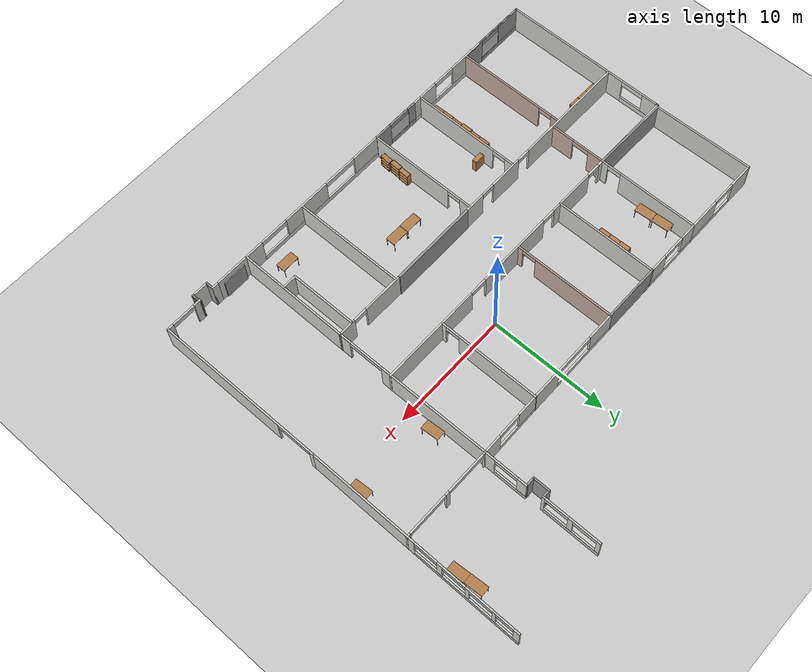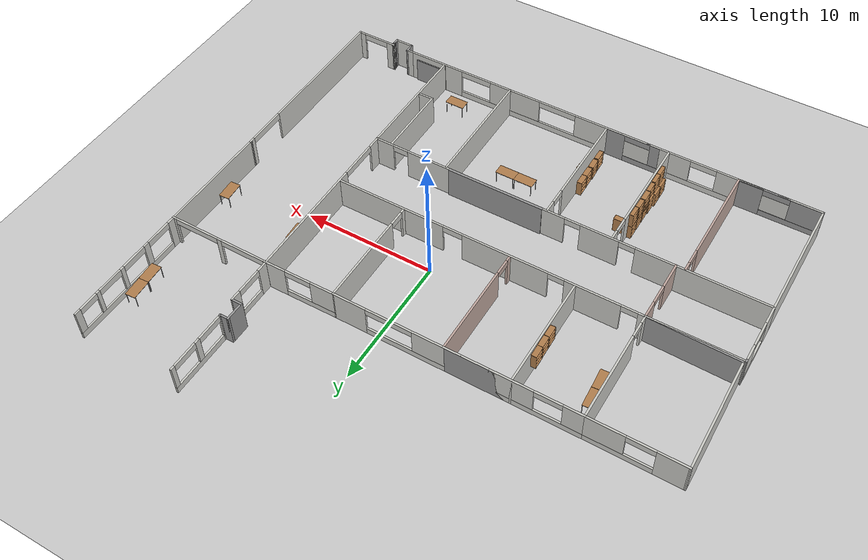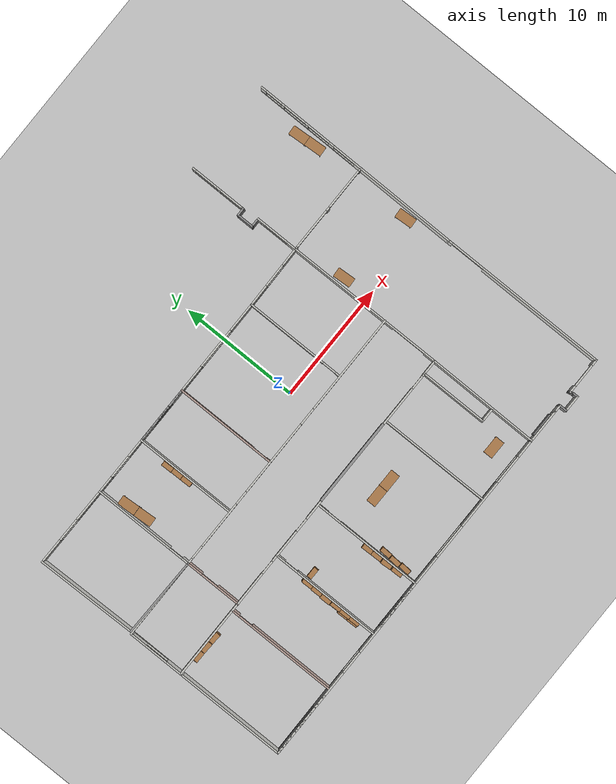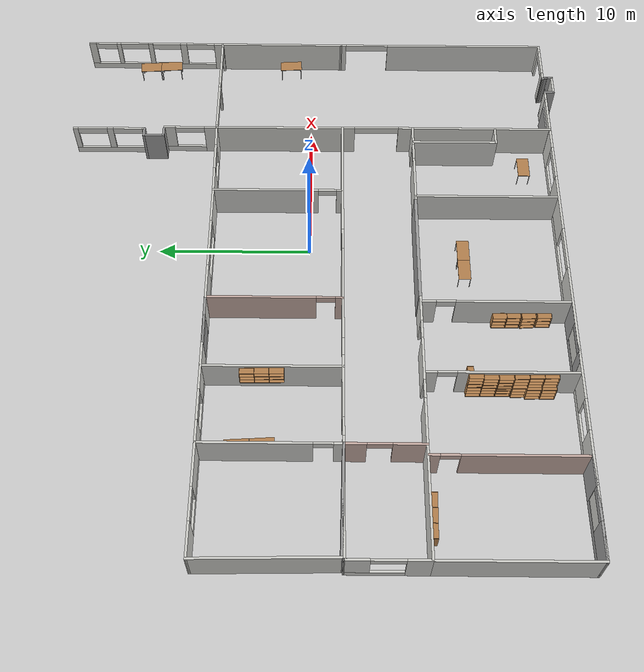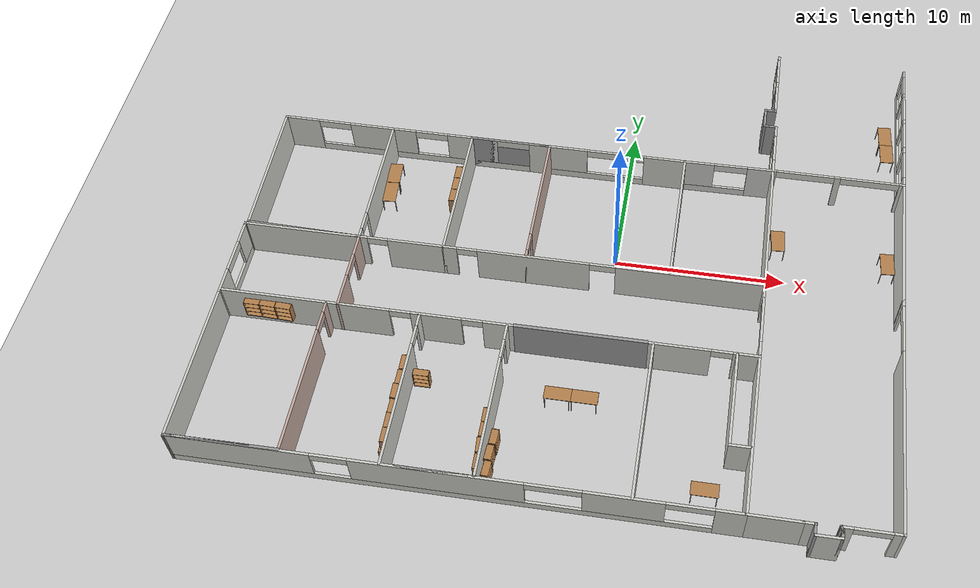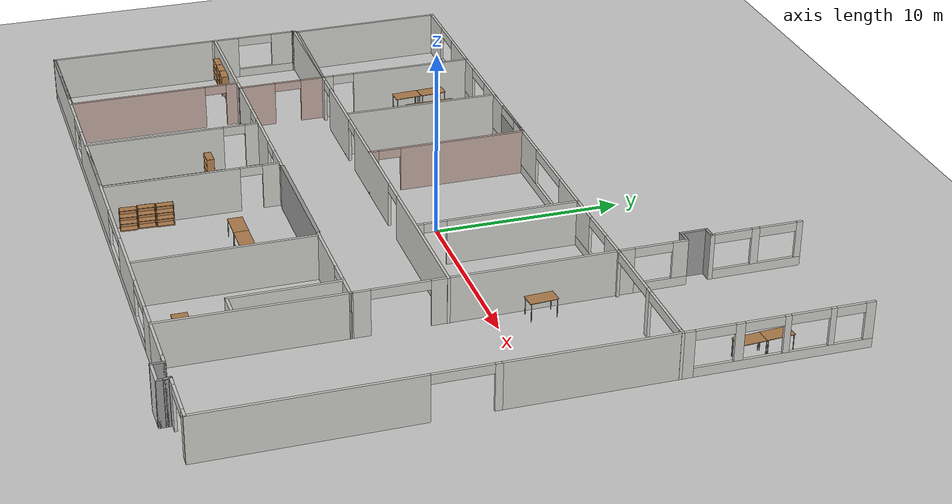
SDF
<sdf version="1.7">
 <world name="default">
  <light name="sun" type="directional">
   <pose>0 0 10 0 -0 0</pose>
   <diffuse>0.8 0.8 0.8 1</diffuse>
   <specular>0.2 0.2 0.2 1</specular>
   <attenuation>
    <range>1000</range>
    <constant>0.9</constant>
    <linear>0.01</linear>
    <quadratic>0.001</quadratic>
   </attenuation>
   <direction>-0.5 0.1 -0.9</direction>
   <spot><inner_angle>0</inner_angle><outer_angle>0</outer_angle><falloff>0</falloff></spot>
  </light>
  <model name="ground_plane">
   <static>1</static>
   <link name="link">
    <collision name="collision">
     <geometry><plane><normal>0 0 1</normal><size>100 100</size></plane></geometry>
     <surface><friction><ode><mu>100</mu><mu2>50</mu2></ode></friction></surface>
    </collision>
    <visual name="visual">
     <cast_shadows>0</cast_shadows>
     <geometry><plane><normal>0 0 1</normal><size>100 100</size></plane></geometry>
     <material>
      <script><uri>file://media/materials/scripts/gazebo.material</uri><name>Gazebo/Grey</name></script>
     </material>
    </visual>
   </link>
  </model>
  <gravity>0 0 -9.8</gravity>
  <magnetic_field>6e-06 2.3e-05 -4.2e-05</magnetic_field>
  <atmosphere type="adiabatic"/>
  <physics type="ode">
   <max_step_size>0.001</max_step_size>
   <real_time_factor>1</real_time_factor>
   <real_time_update_rate>1000</real_time_update_rate>
  </physics>
  <scene><ambient>0.4 0.4 0.4 1</ambient><background>0.7 0.7 0.7 1</background><shadows>1</shadows></scene>
  <spherical_coordinates>
   <surface_model>EARTH_WGS84</surface_model>
   <latitude_deg>0</latitude_deg>
   <longitude_deg>0</longitude_deg>
   <elevation>0</elevation>
   <heading_deg>0</heading_deg>
  </spherical_coordinates>
  <model name="cps_lab_layout">
   <pose>-2.5615 -0.338224 0 0 -0 0</pose>
   <link name="Door_24">
    <collision name="Door_24_Collision">
     <geometry><box><size>2 0.17 2</size></box></geometry>
     <pose>0 0 1 0 -0 0</pose>
    </collision>
    <visual name="Door_24_Visual">
     <pose>0 0 1 0 -0 0</pose>
     <geometry><box><size>2 0.17 2</size></box></geometry>
     <material>
      <script><uri>file://media/materials/scripts/gazebo.material</uri><name>Gazebo/Grey</name></script>
     </material>
    </visual>
    <pose>12.706 -16.0168 0 0 -0 0</pose>
   </link>
   <link name="Wall_100">
    <pose>-12.2949 2.50022 0 0 -0 -1.5708</pose>
    <visual name="Wall_100_Visual_0">
     <pose>-0.931567 0 1.25 0 -0 0</pose>
     <geometry><box><size>6.88687 0.15 2.5</size></box></geometry>
     <material>
      <script><uri>file://media/materials/scripts/gazebo.material</uri><name>Gazebo/CeilingTiled</name></script>
      <ambient>0.760784 0.662745 0.627451 1</ambient>
     </material>
     <meta><layer>0</layer></meta>
    </visual>
    <collision name="Wall_100_Collision_0">
     <geometry><box><size>6.88687 0.15 2.5</size></box></geometry>
     <pose>-0.931567 0 1.25 0 -0 0</pose>
    </collision>
    <visual name="Wall_100_Visual_1">
     <pose>4.04343 0 1.25 0 -0 0</pose>
     <geometry><box><size>0.663135 0.15 2.5</size></box></geometry>
     <material>
      <script><uri>file://media/materials/scripts/gazebo.material</uri><name>Gazebo/CeilingTiled</name></script>
      <ambient>0.760784 0.662745 0.627451 1</ambient>
     </material>
     <meta><layer>0</layer></meta>
    </visual>
    <collision name="Wall_100_Collision_1">
     <geometry><box><size>0.663135 0.15 2.5</size></box></geometry>
     <pose>4.04343 0 1.25 0 -0 0</pose>
    </collision>
    <visual name="Wall_100_Visual_2">
     <pose>3.11186 0 2.25 0 -0 0</pose>
     <geometry><box><size>1.2 0.15 0.5</size></box></geometry>
     <material>
      <script><uri>file://media/materials/scripts/gazebo.material</uri><name>Gazebo/CeilingTiled</name></script>
      <ambient>0.760784 0.662745 0.627451 1</ambient>
     </material>
     <meta><layer>0</layer></meta>
    </visual>
    <collision name="Wall_100_Collision_2">
     <geometry><box><size>1.2 0.15 0.5</size></box></geometry>
     <pose>3.11186 0 2.25 0 -0 0</pose>
    </collision>
   </link>
   <link name="Wall_101">
    <collision name="Wall_101_Collision">
     <geometry><box><size>6.85618 0.15 2.5</size></box></geometry>
     <pose>0 0 1.25 0 -0 0</pose>
    </collision>
    <visual name="Wall_101_Visual">
     <pose>0 0 1.25 0 -0 0</pose>
     <geometry><box><size>6.85618 0.15 2.5</size></box></geometry>
     <material>
      <script><uri>file://media/materials/scripts/gazebo.material</uri><name>Gazebo/Grey</name></script>
      <ambient>1 1 1 1</ambient>
     </material>
     <meta><layer>0</layer></meta>
    </visual>
    <pose>-15.6474 -1.7341 0 0 -0 3.122</pose>
   </link>
   <link name="Wall_102">
    <collision name="Wall_102_Collision">
     <geometry><box><size>8.6581 0.15 2.5</size></box></geometry>
     <pose>0 0 1.25 0 -0 0</pose>
    </collision>
    <visual name="Wall_102_Visual">
     <pose>0 0 1.25 0 -0 0</pose>
     <geometry><box><size>8.6581 0.15 2.5</size></box></geometry>
     <material>
      <script><uri>file://media/materials/scripts/gazebo.material</uri><name>Gazebo/CeilingTiled</name></script>
      <ambient>0.760784 0.662745 0.627451 1</ambient>
     </material>
     <meta><layer>0</layer></meta>
    </visual>
    <pose>-19.0696 2.58506 0 0 -0 1.5872</pose>
   </link>
   <link name="Wall_103">
    <pose>-15.7172 6.81938 0 0 -0 -0.005598</pose>
    <visual name="Wall_103_Visual_0">
     <pose>-2.39687 0 1.25 0 -0 0</pose>
     <geometry><box><size>2.20111 0.15 2.5</size></box></geometry>
     <material>
      <script><uri>file://media/materials/scripts/gazebo.material</uri><name>Gazebo/CeilingTiled</name></script>
      <ambient>1 1 1 1</ambient>
     </material>
     <meta><layer>0</layer></meta>
    </visual>
    <collision name="Wall_103_Collision_0">
     <geometry><box><size>2.20111 0.15 2.5</size></box></geometry>
     <pose>-2.39687 0 1.25 0 -0 0</pose>
    </collision>
    <visual name="Wall_103_Visual_1">
     <pose>1.10056 0 0.25 0 -0 0</pose>
     <geometry><box><size>4.79374 0.15 0.5</size></box></geometry>
     <material>
      <script><uri>file://media/materials/scripts/gazebo.material</uri><name>Gazebo/CeilingTiled</name></script>
      <ambient>1 1 1 1</ambient>
     </material>
     <meta><layer>0</layer></meta>
    </visual>
    <collision name="Wall_103_Collision_1">
     <geometry><box><size>4.79374 0.15 0.5</size></box></geometry>
     <pose>1.10056 0 0.25 0 -0 0</pose>
    </collision>
    <visual name="Wall_103_Visual_2">
     <pose>2.10056 0 1.5 0 -0 0</pose>
     <geometry><box><size>2.79374 0.15 2</size></box></geometry>
     <material>
      <script><uri>file://media/materials/scripts/gazebo.material</uri><name>Gazebo/CeilingTiled</name></script>
      <ambient>1 1 1 1</ambient>
     </material>
     <meta><layer>0</layer></meta>
    </visual>
    <collision name="Wall_103_Collision_2">
     <geometry><box><size>2.79374 0.15 2</size></box></geometry>
     <pose>2.10056 0 1.5 0 -0 0</pose>
    </collision>
    <visual name="Wall_103_Visual_3">
     <pose>-0.296315 0 2.25 0 -0 0</pose>
     <geometry><box><size>2 0.15 0.5</size></box></geometry>
     <material>
      <script><uri>file://media/materials/scripts/gazebo.material</uri><name>Gazebo/CeilingTiled</name></script>
      <ambient>1 1 1 1</ambient>
     </material>
     <meta><layer>0</layer></meta>
    </visual>
    <collision name="Wall_103_Collision_3">
     <geometry><box><size>2 0.15 0.5</size></box></geometry>
     <pose>-0.296315 0 2.25 0 -0 0</pose>
    </collision>
   </link>
   <link name="Wall_104">
    <pose>-12.2949 -4.22478 0 0 -0 -1.5708</pose>
    <visual name="Wall_104_Visual_0">
     <pose>-1.79575 0 1.25 0 -0 0</pose>
     <geometry><box><size>1.40849 0.15 2.5</size></box></geometry>
     <material>
      <script><uri>file://media/materials/scripts/gazebo.material</uri><name>Gazebo/Grey</name></script>
      <ambient>0.760784 0.662745 0.627451 1</ambient>
     </material>
     <meta><layer>0</layer></meta>
    </visual>
    <collision name="Wall_104_Collision_0">
     <geometry><box><size>1.40849 0.15 2.5</size></box></geometry>
     <pose>-1.79575 0 1.25 0 -0 0</pose>
    </collision>
    <visual name="Wall_104_Visual_1">
     <pose>1.45425 0 1.25 0 -0 0</pose>
     <geometry><box><size>2.09151 0.15 2.5</size></box></geometry>
     <material>
      <script><uri>file://media/materials/scripts/gazebo.material</uri><name>Gazebo/Grey</name></script>
      <ambient>0.760784 0.662745 0.627451 1</ambient>
     </material>
     <meta><layer>0</layer></meta>
    </visual>
    <collision name="Wall_104_Collision_1">
     <geometry><box><size>2.09151 0.15 2.5</size></box></geometry>
     <pose>1.45425 0 1.25 0 -0 0</pose>
    </collision>
    <visual name="Wall_104_Visual_2">
     <pose>-0.34151 0 2.25 0 -0 0</pose>
     <geometry><box><size>1.5 0.15 0.5</size></box></geometry>
     <material>
      <script><uri>file://media/materials/scripts/gazebo.material</uri><name>Gazebo/Grey</name></script>
      <ambient>0.760784 0.662745 0.627451 1</ambient>
     </material>
     <meta><layer>0</layer></meta>
    </visual>
    <collision name="Wall_104_Collision_2">
     <geometry><box><size>1.5 0.15 0.5</size></box></geometry>
     <pose>-0.34151 0 2.25 0 -0 0</pose>
    </collision>
   </link>
   <link name="Wall_106">
    <pose>-19.1333 -4.32604 0 0 -0 1.5708</pose>
    <visual name="Wall_106_Visual_0">
     <pose>-1.70451 0 1.25 0 -0 0</pose>
     <geometry><box><size>1.59098 0.15 2.5</size></box></geometry>
     <material>
      <script><uri>file://media/materials/scripts/gazebo.material</uri><name>Gazebo/CeilingTiled</name></script>
      <ambient>0.760784 0.662745 0.627451 1</ambient>
     </material>
     <meta><layer>0</layer></meta>
    </visual>
    <collision name="Wall_106_Collision_0">
     <geometry><box><size>1.59098 0.15 2.5</size></box></geometry>
     <pose>-1.70451 0 1.25 0 -0 0</pose>
    </collision>
    <visual name="Wall_106_Visual_1">
     <pose>0.795491 0 0.25 0 -0 0</pose>
     <geometry><box><size>3.40902 0.15 0.5</size></box></geometry>
     <material>
      <script><uri>file://media/materials/scripts/gazebo.material</uri><name>Gazebo/CeilingTiled</name></script>
      <ambient>0.760784 0.662745 0.627451 1</ambient>
     </material>
     <meta><layer>0</layer></meta>
    </visual>
    <collision name="Wall_106_Collision_1">
     <geometry><box><size>3.40902 0.15 0.5</size></box></geometry>
     <pose>0.795491 0 0.25 0 -0 0</pose>
    </collision>
    <visual name="Wall_106_Visual_2">
     <pose>1.79549 0 1.5 0 -0 0</pose>
     <geometry><box><size>1.40902 0.15 2</size></box></geometry>
     <material>
      <script><uri>file://media/materials/scripts/gazebo.material</uri><name>Gazebo/CeilingTiled</name></script>
      <ambient>0.760784 0.662745 0.627451 1</ambient>
     </material>
     <meta><layer>0</layer></meta>
    </visual>
    <collision name="Wall_106_Collision_2">
     <geometry><box><size>1.40902 0.15 2</size></box></geometry>
     <pose>1.79549 0 1.5 0 -0 0</pose>
    </collision>
    <visual name="Wall_106_Visual_3">
     <pose>0.090982 0 2.25 0 -0 0</pose>
     <geometry><box><size>2 0.15 0.5</size></box></geometry>
     <material>
      <script><uri>file://media/materials/scripts/gazebo.material</uri><name>Gazebo/CeilingTiled</name></script>
      <ambient>0.760784 0.662745 0.627451 1</ambient>
     </material>
     <meta><layer>0</layer></meta>
    </visual>
    <collision name="Wall_106_Collision_3">
     <geometry><box><size>2 0.15 0.5</size></box></geometry>
     <pose>0.090982 0 2.25 0 -0 0</pose>
    </collision>
   </link>
   <link name="Wall_107">
    <collision name="Wall_107_Collision">
     <geometry><box><size>0.15 0.15 2.5</size></box></geometry>
     <pose>0 0 1.25 0 -0 0</pose>
    </collision>
    <visual name="Wall_107_Visual">
     <pose>0 0 1.25 0 -0 0</pose>
     <geometry><box><size>0.15 0.15 2.5</size></box></geometry>
     <material>
      <script><uri>file://media/materials/scripts/gazebo.material</uri><name>Gazebo/Grey</name></script>
      <ambient>1 1 1 1</ambient>
     </material>
     <meta><layer>0</layer></meta>
    </visual>
    <pose>-19.1333 -1.90104 0 0 -0 0</pose>
   </link>
   <link name="Wall_108">
    <collision name="Wall_108_Collision">
     <geometry><box><size>0.15 0.15 2.5</size></box></geometry>
     <pose>0 0 1.25 0 -0 0</pose>
    </collision>
    <visual name="Wall_108_Visual">
     <pose>0 0 1.25 0 -0 0</pose>
     <geometry><box><size>0.15 0.15 2.5</size></box></geometry>
     <material>
      <script><uri>file://media/materials/scripts/gazebo.material</uri><name>Gazebo/Grey</name></script>
      <ambient>1 1 1 1</ambient>
     </material>
     <meta><layer>0</layer></meta>
    </visual>
    <pose>-19.1333 -1.90104 0 0 -0 0</pose>
   </link>
   <link name="Wall_109">
    <collision name="Wall_109_Collision">
     <geometry><box><size>0.25 0.15 2.5</size></box></geometry>
     <pose>0 0 1.25 0 -0 0</pose>
    </collision>
    <visual name="Wall_109_Visual">
     <pose>0 0 1.25 0 -0 0</pose>
     <geometry><box><size>0.25 0.15 2.5</size></box></geometry>
     <material>
      <script><uri>file://media/materials/scripts/gazebo.material</uri><name>Gazebo/Grey</name></script>
      <ambient>1 1 1 1</ambient>
     </material>
     <meta><layer>0</layer></meta>
    </visual>
    <pose>-19.1333 -1.85104 0 0 -0 1.5708</pose>
   </link>
   <link name="Wall_110">
    <collision name="Wall_110_Collision">
     <geometry><box><size>6.98839 0.15 2.5</size></box></geometry>
     <pose>0 0 1.25 0 -0 0</pose>
    </collision>
    <visual name="Wall_110_Visual">
     <pose>0 0 1.25 0 -0 0</pose>
     <geometry><box><size>6.98839 0.15 2.5</size></box></geometry>
     <material>
      <script><uri>file://media/materials/scripts/gazebo.material</uri><name>Gazebo/CeilingTiled</name></script>
      <ambient>0.760784 0.662745 0.627451 1</ambient>
     </material>
     <meta><layer>0</layer></meta>
    </visual>
    <pose>-15.7141 -1.80041 0 0 -0 0.000184</pose>
   </link>
   <link name="Wall_182">
    <collision name="Wall_182_Collision">
     <geometry><box><size>5.75 0.15 2.5</size></box></geometry>
     <pose>0 0 1.25 0 -0 0</pose>
    </collision>
    <visual name="Wall_182_Visual">
     <pose>0 0 1.25 0 -0 0</pose>
     <geometry><box><size>5.75 0.15 2.5</size></box></geometry>
     <material>
      <script><uri>file://media/materials/scripts/gazebo.material</uri><name>Gazebo/CeilingTiled</name></script>
      <ambient>0.760784 0.662745 0.627451 1</ambient>
     </material>
     <meta><layer>0</layer></meta>
    </visual>
    <pose>10.0887 -9.49757 0 0 -0 -1.5708</pose>
   </link>
   <link name="Wall_183">
    <collision name="Wall_183_Collision">
     <geometry><box><size>1.25 0.15 2.5</size></box></geometry>
     <pose>0 0 1.25 0 -0 0</pose>
    </collision>
    <visual name="Wall_183_Visual">
     <pose>0 0 1.25 0 -0 0</pose>
     <geometry><box><size>1.25 0.15 2.5</size></box></geometry>
     <material>
      <script><uri>file://media/materials/scripts/gazebo.material</uri><name>Gazebo/CeilingTiled</name></script>
      <ambient>1 1 1 1</ambient>
     </material>
     <meta><layer>0</layer></meta>
    </visual>
    <pose>10.6387 -12.2976 0 0 -0 0</pose>
   </link>
   <link name="Wall_187">
    <pose>11.2551 8.67058 0 0 -0 1.5708</pose>
    <visual name="Wall_187_Visual_0">
     <pose>-1.40582 0 1.25 0 -0 0</pose>
     <geometry><box><size>0.938352 0.15 2.5</size></box></geometry>
     <material>
      <script><uri>file://media/materials/scripts/gazebo.material</uri><name>Gazebo/CeilingTiled</name></script>
      <ambient>0.760784 0.662745 0.627451 1</ambient>
     </material>
     <meta><layer>0</layer></meta>
    </visual>
    <collision name="Wall_187_Collision_0">
     <geometry><box><size>0.938352 0.15 2.5</size></box></geometry>
     <pose>-1.40582 0 1.25 0 -0 0</pose>
    </collision>
    <visual name="Wall_187_Visual_1">
     <pose>0.469176 0 0.25 0 -0 0</pose>
     <geometry><box><size>2.81165 0.15 0.5</size></box></geometry>
     <material>
      <script><uri>file://media/materials/scripts/gazebo.material</uri><name>Gazebo/CeilingTiled</name></script>
      <ambient>0.760784 0.662745 0.627451 1</ambient>
     </material>
     <meta><layer>0</layer></meta>
    </visual>
    <collision name="Wall_187_Collision_1">
     <geometry><box><size>2.81165 0.15 0.5</size></box></geometry>
     <pose>0.469176 0 0.25 0 -0 0</pose>
    </collision>
    <visual name="Wall_187_Visual_2">
     <pose>1.46918 0 1.5 0 -0 0</pose>
     <geometry><box><size>0.811648 0.15 2</size></box></geometry>
     <material>
      <script><uri>file://media/materials/scripts/gazebo.material</uri><name>Gazebo/CeilingTiled</name></script>
      <ambient>0.760784 0.662745 0.627451 1</ambient>
     </material>
     <meta><layer>0</layer></meta>
    </visual>
    <collision name="Wall_187_Collision_2">
     <geometry><box><size>0.811648 0.15 2</size></box></geometry>
     <pose>1.46918 0 1.5 0 -0 0</pose>
    </collision>
    <visual name="Wall_187_Visual_3">
     <pose>0.063352 0 2.25 0 -0 0</pose>
     <geometry><box><size>2 0.15 0.5</size></box></geometry>
     <material>
      <script><uri>file://media/materials/scripts/gazebo.material</uri><name>Gazebo/CeilingTiled</name></script>
      <ambient>0.760784 0.662745 0.627451 1</ambient>
     </material>
     <meta><layer>0</layer></meta>
    </visual>
    <collision name="Wall_187_Collision_3">
     <geometry><box><size>2 0.15 0.5</size></box></geometry>
     <pose>0.063352 0 2.25 0 -0 0</pose>
    </collision>
   </link>
   <link name="Wall_189">
    <pose>19.097 7.40162 0 0 -0 1.56605</pose>
    <visual name="Wall_189_Visual_0">
     <pose>-4.54614 0 1.25 0 -0 0</pose>
     <geometry><box><size>9.29104 0.15 2.5</size></box></geometry>
     <material>
      <script><uri>file://media/materials/scripts/gazebo.material</uri><name>Gazebo/CeilingTiled</name></script>
      <ambient>0.760784 0.662745 0.627451 1</ambient>
     </material>
     <meta><layer>0</layer></meta>
    </visual>
    <collision name="Wall_189_Collision_0">
     <geometry><box><size>9.29104 0.15 2.5</size></box></geometry>
     <pose>-4.54614 0 1.25 0 -0 0</pose>
    </collision>
    <visual name="Wall_189_Visual_1">
     <pose>4.64552 0 0.25 0 -0 0</pose>
     <geometry><box><size>9.09228 0.15 0.5</size></box></geometry>
     <material>
      <script><uri>file://media/materials/scripts/gazebo.material</uri><name>Gazebo/CeilingTiled</name></script>
      <ambient>0.760784 0.662745 0.627451 1</ambient>
     </material>
     <meta><layer>0</layer></meta>
    </visual>
    <collision name="Wall_189_Collision_1">
     <geometry><box><size>9.09228 0.15 0.5</size></box></geometry>
     <pose>4.64552 0 0.25 0 -0 0</pose>
    </collision>
    <visual name="Wall_189_Visual_2">
     <pose>2.33247 0 1.5 0 -0 0</pose>
     <geometry><box><size>0.466181 0.15 2</size></box></geometry>
     <material>
      <script><uri>file://media/materials/scripts/gazebo.material</uri><name>Gazebo/CeilingTiled</name></script>
      <ambient>0.760784 0.662745 0.627451 1</ambient>
     </material>
     <meta><layer>0</layer></meta>
    </visual>
    <collision name="Wall_189_Collision_2">
     <geometry><box><size>0.466181 0.15 2</size></box></geometry>
     <pose>2.33247 0 1.5 0 -0 0</pose>
    </collision>
    <visual name="Wall_189_Visual_3">
     <pose>4.72865 0 1.5 0 -0 0</pose>
     <geometry><box><size>0.32617 0.15 2</size></box></geometry>
     <material>
      <script><uri>file://media/materials/scripts/gazebo.material</uri><name>Gazebo/CeilingTiled</name></script>
      <ambient>0.760784 0.662745 0.627451 1</ambient>
     </material>
     <meta><layer>0</layer></meta>
    </visual>
    <collision name="Wall_189_Collision_3">
     <geometry><box><size>0.32617 0.15 2</size></box></geometry>
     <pose>4.72865 0 1.5 0 -0 0</pose>
    </collision>
    <visual name="Wall_189_Visual_4">
     <pose>7.04047 0 1.5 0 -0 0</pose>
     <geometry><box><size>0.29747 0.15 2</size></box></geometry>
     <material>
      <script><uri>file://media/materials/scripts/gazebo.material</uri><name>Gazebo/CeilingTiled</name></script>
      <ambient>0.760784 0.662745 0.627451 1</ambient>
     </material>
     <meta><layer>0</layer></meta>
    </visual>
    <collision name="Wall_189_Collision_4">
     <geometry><box><size>0.29747 0.15 2</size></box></geometry>
     <pose>7.04047 0 1.5 0 -0 0</pose>
    </collision>
    <visual name="Wall_189_Visual_5">
     <pose>8.94043 0 1.5 0 -0 0</pose>
     <geometry><box><size>0.502461 0.15 2</size></box></geometry>
     <material>
      <script><uri>file://media/materials/scripts/gazebo.material</uri><name>Gazebo/CeilingTiled</name></script>
      <ambient>0.760784 0.662745 0.627451 1</ambient>
     </material>
     <meta><layer>0</layer></meta>
    </visual>
    <collision name="Wall_189_Collision_5">
     <geometry><box><size>0.502461 0.15 2</size></box></geometry>
     <pose>8.94043 0 1.5 0 -0 0</pose>
    </collision>
    <visual name="Wall_189_Visual_6">
     <pose>1.09938 0 2.25 0 -0 0</pose>
     <geometry><box><size>2 0.15 0.5</size></box></geometry>
     <material>
      <script><uri>file://media/materials/scripts/gazebo.material</uri><name>Gazebo/CeilingTiled</name></script>
      <ambient>0.760784 0.662745 0.627451 1</ambient>
     </material>
     <meta><layer>0</layer></meta>
    </visual>
    <collision name="Wall_189_Collision_6">
     <geometry><box><size>2 0.15 0.5</size></box></geometry>
     <pose>1.09938 0 2.25 0 -0 0</pose>
    </collision>
    <visual name="Wall_189_Visual_7">
     <pose>3.56556 0 2.25 0 -0 0</pose>
     <geometry><box><size>2 0.15 0.5</size></box></geometry>
     <material>
      <script><uri>file://media/materials/scripts/gazebo.material</uri><name>Gazebo/CeilingTiled</name></script>
      <ambient>0.760784 0.662745 0.627451 1</ambient>
     </material>
     <meta><layer>0</layer></meta>
    </visual>
    <collision name="Wall_189_Collision_7">
     <geometry><box><size>2 0.15 0.5</size></box></geometry>
     <pose>3.56556 0 2.25 0 -0 0</pose>
    </collision>
    <visual name="Wall_189_Visual_8">
     <pose>5.89173 0 2.25 0 -0 0</pose>
     <geometry><box><size>2 0.15 0.5</size></box></geometry>
     <material>
      <script><uri>file://media/materials/scripts/gazebo.material</uri><name>Gazebo/CeilingTiled</name></script>
      <ambient>0.760784 0.662745 0.627451 1</ambient>
     </material>
     <meta><layer>0</layer></meta>
    </visual>
    <collision name="Wall_189_Collision_8">
     <geometry><box><size>2 0.15 0.5</size></box></geometry>
     <pose>5.89173 0 2.25 0 -0 0</pose>
    </collision>
    <visual name="Wall_189_Visual_9">
     <pose>7.9392 0 2.25 0 -0 0</pose>
     <geometry><box><size>1.5 0.15 0.5</size></box></geometry>
     <material>
      <script><uri>file://media/materials/scripts/gazebo.material</uri><name>Gazebo/CeilingTiled</name></script>
      <ambient>0.760784 0.662745 0.627451 1</ambient>
     </material>
     <meta><layer>0</layer></meta>
    </visual>
    <collision name="Wall_189_Collision_9">
     <geometry><box><size>1.5 0.15 0.5</size></box></geometry>
     <pose>7.9392 0 2.25 0 -0 0</pose>
    </collision>
   </link>
   <link name="Wall_191">
    <pose>-0.494925 -1.79978 0 0 -0 0</pose>
    <visual name="Wall_191_Visual_0">
     <pose>-11.5937 0 1.25 0 -0 0</pose>
     <geometry><box><size>0.562682 0.15 2.5</size></box></geometry>
     <material>
      <script><uri>file://media/materials/scripts/gazebo.material</uri><name>Gazebo/CeilingTiled</name></script>
      <ambient>0.760784 0.662745 0.627451 1</ambient>
     </material>
     <meta><layer>0</layer></meta>
    </visual>
    <collision name="Wall_191_Collision_0">
     <geometry><box><size>0.562682 0.15 2.5</size></box></geometry>
     <pose>-11.5937 0 1.25 0 -0 0</pose>
    </collision>
    <visual name="Wall_191_Visual_1">
     <pose>-8.06045 0 1.25 0 -0 0</pose>
     <geometry><box><size>4.10373 0.15 2.5</size></box></geometry>
     <material>
      <script><uri>file://media/materials/scripts/gazebo.material</uri><name>Gazebo/CeilingTiled</name></script>
      <ambient>0.760784 0.662745 0.627451 1</ambient>
     </material>
     <meta><layer>0</layer></meta>
    </visual>
    <collision name="Wall_191_Collision_1">
     <geometry><box><size>4.10373 0.15 2.5</size></box></geometry>
     <pose>-8.06045 0 1.25 0 -0 0</pose>
    </collision>
    <visual name="Wall_191_Visual_2">
     <pose>-1.52906 0 1.25 0 -0 0</pose>
     <geometry><box><size>6.55907 0.15 2.5</size></box></geometry>
     <material>
      <script><uri>file://media/materials/scripts/gazebo.material</uri><name>Gazebo/CeilingTiled</name></script>
      <ambient>0.760784 0.662745 0.627451 1</ambient>
     </material>
     <meta><layer>0</layer></meta>
    </visual>
    <collision name="Wall_191_Collision_2">
     <geometry><box><size>6.55907 0.15 2.5</size></box></geometry>
     <pose>-1.52906 0 1.25 0 -0 0</pose>
    </collision>
    <visual name="Wall_191_Visual_3">
     <pose>7.56274 0 1.25 0 -0 0</pose>
     <geometry><box><size>8.62453 0.15 2.5</size></box></geometry>
     <material>
      <script><uri>file://media/materials/scripts/gazebo.material</uri><name>Gazebo/CeilingTiled</name></script>
      <ambient>0.760784 0.662745 0.627451 1</ambient>
     </material>
     <meta><layer>0</layer></meta>
    </visual>
    <collision name="Wall_191_Collision_3">
     <geometry><box><size>8.62453 0.15 2.5</size></box></geometry>
     <pose>7.56274 0 1.25 0 -0 0</pose>
    </collision>
    <visual name="Wall_191_Visual_4">
     <pose>-10.7123 0 2.25 0 -0 0</pose>
     <geometry><box><size>1.2 0.15 0.5</size></box></geometry>
     <material>
      <script><uri>file://media/materials/scripts/gazebo.material</uri><name>Gazebo/CeilingTiled</name></script>
      <ambient>0.760784 0.662745 0.627451 1</ambient>
     </material>
     <meta><layer>0</layer></meta>
    </visual>
    <collision name="Wall_191_Collision_4">
     <geometry><box><size>1.2 0.15 0.5</size></box></geometry>
     <pose>-10.7123 0 2.25 0 -0 0</pose>
    </collision>
    <visual name="Wall_191_Visual_5">
     <pose>-5.40859 0 2.25 0 -0 0</pose>
     <geometry><box><size>1.2 0.15 0.5</size></box></geometry>
     <material>
      <script><uri>file://media/materials/scripts/gazebo.material</uri><name>Gazebo/CeilingTiled</name></script>
      <ambient>0.760784 0.662745 0.627451 1</ambient>
     </material>
     <meta><layer>0</layer></meta>
    </visual>
    <collision name="Wall_191_Collision_5">
     <geometry><box><size>1.2 0.15 0.5</size></box></geometry>
     <pose>-5.40859 0 2.25 0 -0 0</pose>
    </collision>
    <visual name="Wall_191_Visual_6">
     <pose>2.50047 0 2.25 0 -0 0</pose>
     <geometry><box><size>1.5 0.15 0.5</size></box></geometry>
     <material>
      <script><uri>file://media/materials/scripts/gazebo.material</uri><name>Gazebo/CeilingTiled</name></script>
      <ambient>0.760784 0.662745 0.627451 1</ambient>
     </material>
     <meta><layer>0</layer></meta>
    </visual>
    <collision name="Wall_191_Collision_6">
     <geometry><box><size>1.5 0.15 0.5</size></box></geometry>
     <pose>2.50047 0 2.25 0 -0 0</pose>
    </collision>
   </link>
   <link name="Wall_193">
    <pose>15.1801 6.87058 0 0 -0 0</pose>
    <visual name="Wall_193_Visual_0">
     <pose>-3.85613 0 1.25 0 -0 0</pose>
     <geometry><box><size>0.287735 0.15 2.5</size></box></geometry>
     <material>
      <script><uri>file://media/materials/scripts/gazebo.material</uri><name>Gazebo/CeilingTiled</name></script>
      <ambient>0.760784 0.662745 0.627451 1</ambient>
     </material>
     <meta><layer>0</layer></meta>
    </visual>
    <collision name="Wall_193_Collision_0">
     <geometry><box><size>0.287735 0.15 2.5</size></box></geometry>
     <pose>-3.85613 0 1.25 0 -0 0</pose>
    </collision>
    <visual name="Wall_193_Visual_1">
     <pose>-0.031522 0 1.25 0 -0 0</pose>
     <geometry><box><size>0.361485 0.15 2.5</size></box></geometry>
     <material>
      <script><uri>file://media/materials/scripts/gazebo.material</uri><name>Gazebo/CeilingTiled</name></script>
      <ambient>0.760784 0.662745 0.627451 1</ambient>
     </material>
     <meta><layer>0</layer></meta>
    </visual>
    <collision name="Wall_193_Collision_1">
     <geometry><box><size>0.361485 0.15 2.5</size></box></geometry>
     <pose>-0.031522 0 1.25 0 -0 0</pose>
    </collision>
    <visual name="Wall_193_Visual_2">
     <pose>3.82461 0 1.25 0 -0 0</pose>
     <geometry><box><size>0.35078 0.15 2.5</size></box></geometry>
     <material>
      <script><uri>file://media/materials/scripts/gazebo.material</uri><name>Gazebo/CeilingTiled</name></script>
      <ambient>0.760784 0.662745 0.627451 1</ambient>
     </material>
     <meta><layer>0</layer></meta>
    </visual>
    <collision name="Wall_193_Collision_2">
     <geometry><box><size>0.35078 0.15 2.5</size></box></geometry>
     <pose>3.82461 0 1.25 0 -0 0</pose>
    </collision>
    <visual name="Wall_193_Visual_3">
     <pose>-1.96226 0 2.25 0 -0 0</pose>
     <geometry><box><size>3.5 0.15 0.5</size></box></geometry>
     <material>
      <script><uri>file://media/materials/scripts/gazebo.material</uri><name>Gazebo/CeilingTiled</name></script>
      <ambient>0.760784 0.662745 0.627451 1</ambient>
     </material>
     <meta><layer>0</layer></meta>
    </visual>
    <collision name="Wall_193_Collision_3">
     <geometry><box><size>3.5 0.15 0.5</size></box></geometry>
     <pose>-1.96226 0 2.25 0 -0 0</pose>
    </collision>
    <visual name="Wall_193_Visual_4">
     <pose>1.89922 0 2.25 0 -0 0</pose>
     <geometry><box><size>3.5 0.15 0.5</size></box></geometry>
     <material>
      <script><uri>file://media/materials/scripts/gazebo.material</uri><name>Gazebo/CeilingTiled</name></script>
      <ambient>0.760784 0.662745 0.627451 1</ambient>
     </material>
     <meta><layer>0</layer></meta>
    </visual>
    <collision name="Wall_193_Collision_4">
     <geometry><box><size>3.5 0.15 0.5</size></box></geometry>
     <pose>1.89922 0 2.25 0 -0 0</pose>
    </collision>
   </link>
   <link name="Wall_197">
    <collision name="Wall_197_Collision">
     <geometry><box><size>0.75 0.15 2.5</size></box></geometry>
     <pose>0 0 1.25 0 -0 0</pose>
    </collision>
    <visual name="Wall_197_Visual">
     <pose>0 0 1.25 0 -0 0</pose>
     <geometry><box><size>0.75 0.15 2.5</size></box></geometry>
     <material>
      <script><uri>file://media/materials/scripts/gazebo.material</uri><name>Gazebo/Grey</name></script>
      <ambient>1 1 1 1</ambient>
     </material>
     <meta><layer>0</layer></meta>
    </visual>
    <pose>10.8242 11.851 0 0 -0 3.14159</pose>
   </link>
   <link name="Wall_198">
    <collision name="Wall_198_Collision">
     <geometry><box><size>1.5 0.15 2.5</size></box></geometry>
     <pose>0 0 1.25 0 -0 0</pose>
    </collision>
    <visual name="Wall_198_Visual">
     <pose>0 0 1.25 0 -0 0</pose>
     <geometry><box><size>1.5 0.15 2.5</size></box></geometry>
     <material>
      <script><uri>file://media/materials/scripts/gazebo.material</uri><name>Gazebo/Grey</name></script>
      <ambient>1 1 1 1</ambient>
     </material>
     <meta><layer>0</layer></meta>
    </visual>
    <pose>10.5242 11.176 0 0 -0 -1.5708</pose>
   </link>
   <link name="Wall_199">
    <collision name="Wall_199_Collision">
     <geometry><box><size>0.75 0.15 2.5</size></box></geometry>
     <pose>0 0 1.25 0 -0 0</pose>
    </collision>
    <visual name="Wall_199_Visual">
     <pose>0 0 1.25 0 -0 0</pose>
     <geometry><box><size>0.75 0.15 2.5</size></box></geometry>
     <material>
      <script><uri>file://media/materials/scripts/gazebo.material</uri><name>Gazebo/Grey</name></script>
      <ambient>1 1 1 1</ambient>
     </material>
     <meta><layer>0</layer></meta>
    </visual>
    <pose>10.8242 10.501 0 0 -0 0</pose>
   </link>
   <link name="Wall_201">
    <pose>11.1242 14.276 0 0 -0 1.5708</pose>
    <visual name="Wall_201_Visual_0">
     <pose>-2.38095 0 1.25 0 -0 0</pose>
     <geometry><box><size>0.238098 0.15 2.5</size></box></geometry>
     <material>
      <script><uri>file://media/materials/scripts/gazebo.material</uri><name>Gazebo/CeilingTiled</name></script>
      <ambient>0.760784 0.662745 0.627451 1</ambient>
     </material>
     <meta><layer>0</layer></meta>
    </visual>
    <collision name="Wall_201_Collision_0">
     <geometry><box><size>0.238098 0.15 2.5</size></box></geometry>
     <pose>-2.38095 0 1.25 0 -0 0</pose>
    </collision>
    <visual name="Wall_201_Visual_1">
     <pose>0.119049 0 0.25 0 -0 0</pose>
     <geometry><box><size>4.7619 0.15 0.5</size></box></geometry>
     <material>
      <script><uri>file://media/materials/scripts/gazebo.material</uri><name>Gazebo/CeilingTiled</name></script>
      <ambient>0.760784 0.662745 0.627451 1</ambient>
     </material>
     <meta><layer>0</layer></meta>
    </visual>
    <collision name="Wall_201_Collision_1">
     <geometry><box><size>4.7619 0.15 0.5</size></box></geometry>
     <pose>0.119049 0 0.25 0 -0 0</pose>
    </collision>
    <visual name="Wall_201_Visual_2">
     <pose>-0.05228 0 1.5 0 -0 0</pose>
     <geometry><box><size>0.419243 0.15 2</size></box></geometry>
     <material>
      <script><uri>file://media/materials/scripts/gazebo.material</uri><name>Gazebo/CeilingTiled</name></script>
      <ambient>0.760784 0.662745 0.627451 1</ambient>
     </material>
     <meta><layer>0</layer></meta>
    </visual>
    <collision name="Wall_201_Collision_2">
     <geometry><box><size>0.419243 0.15 2</size></box></geometry>
     <pose>-0.05228 0 1.5 0 -0 0</pose>
    </collision>
    <visual name="Wall_201_Visual_3">
     <pose>2.32867 0 1.5 0 -0 0</pose>
     <geometry><box><size>0.342659 0.15 2</size></box></geometry>
     <material>
      <script><uri>file://media/materials/scripts/gazebo.material</uri><name>Gazebo/CeilingTiled</name></script>
      <ambient>0.760784 0.662745 0.627451 1</ambient>
     </material>
     <meta><layer>0</layer></meta>
    </visual>
    <collision name="Wall_201_Collision_3">
     <geometry><box><size>0.342659 0.15 2</size></box></geometry>
     <pose>2.32867 0 1.5 0 -0 0</pose>
    </collision>
    <visual name="Wall_201_Visual_4">
     <pose>-1.2619 0 2.25 0 -0 0</pose>
     <geometry><box><size>2 0.15 0.5</size></box></geometry>
     <material>
      <script><uri>file://media/materials/scripts/gazebo.material</uri><name>Gazebo/CeilingTiled</name></script>
      <ambient>0.760784 0.662745 0.627451 1</ambient>
     </material>
     <meta><layer>0</layer></meta>
    </visual>
    <collision name="Wall_201_Collision_4">
     <geometry><box><size>2 0.15 0.5</size></box></geometry>
     <pose>-1.2619 0 2.25 0 -0 0</pose>
    </collision>
    <visual name="Wall_201_Visual_5">
     <pose>1.15734 0 2.25 0 -0 0</pose>
     <geometry><box><size>2 0.15 0.5</size></box></geometry>
     <material>
      <script><uri>file://media/materials/scripts/gazebo.material</uri><name>Gazebo/CeilingTiled</name></script>
      <ambient>0.760784 0.662745 0.627451 1</ambient>
     </material>
     <meta><layer>0</layer></meta>
    </visual>
    <collision name="Wall_201_Collision_5">
     <geometry><box><size>2 0.15 0.5</size></box></geometry>
     <pose>1.15734 0 2.25 0 -0 0</pose>
    </collision>
   </link>
   <link name="Wall_203">
    <collision name="Wall_203_Collision">
     <geometry><box><size>3 0.15 2.5</size></box></geometry>
     <pose>0 0 1.25 0 -0 0</pose>
    </collision>
    <visual name="Wall_203_Visual">
     <pose>0 0 1.25 0 -0 0</pose>
     <geometry><box><size>3 0.15 2.5</size></box></geometry>
     <material>
      <script><uri>file://media/materials/scripts/gazebo.material</uri><name>Gazebo/CeilingTiled</name></script>
      <ambient>0.760784 0.662745 0.627451 1</ambient>
     </material>
     <meta><layer>0</layer></meta>
    </visual>
    <pose>12.6417 -16.101 0 0 -0 0</pose>
   </link>
   <link name="Wall_210">
    <collision name="Wall_210_Collision">
     <geometry><box><size>0.75 0.15 2.5</size></box></geometry>
     <pose>0 0 1.25 0 -0 0</pose>
    </collision>
    <visual name="Wall_210_Visual">
     <pose>0 0 1.25 0 -0 0</pose>
     <geometry><box><size>0.75 0.15 2.5</size></box></geometry>
     <material>
      <script><uri>file://media/materials/scripts/gazebo.material</uri><name>Gazebo/CeilingTiled</name></script>
      <ambient>0.760784 0.662745 0.627451 1</ambient>
     </material>
     <meta><layer>0</layer></meta>
    </visual>
    <pose>14.3667 -16.101 0 0 -0 0</pose>
   </link>
   <link name="Wall_211">
    <collision name="Wall_211_Collision">
     <geometry><box><size>0.75 0.15 2.5</size></box></geometry>
     <pose>0 0 1.25 0 -0 0</pose>
    </collision>
    <visual name="Wall_211_Visual">
     <pose>0 0 1.25 0 -0 0</pose>
     <geometry><box><size>0.75 0.15 2.5</size></box></geometry>
     <material>
      <script><uri>file://media/materials/scripts/gazebo.material</uri><name>Gazebo/Grey</name></script>
      <ambient>1 1 1 1</ambient>
     </material>
     <meta><layer>0</layer></meta>
    </visual>
    <pose>14.6667 -16.401 0 0 -0 -1.5708</pose>
   </link>
   <link name="Wall_212">
    <collision name="Wall_212_Collision">
     <geometry><box><size>1.5 0.15 2.5</size></box></geometry>
     <pose>0 0 1.25 0 -0 0</pose>
    </collision>
    <visual name="Wall_212_Visual">
     <pose>0 0 1.25 0 -0 0</pose>
     <geometry><box><size>1.5 0.15 2.5</size></box></geometry>
     <material>
      <script><uri>file://media/materials/scripts/gazebo.material</uri><name>Gazebo/CeilingTiled</name></script>
      <ambient>0.760784 0.662745 0.627451 1</ambient>
     </material>
     <meta><layer>0</layer></meta>
    </visual>
    <pose>15.3417 -16.701 0 0 -0 0</pose>
   </link>
   <link name="Wall_213">
    <collision name="Wall_213_Collision">
     <geometry><box><size>0.5 0.15 2.5</size></box></geometry>
     <pose>0 0 1.25 0 -0 0</pose>
    </collision>
    <visual name="Wall_213_Visual">
     <pose>0 0 1.25 0 -0 0</pose>
     <geometry><box><size>0.5 0.15 2.5</size></box></geometry>
     <material>
      <script><uri>file://media/materials/scripts/gazebo.material</uri><name>Gazebo/Grey</name></script>
      <ambient>1 1 1 1</ambient>
     </material>
     <meta><layer>0</layer></meta>
    </visual>
    <pose>16.0167 -16.526 0 0 -0 1.5708</pose>
   </link>
   <link name="Wall_214">
    <collision name="Wall_214_Collision">
     <geometry><box><size>0.25 0.15 2.5</size></box></geometry>
     <pose>0 0 1.25 0 -0 0</pose>
    </collision>
    <visual name="Wall_214_Visual">
     <pose>0 0 1.25 0 -0 0</pose>
     <geometry><box><size>0.25 0.15 2.5</size></box></geometry>
     <material>
      <script><uri>file://media/materials/scripts/gazebo.material</uri><name>Gazebo/Grey</name></script>
      <ambient>1 1 1 1</ambient>
     </material>
     <meta><layer>0</layer></meta>
    </visual>
    <pose>16.0167 -16.301 0 0 -0 1.5708</pose>
   </link>
   <link name="Wall_216">
    <pose>17.5037 -16.0649 0 0 -0 3.14159</pose>
    <visual name="Wall_216_Visual_0">
     <pose>-1.33294 0 1.25 0 -0 0</pose>
     <geometry><box><size>0.584125 0.15 2.5</size></box></geometry>
     <material>
      <script><uri>file://media/materials/scripts/gazebo.material</uri><name>Gazebo/CeilingTiled</name></script>
      <ambient>0.760784 0.662745 0.627451 1</ambient>
     </material>
     <meta><layer>0</layer></meta>
    </visual>
    <collision name="Wall_216_Collision_0">
     <geometry><box><size>0.584125 0.15 2.5</size></box></geometry>
     <pose>-1.33294 0 1.25 0 -0 0</pose>
    </collision>
    <visual name="Wall_216_Visual_1">
     <pose>1.29206 0 1.25 0 -0 0</pose>
     <geometry><box><size>0.665875 0.15 2.5</size></box></geometry>
     <material>
      <script><uri>file://media/materials/scripts/gazebo.material</uri><name>Gazebo/CeilingTiled</name></script>
      <ambient>0.760784 0.662745 0.627451 1</ambient>
     </material>
     <meta><layer>0</layer></meta>
    </visual>
    <collision name="Wall_216_Collision_1">
     <geometry><box><size>0.665875 0.15 2.5</size></box></geometry>
     <pose>1.29206 0 1.25 0 -0 0</pose>
    </collision>
    <visual name="Wall_216_Visual_2">
     <pose>-0.040875 0 2.25 0 -0 0</pose>
     <geometry><box><size>2 0.15 0.5</size></box></geometry>
     <material>
      <script><uri>file://media/materials/scripts/gazebo.material</uri><name>Gazebo/CeilingTiled</name></script>
      <ambient>0.760784 0.662745 0.627451 1</ambient>
     </material>
     <meta><layer>0</layer></meta>
    </visual>
    <collision name="Wall_216_Collision_2">
     <geometry><box><size>2 0.15 0.5</size></box></geometry>
     <pose>-0.040875 0 2.25 0 -0 0</pose>
    </collision>
   </link>
   <link name="Wall_217">
    <collision name="Wall_217_Collision">
     <geometry><box><size>0.442956 0.15 2.5</size></box></geometry>
     <pose>0 0 1.25 0 -0 0</pose>
    </collision>
    <visual name="Wall_217_Visual">
     <pose>0 0 1.25 0 -0 0</pose>
     <geometry><box><size>0.442956 0.15 2.5</size></box></geometry>
     <material>
      <script><uri>file://media/materials/scripts/gazebo.material</uri><name>Gazebo/Grey</name></script>
      <ambient>1 1 1 1</ambient>
     </material>
     <meta><layer>0</layer></meta>
    </visual>
    <pose>15.9852 -16.208 0 0 -0 -1.35395</pose>
   </link>
   <link name="Wall_76">
    <collision name="Wall_76_Collision">
     <geometry><box><size>9.63969 0.15 2.5</size></box></geometry>
     <pose>0 0 1.25 0 -0 0</pose>
    </collision>
    <visual name="Wall_76_Visual">
     <pose>0 0 1.25 0 -0 0</pose>
     <geometry><box><size>9.63969 0.15 2.5</size></box></geometry>
     <material>
      <script><uri>file://media/materials/scripts/gazebo.material</uri><name>Gazebo/CeilingTiled</name></script>
      <ambient>0.760784 0.662745 0.627451 1</ambient>
     </material>
     <meta><layer>0</layer></meta>
    </visual>
    <pose>11.2783 -11.3346 0 0 -0 -1.5757</pose>
   </link>
   <link name="Wall_77">
    <pose>19.0537 -8.88994 0 0 -0 1.5708</pose>
    <visual name="Wall_77_Visual_0">
     <pose>-1.72755 0 1.25 0 -0 0</pose>
     <geometry><box><size>11.0449 0.15 2.5</size></box></geometry>
     <material>
      <script><uri>file://media/materials/scripts/gazebo.material</uri><name>Gazebo/CeilingTiled</name></script>
      <ambient>0.760784 0.662745 0.627451 1</ambient>
     </material>
     <meta><layer>0</layer></meta>
    </visual>
    <collision name="Wall_77_Collision_0">
     <geometry><box><size>11.0449 0.15 2.5</size></box></geometry>
     <pose>-1.72755 0 1.25 0 -0 0</pose>
    </collision>
    <visual name="Wall_77_Visual_1">
     <pose>7.02245 0 1.25 0 -0 0</pose>
     <geometry><box><size>0.455102 0.15 2.5</size></box></geometry>
     <material>
      <script><uri>file://media/materials/scripts/gazebo.material</uri><name>Gazebo/CeilingTiled</name></script>
      <ambient>0.760784 0.662745 0.627451 1</ambient>
     </material>
     <meta><layer>0</layer></meta>
    </visual>
    <collision name="Wall_77_Collision_1">
     <geometry><box><size>0.455102 0.15 2.5</size></box></geometry>
     <pose>7.02245 0 1.25 0 -0 0</pose>
    </collision>
    <visual name="Wall_77_Visual_2">
     <pose>5.2949 0 2.25 0 -0 0</pose>
     <geometry><box><size>3 0.15 0.5</size></box></geometry>
     <material>
      <script><uri>file://media/materials/scripts/gazebo.material</uri><name>Gazebo/CeilingTiled</name></script>
      <ambient>0.760784 0.662745 0.627451 1</ambient>
     </material>
     <meta><layer>0</layer></meta>
    </visual>
    <collision name="Wall_77_Collision_2">
     <geometry><box><size>3 0.15 0.5</size></box></geometry>
     <pose>5.2949 0 2.25 0 -0 0</pose>
    </collision>
   </link>
   <link name="Wall_78">
    <pose>-3.8734 -6.63637 0 0 -0 3.14159</pose>
    <visual name="Wall_78_Visual_0">
     <pose>-14.4896 0 1.25 0 -0 0</pose>
     <geometry><box><size>1.52082 0.15 2.5</size></box></geometry>
     <material>
      <script><uri>file://media/materials/scripts/gazebo.material</uri><name>Gazebo/CeilingTiled</name></script>
      <ambient>0.760784 0.662745 0.627451 1</ambient>
     </material>
     <meta><layer>0</layer></meta>
    </visual>
    <collision name="Wall_78_Collision_0">
     <geometry><box><size>1.52082 0.15 2.5</size></box></geometry>
     <pose>-14.4896 0 1.25 0 -0 0</pose>
    </collision>
    <visual name="Wall_78_Visual_1">
     <pose>-6.18137 0 1.25 0 -0 0</pose>
     <geometry><box><size>12.6956 0.15 2.5</size></box></geometry>
     <material>
      <script><uri>file://media/materials/scripts/gazebo.material</uri><name>Gazebo/CeilingTiled</name></script>
      <ambient>0.760784 0.662745 0.627451 1</ambient>
     </material>
     <meta><layer>0</layer></meta>
    </visual>
    <collision name="Wall_78_Collision_1">
     <geometry><box><size>12.6956 0.15 2.5</size></box></geometry>
     <pose>-6.18137 0 1.25 0 -0 0</pose>
    </collision>
    <visual name="Wall_78_Visual_2">
     <pose>2.81725 0 1.25 0 -0 0</pose>
     <geometry><box><size>2.90164 0.15 2.5</size></box></geometry>
     <material>
      <script><uri>file://media/materials/scripts/gazebo.material</uri><name>Gazebo/CeilingTiled</name></script>
      <ambient>0.760784 0.662745 0.627451 1</ambient>
     </material>
     <meta><layer>0</layer></meta>
    </visual>
    <collision name="Wall_78_Collision_2">
     <geometry><box><size>2.90164 0.15 2.5</size></box></geometry>
     <pose>2.81725 0 1.25 0 -0 0</pose>
    </collision>
    <visual name="Wall_78_Visual_3">
     <pose>10.359 0 1.25 0 -0 0</pose>
     <geometry><box><size>9.78192 0.15 2.5</size></box></geometry>
     <material>
      <script><uri>file://media/materials/scripts/gazebo.material</uri><name>Gazebo/CeilingTiled</name></script>
      <ambient>0.760784 0.662745 0.627451 1</ambient>
     </material>
     <meta><layer>0</layer></meta>
    </visual>
    <collision name="Wall_78_Collision_3">
     <geometry><box><size>9.78192 0.15 2.5</size></box></geometry>
     <pose>10.359 0 1.25 0 -0 0</pose>
    </collision>
    <visual name="Wall_78_Visual_4">
     <pose>-13.1292 0 2.25 0 -0 0</pose>
     <geometry><box><size>1.2 0.15 0.5</size></box></geometry>
     <material>
      <script><uri>file://media/materials/scripts/gazebo.material</uri><name>Gazebo/CeilingTiled</name></script>
      <ambient>0.760784 0.662745 0.627451 1</ambient>
     </material>
     <meta><layer>0</layer></meta>
    </visual>
    <collision name="Wall_78_Collision_4">
     <geometry><box><size>1.2 0.15 0.5</size></box></geometry>
     <pose>-13.1292 0 2.25 0 -0 0</pose>
    </collision>
    <visual name="Wall_78_Visual_5">
     <pose>0.766434 0 2.25 0 -0 0</pose>
     <geometry><box><size>1.2 0.15 0.5</size></box></geometry>
     <material>
      <script><uri>file://media/materials/scripts/gazebo.material</uri><name>Gazebo/CeilingTiled</name></script>
      <ambient>0.760784 0.662745 0.627451 1</ambient>
     </material>
     <meta><layer>0</layer></meta>
    </visual>
    <collision name="Wall_78_Collision_5">
     <geometry><box><size>1.2 0.15 0.5</size></box></geometry>
     <pose>0.766434 0 2.25 0 -0 0</pose>
    </collision>
    <visual name="Wall_78_Visual_6">
     <pose>4.86808 0 2.25 0 -0 0</pose>
     <geometry><box><size>1.2 0.15 0.5</size></box></geometry>
     <material>
      <script><uri>file://media/materials/scripts/gazebo.material</uri><name>Gazebo/CeilingTiled</name></script>
      <ambient>0.760784 0.662745 0.627451 1</ambient>
     </material>
     <meta><layer>0</layer></meta>
    </visual>
    <collision name="Wall_78_Collision_6">
     <geometry><box><size>1.2 0.15 0.5</size></box></geometry>
     <pose>4.86808 0 2.25 0 -0 0</pose>
    </collision>
   </link>
   <link name="Wall_79">
    <pose>-3.95831 -16.101 0 0 -0 3.14159</pose>
    <visual name="Wall_79_Visual_0">
     <pose>-14.447 0 1.25 0 -0 0</pose>
     <geometry><box><size>1.606 0.15 2.5</size></box></geometry>
     <material>
      <script><uri>file://media/materials/scripts/gazebo.material</uri><name>Gazebo/CeilingTiled</name></script>
      <ambient>0.760784 0.662745 0.627451 1</ambient>
     </material>
     <meta><layer>0</layer></meta>
    </visual>
    <collision name="Wall_79_Collision_0">
     <geometry><box><size>1.606 0.15 2.5</size></box></geometry>
     <pose>-14.447 0 1.25 0 -0 0</pose>
    </collision>
    <visual name="Wall_79_Visual_1">
     <pose>0.803 0 0.25 0 -0 0</pose>
     <geometry><box><size>28.894 0.15 0.5</size></box></geometry>
     <material>
      <script><uri>file://media/materials/scripts/gazebo.material</uri><name>Gazebo/CeilingTiled</name></script>
      <ambient>0.760784 0.662745 0.627451 1</ambient>
     </material>
     <meta><layer>0</layer></meta>
    </visual>
    <collision name="Wall_79_Collision_1">
     <geometry><box><size>28.894 0.15 0.5</size></box></geometry>
     <pose>0.803 0 0.25 0 -0 0</pose>
    </collision>
    <visual name="Wall_79_Visual_2">
     <pose>-9.01853 0 1.5 0 -0 0</pose>
     <geometry><box><size>4.25094 0.15 2</size></box></geometry>
     <material>
      <script><uri>file://media/materials/scripts/gazebo.material</uri><name>Gazebo/CeilingTiled</name></script>
      <ambient>0.760784 0.662745 0.627451 1</ambient>
     </material>
     <meta><layer>0</layer></meta>
    </visual>
    <collision name="Wall_79_Collision_2">
     <geometry><box><size>4.25094 0.15 2</size></box></geometry>
     <pose>-9.01853 0 1.5 0 -0 0</pose>
    </collision>
    <visual name="Wall_79_Visual_3">
     <pose>0.731796 0 1.5 0 -0 0</pose>
     <geometry><box><size>9.24971 0.15 2</size></box></geometry>
     <material>
      <script><uri>file://media/materials/scripts/gazebo.material</uri><name>Gazebo/CeilingTiled</name></script>
      <ambient>0.760784 0.662745 0.627451 1</ambient>
     </material>
     <meta><layer>0</layer></meta>
    </visual>
    <collision name="Wall_79_Collision_3">
     <geometry><box><size>9.24971 0.15 2</size></box></geometry>
     <pose>0.731796 0 1.5 0 -0 0</pose>
    </collision>
    <visual name="Wall_79_Visual_4">
     <pose>11.3033 0 1.5 0 -0 0</pose>
     <geometry><box><size>7.89335 0.15 2</size></box></geometry>
     <material>
      <script><uri>file://media/materials/scripts/gazebo.material</uri><name>Gazebo/CeilingTiled</name></script>
      <ambient>0.760784 0.662745 0.627451 1</ambient>
     </material>
     <meta><layer>0</layer></meta>
    </visual>
    <collision name="Wall_79_Collision_4">
     <geometry><box><size>7.89335 0.15 2</size></box></geometry>
     <pose>11.3033 0 1.5 0 -0 0</pose>
    </collision>
    <visual name="Wall_79_Visual_5">
     <pose>-12.394 0 2.25 0 -0 0</pose>
     <geometry><box><size>2.5 0.15 0.5</size></box></geometry>
     <material>
      <script><uri>file://media/materials/scripts/gazebo.material</uri><name>Gazebo/CeilingTiled</name></script>
      <ambient>0.760784 0.662745 0.627451 1</ambient>
     </material>
     <meta><layer>0</layer></meta>
    </visual>
    <collision name="Wall_79_Collision_5">
     <geometry><box><size>2.5 0.15 0.5</size></box></geometry>
     <pose>-12.394 0 2.25 0 -0 0</pose>
    </collision>
    <visual name="Wall_79_Visual_6">
     <pose>-5.39306 0 2.25 0 -0 0</pose>
     <geometry><box><size>3 0.15 0.5</size></box></geometry>
     <material>
      <script><uri>file://media/materials/scripts/gazebo.material</uri><name>Gazebo/CeilingTiled</name></script>
      <ambient>0.760784 0.662745 0.627451 1</ambient>
     </material>
     <meta><layer>0</layer></meta>
    </visual>
    <collision name="Wall_79_Collision_6">
     <geometry><box><size>3 0.15 0.5</size></box></geometry>
     <pose>-5.39306 0 2.25 0 -0 0</pose>
    </collision>
    <visual name="Wall_79_Visual_7">
     <pose>6.35665 0 2.25 0 -0 0</pose>
     <geometry><box><size>2 0.15 0.5</size></box></geometry>
     <material>
      <script><uri>file://media/materials/scripts/gazebo.material</uri><name>Gazebo/CeilingTiled</name></script>
      <ambient>0.760784 0.662745 0.627451 1</ambient>
     </material>
     <meta><layer>0</layer></meta>
    </visual>
    <collision name="Wall_79_Collision_7">
     <geometry><box><size>2 0.15 0.5</size></box></geometry>
     <pose>6.35665 0 2.25 0 -0 0</pose>
    </collision>
   </link>
   <link name="Wall_80">
    <collision name="Wall_80_Collision">
     <geometry><box><size>9.5 0.15 2.5</size></box></geometry>
     <pose>0 0 1.25 0 -0 0</pose>
    </collision>
    <visual name="Wall_80_Visual">
     <pose>0 0 1.25 0 -0 0</pose>
     <geometry><box><size>9.5 0.15 2.5</size></box></geometry>
     <material>
      <script><uri>file://media/materials/scripts/gazebo.material</uri><name>Gazebo/CeilingTiled</name></script>
      <ambient>0.760784 0.662745 0.627451 1</ambient>
     </material>
     <meta><layer>0</layer></meta>
    </visual>
    <pose>5.48031 -11.4153 0 0 -0 1.5708</pose>
   </link>
   <link name="Wall_83">
    <pose>-2.64934 -11.4153 0 0 -0 -1.5708</pose>
    <visual name="Wall_83_Visual_0">
     <pose>-4.27752 0 1.25 0 -0 0</pose>
     <geometry><box><size>0.944957 0.15 2.5</size></box></geometry>
     <material>
      <script><uri>file://media/materials/scripts/gazebo.material</uri><name>Gazebo/CeilingTiled</name></script>
      <ambient>0.760784 0.662745 0.627451 1</ambient>
     </material>
     <meta><layer>0</layer></meta>
    </visual>
    <collision name="Wall_83_Collision_0">
     <geometry><box><size>0.944957 0.15 2.5</size></box></geometry>
     <pose>-4.27752 0 1.25 0 -0 0</pose>
    </collision>
    <visual name="Wall_83_Visual_1">
     <pose>1.07248 0 1.25 0 -0 0</pose>
     <geometry><box><size>7.35504 0.15 2.5</size></box></geometry>
     <material>
      <script><uri>file://media/materials/scripts/gazebo.material</uri><name>Gazebo/CeilingTiled</name></script>
      <ambient>0.760784 0.662745 0.627451 1</ambient>
     </material>
     <meta><layer>0</layer></meta>
    </visual>
    <collision name="Wall_83_Collision_1">
     <geometry><box><size>7.35504 0.15 2.5</size></box></geometry>
     <pose>1.07248 0 1.25 0 -0 0</pose>
    </collision>
    <visual name="Wall_83_Visual_2">
     <pose>-3.20504 0 2.25 0 -0 0</pose>
     <geometry><box><size>1.2 0.15 0.5</size></box></geometry>
     <material>
      <script><uri>file://media/materials/scripts/gazebo.material</uri><name>Gazebo/CeilingTiled</name></script>
      <ambient>0.760784 0.662745 0.627451 1</ambient>
     </material>
     <meta><layer>0</layer></meta>
    </visual>
    <collision name="Wall_83_Collision_2">
     <geometry><box><size>1.2 0.15 0.5</size></box></geometry>
     <pose>-3.20504 0 2.25 0 -0 0</pose>
    </collision>
   </link>
   <link name="Wall_84">
    <pose>-4.73452 -16.0903 0 0 -0 3.14159</pose>
    <visual name="Wall_84_Visual_0">
     <pose>-1.37569 0 1.25 0 -0 0</pose>
     <geometry><box><size>1.56897 0.15 2.5</size></box></geometry>
     <material>
      <script><uri>file://media/materials/scripts/gazebo.material</uri><name>Gazebo/Grey</name></script>
      <ambient>1 1 1 1</ambient>
     </material>
     <meta><layer>0</layer></meta>
    </visual>
    <collision name="Wall_84_Collision_0">
     <geometry><box><size>1.56897 0.15 2.5</size></box></geometry>
     <pose>-1.37569 0 1.25 0 -0 0</pose>
    </collision>
    <visual name="Wall_84_Visual_1">
     <pose>0.784487 0 0.25 0 -0 0</pose>
     <geometry><box><size>2.75138 0.15 0.5</size></box></geometry>
     <material>
      <script><uri>file://media/materials/scripts/gazebo.material</uri><name>Gazebo/Grey</name></script>
      <ambient>1 1 1 1</ambient>
     </material>
     <meta><layer>0</layer></meta>
    </visual>
    <collision name="Wall_84_Collision_1">
     <geometry><box><size>2.75138 0.15 0.5</size></box></geometry>
     <pose>0.784487 0 0.25 0 -0 0</pose>
    </collision>
    <visual name="Wall_84_Visual_2">
     <pose>1.78449 0 1.5 0 -0 0</pose>
     <geometry><box><size>0.751384 0.15 2</size></box></geometry>
     <material>
      <script><uri>file://media/materials/scripts/gazebo.material</uri><name>Gazebo/Grey</name></script>
      <ambient>1 1 1 1</ambient>
     </material>
     <meta><layer>0</layer></meta>
    </visual>
    <collision name="Wall_84_Collision_2">
     <geometry><box><size>0.751384 0.15 2</size></box></geometry>
     <pose>1.78449 0 1.5 0 -0 0</pose>
    </collision>
    <visual name="Wall_84_Visual_3">
     <pose>0.408794 0 2.25 0 -0 0</pose>
     <geometry><box><size>2 0.15 0.5</size></box></geometry>
     <material>
      <script><uri>file://media/materials/scripts/gazebo.material</uri><name>Gazebo/Grey</name></script>
      <ambient>1 1 1 1</ambient>
     </material>
     <meta><layer>0</layer></meta>
    </visual>
    <collision name="Wall_84_Collision_3">
     <geometry><box><size>2 0.15 0.5</size></box></geometry>
     <pose>0.408794 0 2.25 0 -0 0</pose>
    </collision>
   </link>
   <link name="Wall_85">
    <pose>-7.6062 -11.3801 0 0 -0 1.5708</pose>
    <visual name="Wall_85_Visual_0">
     <pose>-1.00212 0 1.25 0 -0 0</pose>
     <geometry><box><size>7.49576 0.15 2.5</size></box></geometry>
     <material>
      <script><uri>file://media/materials/scripts/gazebo.material</uri><name>Gazebo/CeilingTiled</name></script>
      <ambient>0.760784 0.662745 0.627451 1</ambient>
     </material>
     <meta><layer>0</layer></meta>
    </visual>
    <collision name="Wall_85_Collision_0">
     <geometry><box><size>7.49576 0.15 2.5</size></box></geometry>
     <pose>-1.00212 0 1.25 0 -0 0</pose>
    </collision>
    <visual name="Wall_85_Visual_1">
     <pose>4.34788 0 1.25 0 -0 0</pose>
     <geometry><box><size>0.804242 0.15 2.5</size></box></geometry>
     <material>
      <script><uri>file://media/materials/scripts/gazebo.material</uri><name>Gazebo/CeilingTiled</name></script>
      <ambient>0.760784 0.662745 0.627451 1</ambient>
     </material>
     <meta><layer>0</layer></meta>
    </visual>
    <collision name="Wall_85_Collision_1">
     <geometry><box><size>0.804242 0.15 2.5</size></box></geometry>
     <pose>4.34788 0 1.25 0 -0 0</pose>
    </collision>
    <visual name="Wall_85_Visual_2">
     <pose>3.34576 0 2.25 0 -0 0</pose>
     <geometry><box><size>1.2 0.15 0.5</size></box></geometry>
     <material>
      <script><uri>file://media/materials/scripts/gazebo.material</uri><name>Gazebo/CeilingTiled</name></script>
      <ambient>0.760784 0.662745 0.627451 1</ambient>
     </material>
     <meta><layer>0</layer></meta>
    </visual>
    <collision name="Wall_85_Collision_2">
     <geometry><box><size>1.2 0.15 0.5</size></box></geometry>
     <pose>3.34576 0 2.25 0 -0 0</pose>
    </collision>
   </link>
   <link name="Wall_87">
    <pose>-12.9562 -11.3801 0 0 -0 -1.5708</pose>
    <visual name="Wall_87_Visual_0">
     <pose>-4.40065 0 1.25 0 -0 0</pose>
     <geometry><box><size>0.698706 0.15 2.5</size></box></geometry>
     <material>
      <script><uri>file://media/materials/scripts/gazebo.material</uri><name>Gazebo/Grey</name></script>
      <ambient>0.760784 0.662745 0.627451 1</ambient>
     </material>
     <meta><layer>0</layer></meta>
    </visual>
    <collision name="Wall_87_Collision_0">
     <geometry><box><size>0.698706 0.15 2.5</size></box></geometry>
     <pose>-4.40065 0 1.25 0 -0 0</pose>
    </collision>
    <visual name="Wall_87_Visual_1">
     <pose>0.949353 0 1.25 0 -0 0</pose>
     <geometry><box><size>7.60129 0.15 2.5</size></box></geometry>
     <material>
      <script><uri>file://media/materials/scripts/gazebo.material</uri><name>Gazebo/Grey</name></script>
      <ambient>0.760784 0.662745 0.627451 1</ambient>
     </material>
     <meta><layer>0</layer></meta>
    </visual>
    <collision name="Wall_87_Collision_1">
     <geometry><box><size>7.60129 0.15 2.5</size></box></geometry>
     <pose>0.949353 0 1.25 0 -0 0</pose>
    </collision>
    <visual name="Wall_87_Visual_2">
     <pose>-3.45129 0 2.25 0 -0 0</pose>
     <geometry><box><size>1.2 0.15 0.5</size></box></geometry>
     <material>
      <script><uri>file://media/materials/scripts/gazebo.material</uri><name>Gazebo/Grey</name></script>
      <ambient>0.760784 0.662745 0.627451 1</ambient>
     </material>
     <meta><layer>0</layer></meta>
    </visual>
    <collision name="Wall_87_Collision_2">
     <geometry><box><size>1.2 0.15 0.5</size></box></geometry>
     <pose>-3.45129 0 2.25 0 -0 0</pose>
    </collision>
   </link>
   <link name="Wall_88">
    <pose>-16.0448 -16.0781 0 0 -0 -3.13416</pose>
    <visual name="Wall_88_Visual_0">
     <pose>-2.20299 0 1.25 0 -0 0</pose>
     <geometry><box><size>1.92131 0.15 2.5</size></box></geometry>
     <material>
      <script><uri>file://media/materials/scripts/gazebo.material</uri><name>Gazebo/Grey</name></script>
      <ambient>1 1 1 1</ambient>
     </material>
     <meta><layer>0</layer></meta>
    </visual>
    <collision name="Wall_88_Collision_0">
     <geometry><box><size>1.92131 0.15 2.5</size></box></geometry>
     <pose>-2.20299 0 1.25 0 -0 0</pose>
    </collision>
    <visual name="Wall_88_Visual_1">
     <pose>0.960656 0 0.25 0 -0 0</pose>
     <geometry><box><size>4.40597 0.15 0.5</size></box></geometry>
     <material>
      <script><uri>file://media/materials/scripts/gazebo.material</uri><name>Gazebo/Grey</name></script>
      <ambient>1 1 1 1</ambient>
     </material>
     <meta><layer>0</layer></meta>
    </visual>
    <collision name="Wall_88_Collision_1">
     <geometry><box><size>4.40597 0.15 0.5</size></box></geometry>
     <pose>0.960656 0 0.25 0 -0 0</pose>
    </collision>
    <visual name="Wall_88_Visual_2">
     <pose>1.96066 0 1.5 0 -0 0</pose>
     <geometry><box><size>2.40598 0.15 2</size></box></geometry>
     <material>
      <script><uri>file://media/materials/scripts/gazebo.material</uri><name>Gazebo/Grey</name></script>
      <ambient>1 1 1 1</ambient>
     </material>
     <meta><layer>0</layer></meta>
    </visual>
    <collision name="Wall_88_Collision_2">
     <geometry><box><size>2.40598 0.15 2</size></box></geometry>
     <pose>1.96066 0 1.5 0 -0 0</pose>
    </collision>
    <visual name="Wall_88_Visual_3">
     <pose>-0.242332 0 2.25 0 -0 0</pose>
     <geometry><box><size>2 0.15 0.5</size></box></geometry>
     <material>
      <script><uri>file://media/materials/scripts/gazebo.material</uri><name>Gazebo/Grey</name></script>
      <ambient>1 1 1 1</ambient>
     </material>
     <meta><layer>0</layer></meta>
    </visual>
    <collision name="Wall_88_Collision_3">
     <geometry><box><size>2 0.15 0.5</size></box></geometry>
     <pose>-0.242332 0 2.25 0 -0 0</pose>
    </collision>
   </link>
   <link name="Wall_89">
    <collision name="Wall_89_Collision">
     <geometry><box><size>9.5 0.15 2.5</size></box></geometry>
     <pose>0 0 1.25 0 -0 0</pose>
    </collision>
    <visual name="Wall_89_Visual">
     <pose>0 0 1.25 0 -0 0</pose>
     <geometry><box><size>9.5 0.15 2.5</size></box></geometry>
     <material>
      <script><uri>file://media/materials/scripts/gazebo.material</uri><name>Gazebo/CeilingTiled</name></script>
      <ambient>0.760784 0.662745 0.627451 1</ambient>
     </material>
     <meta><layer>0</layer></meta>
    </visual>
    <pose>-19.1333 -11.426 0 0 -0 1.5708</pose>
   </link>
   <link name="Wall_91">
    <pose>11.2783 0.140367 0 0 -0 1.57425</pose>
    <visual name="Wall_91_Visual_0">
     <pose>-6.30077 0 1.25 0 -0 0</pose>
     <geometry><box><size>1.00896 0.15 2.5</size></box></geometry>
     <material>
      <script><uri>file://media/materials/scripts/gazebo.material</uri><name>Gazebo/CeilingTiled</name></script>
      <ambient>0.760784 0.662745 0.627451 1</ambient>
     </material>
     <meta><layer>0</layer></meta>
    </visual>
    <collision name="Wall_91_Collision_0">
     <geometry><box><size>1.00896 0.15 2.5</size></box></geometry>
     <pose>-6.30077 0 1.25 0 -0 0</pose>
    </collision>
    <visual name="Wall_91_Visual_1">
     <pose>2.00448 0 1.25 0 -0 0</pose>
     <geometry><box><size>9.60155 0.15 2.5</size></box></geometry>
     <material>
      <script><uri>file://media/materials/scripts/gazebo.material</uri><name>Gazebo/CeilingTiled</name></script>
      <ambient>0.760784 0.662745 0.627451 1</ambient>
     </material>
     <meta><layer>0</layer></meta>
    </visual>
    <collision name="Wall_91_Collision_1">
     <geometry><box><size>9.60155 0.15 2.5</size></box></geometry>
     <pose>2.00448 0 1.25 0 -0 0</pose>
    </collision>
    <visual name="Wall_91_Visual_2">
     <pose>-4.29629 0 2.25 0 -0 0</pose>
     <geometry><box><size>3 0.15 0.5</size></box></geometry>
     <material>
      <script><uri>file://media/materials/scripts/gazebo.material</uri><name>Gazebo/CeilingTiled</name></script>
      <ambient>0.760784 0.662745 0.627451 1</ambient>
     </material>
     <meta><layer>0</layer></meta>
    </visual>
    <collision name="Wall_91_Collision_2">
     <geometry><box><size>3 0.15 0.5</size></box></geometry>
     <pose>-4.29629 0 2.25 0 -0 0</pose>
    </collision>
   </link>
   <link name="Wall_92">
    <pose>8.58008 6.8354 0 0 -0 -3.12844</pose>
    <visual name="Wall_92_Visual_0">
     <pose>-1.94421 0 1.25 0 -0 0</pose>
     <geometry><box><size>1.61204 0.15 2.5</size></box></geometry>
     <material>
      <script><uri>file://media/materials/scripts/gazebo.material</uri><name>Gazebo/CeilingTiled</name></script>
      <ambient>0.760784 0.662745 0.627451 1</ambient>
     </material>
     <meta><layer>0</layer></meta>
    </visual>
    <collision name="Wall_92_Collision_0">
     <geometry><box><size>1.61204 0.15 2.5</size></box></geometry>
     <pose>-1.94421 0 1.25 0 -0 0</pose>
    </collision>
    <visual name="Wall_92_Visual_1">
     <pose>0.806018 0 0.25 0 -0 0</pose>
     <geometry><box><size>3.88843 0.15 0.5</size></box></geometry>
     <material>
      <script><uri>file://media/materials/scripts/gazebo.material</uri><name>Gazebo/CeilingTiled</name></script>
      <ambient>0.760784 0.662745 0.627451 1</ambient>
     </material>
     <meta><layer>0</layer></meta>
    </visual>
    <collision name="Wall_92_Collision_1">
     <geometry><box><size>3.88843 0.15 0.5</size></box></geometry>
     <pose>0.806018 0 0.25 0 -0 0</pose>
    </collision>
    <visual name="Wall_92_Visual_2">
     <pose>1.80602 0 1.5 0 -0 0</pose>
     <geometry><box><size>1.88843 0.15 2</size></box></geometry>
     <material>
      <script><uri>file://media/materials/scripts/gazebo.material</uri><name>Gazebo/CeilingTiled</name></script>
      <ambient>0.760784 0.662745 0.627451 1</ambient>
     </material>
     <meta><layer>0</layer></meta>
    </visual>
    <collision name="Wall_92_Collision_2">
     <geometry><box><size>1.88843 0.15 2</size></box></geometry>
     <pose>1.80602 0 1.5 0 -0 0</pose>
    </collision>
    <visual name="Wall_92_Visual_3">
     <pose>-0.138195 0 2.25 0 -0 0</pose>
     <geometry><box><size>2 0.15 0.5</size></box></geometry>
     <material>
      <script><uri>file://media/materials/scripts/gazebo.material</uri><name>Gazebo/CeilingTiled</name></script>
      <ambient>0.760784 0.662745 0.627451 1</ambient>
     </material>
     <meta><layer>0</layer></meta>
    </visual>
    <collision name="Wall_92_Collision_3">
     <geometry><box><size>2 0.15 0.5</size></box></geometry>
     <pose>-0.138195 0 2.25 0 -0 0</pose>
    </collision>
   </link>
   <link name="Wall_93">
    <pose>5.90508 2.5354 0 0 -0 -1.5708</pose>
    <visual name="Wall_93_Visual_0">
     <pose>-0.808442 0 1.25 0 -0 0</pose>
     <geometry><box><size>7.06276 0.15 2.5</size></box></geometry>
     <material>
      <script><uri>file://media/materials/scripts/gazebo.material</uri><name>Gazebo/CeilingTiled</name></script>
      <ambient>0.760784 0.662745 0.627451 1</ambient>
     </material>
     <meta><layer>0</layer></meta>
    </visual>
    <collision name="Wall_93_Collision_0">
     <geometry><box><size>7.06276 0.15 2.5</size></box></geometry>
     <pose>-0.808442 0 1.25 0 -0 0</pose>
    </collision>
    <visual name="Wall_93_Visual_1">
     <pose>4.13138 0 1.25 0 -0 0</pose>
     <geometry><box><size>0.416883 0.15 2.5</size></box></geometry>
     <material>
      <script><uri>file://media/materials/scripts/gazebo.material</uri><name>Gazebo/CeilingTiled</name></script>
      <ambient>0.760784 0.662745 0.627451 1</ambient>
     </material>
     <meta><layer>0</layer></meta>
    </visual>
    <collision name="Wall_93_Collision_1">
     <geometry><box><size>0.416883 0.15 2.5</size></box></geometry>
     <pose>4.13138 0 1.25 0 -0 0</pose>
    </collision>
    <visual name="Wall_93_Visual_2">
     <pose>3.32294 0 2.25 0 -0 0</pose>
     <geometry><box><size>1.2 0.15 0.5</size></box></geometry>
     <material>
      <script><uri>file://media/materials/scripts/gazebo.material</uri><name>Gazebo/CeilingTiled</name></script>
      <ambient>0.760784 0.662745 0.627451 1</ambient>
     </material>
     <meta><layer>0</layer></meta>
    </visual>
    <collision name="Wall_93_Collision_2">
     <geometry><box><size>1.2 0.15 0.5</size></box></geometry>
     <pose>3.32294 0 2.25 0 -0 0</pose>
    </collision>
   </link>
   <link name="Wall_94">
    <pose>1.73008 6.80022 0 0 -0 3.14159</pose>
    <visual name="Wall_94_Visual_0">
     <pose>-2.95787 0 1.25 0 -0 0</pose>
     <geometry><box><size>2.58426 0.15 2.5</size></box></geometry>
     <material>
      <script><uri>file://media/materials/scripts/gazebo.material</uri><name>Gazebo/CeilingTiled</name></script>
      <ambient>0.760784 0.662745 0.627451 1</ambient>
     </material>
     <meta><layer>0</layer></meta>
    </visual>
    <collision name="Wall_94_Collision_0">
     <geometry><box><size>2.58426 0.15 2.5</size></box></geometry>
     <pose>-2.95787 0 1.25 0 -0 0</pose>
    </collision>
    <visual name="Wall_94_Visual_1">
     <pose>1.29213 0 0.25 0 -0 0</pose>
     <geometry><box><size>5.91574 0.15 0.5</size></box></geometry>
     <material>
      <script><uri>file://media/materials/scripts/gazebo.material</uri><name>Gazebo/CeilingTiled</name></script>
      <ambient>0.760784 0.662745 0.627451 1</ambient>
     </material>
     <meta><layer>0</layer></meta>
    </visual>
    <collision name="Wall_94_Collision_1">
     <geometry><box><size>5.91574 0.15 0.5</size></box></geometry>
     <pose>1.29213 0 0.25 0 -0 0</pose>
    </collision>
    <visual name="Wall_94_Visual_2">
     <pose>3.04213 0 1.5 0 -0 0</pose>
     <geometry><box><size>2.41574 0.15 2</size></box></geometry>
     <material>
      <script><uri>file://media/materials/scripts/gazebo.material</uri><name>Gazebo/CeilingTiled</name></script>
      <ambient>0.760784 0.662745 0.627451 1</ambient>
     </material>
     <meta><layer>0</layer></meta>
    </visual>
    <collision name="Wall_94_Collision_2">
     <geometry><box><size>2.41574 0.15 2</size></box></geometry>
     <pose>3.04213 0 1.5 0 -0 0</pose>
    </collision>
    <visual name="Wall_94_Visual_3">
     <pose>0.084257 0 2.25 0 -0 0</pose>
     <geometry><box><size>3.5 0.15 0.5</size></box></geometry>
     <material>
      <script><uri>file://media/materials/scripts/gazebo.material</uri><name>Gazebo/CeilingTiled</name></script>
      <ambient>0.760784 0.662745 0.627451 1</ambient>
     </material>
     <meta><layer>0</layer></meta>
    </visual>
    <collision name="Wall_94_Collision_3">
     <geometry><box><size>3.5 0.15 0.5</size></box></geometry>
     <pose>0.084257 0 2.25 0 -0 0</pose>
    </collision>
   </link>
   <link name="Wall_95">
    <pose>-2.44492 2.50022 0 0 -0 -1.5708</pose>
    <visual name="Wall_95_Visual_0">
     <pose>-0.878799 0 1.25 0 -0 0</pose>
     <geometry><box><size>6.9924 0.15 2.5</size></box></geometry>
     <material>
      <script><uri>file://media/materials/scripts/gazebo.material</uri><name>Gazebo/Grey</name></script>
      <ambient>0.760784 0.662745 0.627451 1</ambient>
     </material>
     <meta><layer>0</layer></meta>
    </visual>
    <collision name="Wall_95_Collision_0">
     <geometry><box><size>6.9924 0.15 2.5</size></box></geometry>
     <pose>-0.878799 0 1.25 0 -0 0</pose>
    </collision>
    <visual name="Wall_95_Visual_1">
     <pose>4.0962 0 1.25 0 -0 0</pose>
     <geometry><box><size>0.557598 0.15 2.5</size></box></geometry>
     <material>
      <script><uri>file://media/materials/scripts/gazebo.material</uri><name>Gazebo/Grey</name></script>
      <ambient>0.760784 0.662745 0.627451 1</ambient>
     </material>
     <meta><layer>0</layer></meta>
    </visual>
    <collision name="Wall_95_Collision_1">
     <geometry><box><size>0.557598 0.15 2.5</size></box></geometry>
     <pose>4.0962 0 1.25 0 -0 0</pose>
    </collision>
    <visual name="Wall_95_Visual_2">
     <pose>3.2174 0 2.25 0 -0 0</pose>
     <geometry><box><size>1.2 0.15 0.5</size></box></geometry>
     <material>
      <script><uri>file://media/materials/scripts/gazebo.material</uri><name>Gazebo/Grey</name></script>
      <ambient>0.760784 0.662745 0.627451 1</ambient>
     </material>
     <meta><layer>0</layer></meta>
    </visual>
    <collision name="Wall_95_Collision_2">
     <geometry><box><size>1.2 0.15 0.5</size></box></geometry>
     <pose>3.2174 0 2.25 0 -0 0</pose>
    </collision>
   </link>
   <link name="Wall_97">
    <collision name="Wall_97_Collision">
     <geometry><box><size>8.75 0.15 2.5</size></box></geometry>
     <pose>0 0 1.25 0 -0 0</pose>
    </collision>
    <visual name="Wall_97_Visual">
     <pose>0 0 1.25 0 -0 0</pose>
     <geometry><box><size>8.75 0.15 2.5</size></box></geometry>
     <material>
      <script><uri>file://media/materials/scripts/gazebo.material</uri><name>Gazebo/CeilingTiled</name></script>
      <ambient>0.760784 0.662745 0.627451 1</ambient>
     </material>
     <meta><layer>0</layer></meta>
    </visual>
    <pose>-7.29493 2.50022 0 0 -0 1.5708</pose>
   </link>
   <link name="Wall_98">
    <collision name="Wall_98_Collision">
     <geometry><box><size>5 0.15 2.5</size></box></geometry>
     <pose>0 0 1.25 0 -0 0</pose>
    </collision>
    <visual name="Wall_98_Visual">
     <pose>0 0 1.25 0 -0 0</pose>
     <geometry><box><size>5 0.15 2.5</size></box></geometry>
     <material>
      <script><uri>file://media/materials/scripts/gazebo.material</uri><name>Gazebo/Grey</name></script>
      <ambient>1 1 1 1</ambient>
     </material>
     <meta><layer>0</layer></meta>
    </visual>
    <pose>-4.86992 6.80022 0 0 -0 0</pose>
   </link>
   <link name="Wall_99">
    <pose>-7.36992 6.80022 0 0 -0 3.14159</pose>
    <visual name="Wall_99_Visual_0">
     <pose>-4.32419 0 1.25 0 -0 0</pose>
     <geometry><box><size>1.35161 0.15 2.5</size></box></geometry>
     <material>
      <script><uri>file://media/materials/scripts/gazebo.material</uri><name>Gazebo/CeilingTiled</name></script>
      <ambient>0.760784 0.662745 0.627451 1</ambient>
     </material>
     <meta><layer>0</layer></meta>
    </visual>
    <collision name="Wall_99_Collision_0">
     <geometry><box><size>1.35161 0.15 2.5</size></box></geometry>
     <pose>-4.32419 0 1.25 0 -0 0</pose>
    </collision>
    <visual name="Wall_99_Visual_1">
     <pose>0.675807 0 0.25 0 -0 0</pose>
     <geometry><box><size>8.64839 0.15 0.5</size></box></geometry>
     <material>
      <script><uri>file://media/materials/scripts/gazebo.material</uri><name>Gazebo/CeilingTiled</name></script>
      <ambient>0.760784 0.662745 0.627451 1</ambient>
     </material>
     <meta><layer>0</layer></meta>
    </visual>
    <collision name="Wall_99_Collision_1">
     <geometry><box><size>8.64839 0.15 0.5</size></box></geometry>
     <pose>0.675807 0 0.25 0 -0 0</pose>
    </collision>
    <visual name="Wall_99_Visual_2">
     <pose>-0.080337 0 1.5 0 -0 0</pose>
     <geometry><box><size>3.1361 0.15 2</size></box></geometry>
     <material>
      <script><uri>file://media/materials/scripts/gazebo.material</uri><name>Gazebo/CeilingTiled</name></script>
      <ambient>0.760784 0.662745 0.627451 1</ambient>
     </material>
     <meta><layer>0</layer></meta>
    </visual>
    <collision name="Wall_99_Collision_2">
     <geometry><box><size>3.1361 0.15 2</size></box></geometry>
     <pose>-0.080337 0 1.5 0 -0 0</pose>
    </collision>
    <visual name="Wall_99_Visual_3">
     <pose>4.24386 0 1.5 0 -0 0</pose>
     <geometry><box><size>1.51229 0.15 2</size></box></geometry>
     <material>
      <script><uri>file://media/materials/scripts/gazebo.material</uri><name>Gazebo/CeilingTiled</name></script>
      <ambient>0.760784 0.662745 0.627451 1</ambient>
     </material>
     <meta><layer>0</layer></meta>
    </visual>
    <collision name="Wall_99_Collision_3">
     <geometry><box><size>1.51229 0.15 2</size></box></geometry>
     <pose>4.24386 0 1.5 0 -0 0</pose>
    </collision>
    <visual name="Wall_99_Visual_4">
     <pose>-2.64839 0 2.25 0 -0 0</pose>
     <geometry><box><size>2 0.15 0.5</size></box></geometry>
     <material>
      <script><uri>file://media/materials/scripts/gazebo.material</uri><name>Gazebo/CeilingTiled</name></script>
      <ambient>0.760784 0.662745 0.627451 1</ambient>
     </material>
     <meta><layer>0</layer></meta>
    </visual>
    <collision name="Wall_99_Collision_4">
     <geometry><box><size>2 0.15 0.5</size></box></geometry>
     <pose>-2.64839 0 2.25 0 -0 0</pose>
    </collision>
    <visual name="Wall_99_Visual_5">
     <pose>2.48771 0 2.25 0 -0 0</pose>
     <geometry><box><size>2 0.15 0.5</size></box></geometry>
     <material>
      <script><uri>file://media/materials/scripts/gazebo.material</uri><name>Gazebo/CeilingTiled</name></script>
      <ambient>0.760784 0.662745 0.627451 1</ambient>
     </material>
     <meta><layer>0</layer></meta>
    </visual>
    <collision name="Wall_99_Collision_5">
     <geometry><box><size>2 0.15 0.5</size></box></geometry>
     <pose>2.48771 0 2.25 0 -0 0</pose>
    </collision>
   </link>
   <static>1</static>
  </model>
  <model name="Table">
   <static>1</static>
   <link name="link">
    <collision name="surface">
     <pose>0 0 1 0 -0 0</pose>
     <geometry><box><size>1.5 0.8 0.03</size></box></geometry>
     <surface><friction><ode><mu>0.6</mu><mu2>0.6</mu2></ode></friction></surface>
    </collision>
    <visual name="visual1">
     <pose>0 0 1 0 -0 0</pose>
     <geometry><box><size>1.5 0.8 0.03</size></box></geometry>
     <material>
      <diffuse>1 1 1 1</diffuse>
      <script><uri>file://media/materials/scripts/gazebo.material</uri><name>Gazebo/Wood</name></script>
      <pbr>
       <metal>
        <albedo_map>https://fuel.ignitionrobotics.org/1.0/openrobotics/models/table/4/files/Table_Diffuse.jpg</albedo_map>
       </metal>
      </pbr>
     </material>
    </visual>
    <collision name="front_left_leg">
     <pose>0.68 0.38 0.5 0 -0 0</pose>
     <geometry><cylinder><radius>0.02</radius><length>1</length></cylinder></geometry>
    </collision>
    <visual name="front_left_leg">
     <pose>0.68 0.38 0.5 0 -0 0</pose>
     <geometry><cylinder><radius>0.02</radius><length>1</length></cylinder></geometry>
     <material>
      <diffuse>0.5 0.5 0.5 1</diffuse>
      <script><uri>file://media/materials/scripts/gazebo.material</uri><name>Gazebo/Grey</name></script>
     </material>
    </visual>
    <collision name="front_right_leg">
     <pose>0.68 -0.38 0.5 0 -0 0</pose>
     <geometry><cylinder><radius>0.02</radius><length>1</length></cylinder></geometry>
    </collision>
    <visual name="front_right_leg">
     <pose>0.68 -0.38 0.5 0 -0 0</pose>
     <geometry><cylinder><radius>0.02</radius><length>1</length></cylinder></geometry>
     <material>
      <diffuse>0.5 0.5 0.5 1</diffuse>
      <script><uri>file://media/materials/scripts/gazebo.material</uri><name>Gazebo/Grey</name></script>
     </material>
    </visual>
    <collision name="back_right_leg">
     <pose>-0.68 -0.38 0.5 0 -0 0</pose>
     <geometry><cylinder><radius>0.02</radius><length>1</length></cylinder></geometry>
    </collision>
    <visual name="back_right_leg">
     <pose>-0.68 -0.38 0.5 0 -0 0</pose>
     <geometry><cylinder><radius>0.02</radius><length>1</length></cylinder></geometry>
     <material>
      <diffuse>0.5 0.5 0.5 1</diffuse>
      <script><uri>file://media/materials/scripts/gazebo.material</uri><name>Gazebo/Grey</name></script>
     </material>
    </visual>
    <collision name="back_left_leg">
     <pose>-0.68 0.38 0.5 0 -0 0</pose>
     <geometry><cylinder><radius>0.02</radius><length>1</length></cylinder></geometry>
    </collision>
    <visual name="back_left_leg">
     <pose>-0.68 0.38 0.5 0 -0 0</pose>
     <geometry><cylinder><radius>0.02</radius><length>1</length></cylinder></geometry>
     <material>
      <diffuse>0.5 0.5 0.5 1</diffuse>
      <script><uri>file://media/materials/scripts/gazebo.material</uri><name>Gazebo/Grey</name></script>
     </material>
    </visual>
   </link>
   <pose>6.54375 -14.6231 0 0 -0 0</pose>
  </model>
  <model name="Bookshelf">
   <static>1</static>
   <link name="link">
    <inertial><mass>1</mass></inertial>
    <collision name="back">
     <pose>0 0.005 0.6 0 -0 0</pose>
     <geometry><box><size>0.9 0.01 1.2</size></box></geometry>
    </collision>
    <visual name="visual1">
     <pose>0 0.005 0.6 0 -0 0</pose>
     <geometry><box><size>0.9 0.01 1.2</size></box></geometry>
     <material>
      <diffuse>1 1 1 1</diffuse>
      <script><uri>file://media/materials/scripts/gazebo.material</uri><name>Gazebo/Wood</name></script>
      <pbr>
       <metal>
        <albedo_map>https://fuel.gazebosim.org/1.0/openrobotics/models/bookshelf/4/files/bookshelf_diffuse.jpg</albedo_map>
       </metal>
      </pbr>
     </material>
    </visual>
    <collision name="left_side">
     <pose>0.45 -0.195 0.6 0 -0 0</pose>
     <geometry><box><size>0.02 0.4 1.2</size></box></geometry>
    </collision>
    <visual name="visual2">
     <pose>0.45 -0.195 0.6 0 -0 0</pose>
     <geometry><box><size>0.02 0.4 1.2</size></box></geometry>
     <material>
      <diffuse>1 1 1 1</diffuse>
      <script><uri>file://media/materials/scripts/gazebo.material</uri><name>Gazebo/Wood</name></script>
      <pbr>
       <metal>
        <albedo_map>https://fuel.gazebosim.org/1.0/openrobotics/models/bookshelf/4/files/bookshelf_diffuse.jpg</albedo_map>
       </metal>
      </pbr>
     </material>
    </visual>
    <collision name="right_side">
     <pose>-0.45 -0.195 0.6 0 -0 0</pose>
     <geometry><box><size>0.02 0.4 1.2</size></box></geometry>
    </collision>
    <visual name="visual3">
     <pose>-0.45 -0.195 0.6 0 -0 0</pose>
     <geometry><box><size>0.02 0.4 1.2</size></box></geometry>
     <material>
      <diffuse>1 1 1 1</diffuse>
      <script><uri>file://media/materials/scripts/gazebo.material</uri><name>Gazebo/Wood</name></script>
      <pbr>
       <metal>
        <albedo_map>https://fuel.gazebosim.org/1.0/openrobotics/models/bookshelf/4/files/bookshelf_diffuse.jpg</albedo_map>
       </metal>
      </pbr>
     </material>
    </visual>
    <collision name="bottom">
     <pose>0 -0.195 0.03 0 -0 0</pose>
     <geometry><box><size>0.88 0.4 0.06</size></box></geometry>
    </collision>
    <visual name="visual4">
     <pose>0 -0.195 0.03 0 -0 0</pose>
     <geometry><box><size>0.88 0.4 0.06</size></box></geometry>
     <material>
      <diffuse>1 1 1 1</diffuse>
      <script><uri>file://media/materials/scripts/gazebo.material</uri><name>Gazebo/Wood</name></script>
      <pbr>
       <metal>
        <albedo_map>https://fuel.gazebosim.org/1.0/openrobotics/models/bookshelf/4/files/bookshelf_diffuse.jpg</albedo_map>
       </metal>
      </pbr>
     </material>
    </visual>
    <collision name="top">
     <pose>0 -0.195 1.19 0 -0 0</pose>
     <geometry><box><size>0.88 0.4 0.02</size></box></geometry>
    </collision>
    <visual name="visual5">
     <pose>0 -0.195 1.19 0 -0 0</pose>
     <geometry><box><size>0.88 0.4 0.02</size></box></geometry>
     <material>
      <diffuse>1 1 1 1</diffuse>
      <script><uri>file://media/materials/scripts/gazebo.material</uri><name>Gazebo/Wood</name></script>
      <pbr>
       <metal>
        <albedo_map>https://fuel.gazebosim.org/1.0/openrobotics/models/bookshelf/4/files/bookshelf_diffuse.jpg</albedo_map>
       </metal>
      </pbr>
     </material>
    </visual>
    <collision name="low_shelf">
     <pose>0 -0.195 0.43 0 -0 0</pose>
     <geometry><box><size>0.88 0.4 0.02</size></box></geometry>
    </collision>
    <visual name="visual6">
     <pose>0 -0.195 0.43 0 -0 0</pose>
     <geometry><box><size>0.88 0.4 0.02</size></box></geometry>
     <material>
      <diffuse>1 1 1 1</diffuse>
      <script><uri>file://media/materials/scripts/gazebo.material</uri><name>Gazebo/Wood</name></script>
      <pbr>
       <metal>
        <albedo_map>https://fuel.gazebosim.org/1.0/openrobotics/models/bookshelf/4/files/bookshelf_diffuse.jpg</albedo_map>
       </metal>
      </pbr>
     </material>
    </visual>
    <collision name="high_shelf">
     <pose>0 -0.195 0.8 0 -0 0</pose>
     <geometry><box><size>0.88 0.4 0.02</size></box></geometry>
    </collision>
    <visual name="visual7">
     <pose>0 -0.195 0.8 0 -0 0</pose>
     <geometry><box><size>0.88 0.4 0.02</size></box></geometry>
     <material>
      <diffuse>1 1 1 1</diffuse>
      <script><uri>file://media/materials/scripts/gazebo.material</uri><name>Gazebo/Wood</name></script>
      <pbr>
       <metal>
        <albedo_map>https://fuel.gazebosim.org/1.0/openrobotics/models/bookshelf/4/files/bookshelf_diffuse.jpg</albedo_map>
       </metal>
      </pbr>
     </material>
    </visual>
   </link>
   <pose>-9.54666 -9.75582 0 0 -0 0</pose>
  </model>
  <model name="Bookshelf_0">
   <static>1</static>
   <link name="link">
    <inertial><mass>1</mass></inertial>
    <collision name="back">
     <pose>0 0.005 0.6 0 -0 0</pose>
     <geometry><box><size>0.9 0.01 1.2</size></box></geometry>
    </collision>
    <visual name="visual1">
     <pose>0 0.005 0.6 0 -0 0</pose>
     <geometry><box><size>0.9 0.01 1.2</size></box></geometry>
     <material>
      <diffuse>1 1 1 1</diffuse>
      <script><uri>file://media/materials/scripts/gazebo.material</uri><name>Gazebo/Wood</name></script>
      <pbr>
       <metal>
        <albedo_map>https://fuel.gazebosim.org/1.0/openrobotics/models/bookshelf/4/files/bookshelf_diffuse.jpg</albedo_map>
       </metal>
      </pbr>
     </material>
    </visual>
    <collision name="left_side">
     <pose>0.45 -0.195 0.6 0 -0 0</pose>
     <geometry><box><size>0.02 0.4 1.2</size></box></geometry>
    </collision>
    <visual name="visual2">
     <pose>0.45 -0.195 0.6 0 -0 0</pose>
     <geometry><box><size>0.02 0.4 1.2</size></box></geometry>
     <material>
      <diffuse>1 1 1 1</diffuse>
      <script><uri>file://media/materials/scripts/gazebo.material</uri><name>Gazebo/Wood</name></script>
      <pbr>
       <metal>
        <albedo_map>https://fuel.gazebosim.org/1.0/openrobotics/models/bookshelf/4/files/bookshelf_diffuse.jpg</albedo_map>
       </metal>
      </pbr>
     </material>
    </visual>
    <collision name="right_side">
     <pose>-0.45 -0.195 0.6 0 -0 0</pose>
     <geometry><box><size>0.02 0.4 1.2</size></box></geometry>
    </collision>
    <visual name="visual3">
     <pose>-0.45 -0.195 0.6 0 -0 0</pose>
     <geometry><box><size>0.02 0.4 1.2</size></box></geometry>
     <material>
      <diffuse>1 1 1 1</diffuse>
      <script><uri>file://media/materials/scripts/gazebo.material</uri><name>Gazebo/Wood</name></script>
      <pbr>
       <metal>
        <albedo_map>https://fuel.gazebosim.org/1.0/openrobotics/models/bookshelf/4/files/bookshelf_diffuse.jpg</albedo_map>
       </metal>
      </pbr>
     </material>
    </visual>
    <collision name="bottom">
     <pose>0 -0.195 0.03 0 -0 0</pose>
     <geometry><box><size>0.88 0.4 0.06</size></box></geometry>
    </collision>
    <visual name="visual4">
     <pose>0 -0.195 0.03 0 -0 0</pose>
     <geometry><box><size>0.88 0.4 0.06</size></box></geometry>
     <material>
      <diffuse>1 1 1 1</diffuse>
      <script><uri>file://media/materials/scripts/gazebo.material</uri><name>Gazebo/Wood</name></script>
      <pbr>
       <metal>
        <albedo_map>https://fuel.gazebosim.org/1.0/openrobotics/models/bookshelf/4/files/bookshelf_diffuse.jpg</albedo_map>
       </metal>
      </pbr>
     </material>
    </visual>
    <collision name="top">
     <pose>0 -0.195 1.19 0 -0 0</pose>
     <geometry><box><size>0.88 0.4 0.02</size></box></geometry>
    </collision>
    <visual name="visual5">
     <pose>0 -0.195 1.19 0 -0 0</pose>
     <geometry><box><size>0.88 0.4 0.02</size></box></geometry>
     <material>
      <diffuse>1 1 1 1</diffuse>
      <script><uri>file://media/materials/scripts/gazebo.material</uri><name>Gazebo/Wood</name></script>
      <pbr>
       <metal>
        <albedo_map>https://fuel.gazebosim.org/1.0/openrobotics/models/bookshelf/4/files/bookshelf_diffuse.jpg</albedo_map>
       </metal>
      </pbr>
     </material>
    </visual>
    <collision name="low_shelf">
     <pose>0 -0.195 0.43 0 -0 0</pose>
     <geometry><box><size>0.88 0.4 0.02</size></box></geometry>
    </collision>
    <visual name="visual6">
     <pose>0 -0.195 0.43 0 -0 0</pose>
     <geometry><box><size>0.88 0.4 0.02</size></box></geometry>
     <material>
      <diffuse>1 1 1 1</diffuse>
      <script><uri>file://media/materials/scripts/gazebo.material</uri><name>Gazebo/Wood</name></script>
      <pbr>
       <metal>
        <albedo_map>https://fuel.gazebosim.org/1.0/openrobotics/models/bookshelf/4/files/bookshelf_diffuse.jpg</albedo_map>
       </metal>
      </pbr>
     </material>
    </visual>
    <collision name="high_shelf">
     <pose>0 -0.195 0.8 0 -0 0</pose>
     <geometry><box><size>0.88 0.4 0.02</size></box></geometry>
    </collision>
    <visual name="visual7">
     <pose>0 -0.195 0.8 0 -0 0</pose>
     <geometry><box><size>0.88 0.4 0.02</size></box></geometry>
     <material>
      <diffuse>1 1 1 1</diffuse>
      <script><uri>file://media/materials/scripts/gazebo.material</uri><name>Gazebo/Wood</name></script>
      <pbr>
       <metal>
        <albedo_map>https://fuel.gazebosim.org/1.0/openrobotics/models/bookshelf/4/files/bookshelf_diffuse.jpg</albedo_map>
       </metal>
      </pbr>
     </material>
    </visual>
   </link>
   <pose>-5.27649 -12.913 0 0 0 -1.55424</pose>
  </model>
  <model name="Bookshelf_1">
   <static>1</static>
   <link name="link">
    <inertial><mass>1</mass></inertial>
    <collision name="back">
     <pose>0 0.005 0.6 0 -0 0</pose>
     <geometry><box><size>0.9 0.01 1.2</size></box></geometry>
    </collision>
    <visual name="visual1">
     <pose>0 0.005 0.6 0 -0 0</pose>
     <geometry><box><size>0.9 0.01 1.2</size></box></geometry>
     <material>
      <diffuse>1 1 1 1</diffuse>
      <script><uri>file://media/materials/scripts/gazebo.material</uri><name>Gazebo/Wood</name></script>
      <pbr>
       <metal>
        <albedo_map>https://fuel.gazebosim.org/1.0/openrobotics/models/bookshelf/4/files/bookshelf_diffuse.jpg</albedo_map>
       </metal>
      </pbr>
     </material>
    </visual>
    <collision name="left_side">
     <pose>0.45 -0.195 0.6 0 -0 0</pose>
     <geometry><box><size>0.02 0.4 1.2</size></box></geometry>
    </collision>
    <visual name="visual2">
     <pose>0.45 -0.195 0.6 0 -0 0</pose>
     <geometry><box><size>0.02 0.4 1.2</size></box></geometry>
     <material>
      <diffuse>1 1 1 1</diffuse>
      <script><uri>file://media/materials/scripts/gazebo.material</uri><name>Gazebo/Wood</name></script>
      <pbr>
       <metal>
        <albedo_map>https://fuel.gazebosim.org/1.0/openrobotics/models/bookshelf/4/files/bookshelf_diffuse.jpg</albedo_map>
       </metal>
      </pbr>
     </material>
    </visual>
    <collision name="right_side">
     <pose>-0.45 -0.195 0.6 0 -0 0</pose>
     <geometry><box><size>0.02 0.4 1.2</size></box></geometry>
    </collision>
    <visual name="visual3">
     <pose>-0.45 -0.195 0.6 0 -0 0</pose>
     <geometry><box><size>0.02 0.4 1.2</size></box></geometry>
     <material>
      <diffuse>1 1 1 1</diffuse>
      <script><uri>file://media/materials/scripts/gazebo.material</uri><name>Gazebo/Wood</name></script>
      <pbr>
       <metal>
        <albedo_map>https://fuel.gazebosim.org/1.0/openrobotics/models/bookshelf/4/files/bookshelf_diffuse.jpg</albedo_map>
       </metal>
      </pbr>
     </material>
    </visual>
    <collision name="bottom">
     <pose>0 -0.195 0.03 0 -0 0</pose>
     <geometry><box><size>0.88 0.4 0.06</size></box></geometry>
    </collision>
    <visual name="visual4">
     <pose>0 -0.195 0.03 0 -0 0</pose>
     <geometry><box><size>0.88 0.4 0.06</size></box></geometry>
     <material>
      <diffuse>1 1 1 1</diffuse>
      <script><uri>file://media/materials/scripts/gazebo.material</uri><name>Gazebo/Wood</name></script>
      <pbr>
       <metal>
        <albedo_map>https://fuel.gazebosim.org/1.0/openrobotics/models/bookshelf/4/files/bookshelf_diffuse.jpg</albedo_map>
       </metal>
      </pbr>
     </material>
    </visual>
    <collision name="top">
     <pose>0 -0.195 1.19 0 -0 0</pose>
     <geometry><box><size>0.88 0.4 0.02</size></box></geometry>
    </collision>
    <visual name="visual5">
     <pose>0 -0.195 1.19 0 -0 0</pose>
     <geometry><box><size>0.88 0.4 0.02</size></box></geometry>
     <material>
      <diffuse>1 1 1 1</diffuse>
      <script><uri>file://media/materials/scripts/gazebo.material</uri><name>Gazebo/Wood</name></script>
      <pbr>
       <metal>
        <albedo_map>https://fuel.gazebosim.org/1.0/openrobotics/models/bookshelf/4/files/bookshelf_diffuse.jpg</albedo_map>
       </metal>
      </pbr>
     </material>
    </visual>
    <collision name="low_shelf">
     <pose>0 -0.195 0.43 0 -0 0</pose>
     <geometry><box><size>0.88 0.4 0.02</size></box></geometry>
    </collision>
    <visual name="visual6">
     <pose>0 -0.195 0.43 0 -0 0</pose>
     <geometry><box><size>0.88 0.4 0.02</size></box></geometry>
     <material>
      <diffuse>1 1 1 1</diffuse>
      <script><uri>file://media/materials/scripts/gazebo.material</uri><name>Gazebo/Wood</name></script>
      <pbr>
       <metal>
        <albedo_map>https://fuel.gazebosim.org/1.0/openrobotics/models/bookshelf/4/files/bookshelf_diffuse.jpg</albedo_map>
       </metal>
      </pbr>
     </material>
    </visual>
    <collision name="high_shelf">
     <pose>0 -0.195 0.8 0 -0 0</pose>
     <geometry><box><size>0.88 0.4 0.02</size></box></geometry>
    </collision>
    <visual name="visual7">
     <pose>0 -0.195 0.8 0 -0 0</pose>
     <geometry><box><size>0.88 0.4 0.02</size></box></geometry>
     <material>
      <diffuse>1 1 1 1</diffuse>
      <script><uri>file://media/materials/scripts/gazebo.material</uri><name>Gazebo/Wood</name></script>
      <pbr>
       <metal>
        <albedo_map>https://fuel.gazebosim.org/1.0/openrobotics/models/bookshelf/4/files/bookshelf_diffuse.jpg</albedo_map>
       </metal>
      </pbr>
     </material>
    </visual>
   </link>
   <pose>-5.28631 -13.8634 0 0 0 -1.50561</pose>
  </model>
  <model name="Bookshelf_2">
   <static>1</static>
   <link name="link">
    <inertial><mass>1</mass></inertial>
    <collision name="back">
     <pose>0 0.005 0.6 0 -0 0</pose>
     <geometry><box><size>0.9 0.01 1.2</size></box></geometry>
    </collision>
    <visual name="visual1">
     <pose>0 0.005 0.6 0 -0 0</pose>
     <geometry><box><size>0.9 0.01 1.2</size></box></geometry>
     <material>
      <diffuse>1 1 1 1</diffuse>
      <script><uri>file://media/materials/scripts/gazebo.material</uri><name>Gazebo/Wood</name></script>
      <pbr>
       <metal>
        <albedo_map>https://fuel.gazebosim.org/1.0/openrobotics/models/bookshelf/4/files/bookshelf_diffuse.jpg</albedo_map>
       </metal>
      </pbr>
     </material>
    </visual>
    <collision name="left_side">
     <pose>0.45 -0.195 0.6 0 -0 0</pose>
     <geometry><box><size>0.02 0.4 1.2</size></box></geometry>
    </collision>
    <visual name="visual2">
     <pose>0.45 -0.195 0.6 0 -0 0</pose>
     <geometry><box><size>0.02 0.4 1.2</size></box></geometry>
     <material>
      <diffuse>1 1 1 1</diffuse>
      <script><uri>file://media/materials/scripts/gazebo.material</uri><name>Gazebo/Wood</name></script>
      <pbr>
       <metal>
        <albedo_map>https://fuel.gazebosim.org/1.0/openrobotics/models/bookshelf/4/files/bookshelf_diffuse.jpg</albedo_map>
       </metal>
      </pbr>
     </material>
    </visual>
    <collision name="right_side">
     <pose>-0.45 -0.195 0.6 0 -0 0</pose>
     <geometry><box><size>0.02 0.4 1.2</size></box></geometry>
    </collision>
    <visual name="visual3">
     <pose>-0.45 -0.195 0.6 0 -0 0</pose>
     <geometry><box><size>0.02 0.4 1.2</size></box></geometry>
     <material>
      <diffuse>1 1 1 1</diffuse>
      <script><uri>file://media/materials/scripts/gazebo.material</uri><name>Gazebo/Wood</name></script>
      <pbr>
       <metal>
        <albedo_map>https://fuel.gazebosim.org/1.0/openrobotics/models/bookshelf/4/files/bookshelf_diffuse.jpg</albedo_map>
       </metal>
      </pbr>
     </material>
    </visual>
    <collision name="bottom">
     <pose>0 -0.195 0.03 0 -0 0</pose>
     <geometry><box><size>0.88 0.4 0.06</size></box></geometry>
    </collision>
    <visual name="visual4">
     <pose>0 -0.195 0.03 0 -0 0</pose>
     <geometry><box><size>0.88 0.4 0.06</size></box></geometry>
     <material>
      <diffuse>1 1 1 1</diffuse>
      <script><uri>file://media/materials/scripts/gazebo.material</uri><name>Gazebo/Wood</name></script>
      <pbr>
       <metal>
        <albedo_map>https://fuel.gazebosim.org/1.0/openrobotics/models/bookshelf/4/files/bookshelf_diffuse.jpg</albedo_map>
       </metal>
      </pbr>
     </material>
    </visual>
    <collision name="top">
     <pose>0 -0.195 1.19 0 -0 0</pose>
     <geometry><box><size>0.88 0.4 0.02</size></box></geometry>
    </collision>
    <visual name="visual5">
     <pose>0 -0.195 1.19 0 -0 0</pose>
     <geometry><box><size>0.88 0.4 0.02</size></box></geometry>
     <material>
      <diffuse>1 1 1 1</diffuse>
      <script><uri>file://media/materials/scripts/gazebo.material</uri><name>Gazebo/Wood</name></script>
      <pbr>
       <metal>
        <albedo_map>https://fuel.gazebosim.org/1.0/openrobotics/models/bookshelf/4/files/bookshelf_diffuse.jpg</albedo_map>
       </metal>
      </pbr>
     </material>
    </visual>
    <collision name="low_shelf">
     <pose>0 -0.195 0.43 0 -0 0</pose>
     <geometry><box><size>0.88 0.4 0.02</size></box></geometry>
    </collision>
    <visual name="visual6">
     <pose>0 -0.195 0.43 0 -0 0</pose>
     <geometry><box><size>0.88 0.4 0.02</size></box></geometry>
     <material>
      <diffuse>1 1 1 1</diffuse>
      <script><uri>file://media/materials/scripts/gazebo.material</uri><name>Gazebo/Wood</name></script>
      <pbr>
       <metal>
        <albedo_map>https://fuel.gazebosim.org/1.0/openrobotics/models/bookshelf/4/files/bookshelf_diffuse.jpg</albedo_map>
       </metal>
      </pbr>
     </material>
    </visual>
    <collision name="high_shelf">
     <pose>0 -0.195 0.8 0 -0 0</pose>
     <geometry><box><size>0.88 0.4 0.02</size></box></geometry>
    </collision>
    <visual name="visual7">
     <pose>0 -0.195 0.8 0 -0 0</pose>
     <geometry><box><size>0.88 0.4 0.02</size></box></geometry>
     <material>
      <diffuse>1 1 1 1</diffuse>
      <script><uri>file://media/materials/scripts/gazebo.material</uri><name>Gazebo/Wood</name></script>
      <pbr>
       <metal>
        <albedo_map>https://fuel.gazebosim.org/1.0/openrobotics/models/bookshelf/4/files/bookshelf_diffuse.jpg</albedo_map>
       </metal>
      </pbr>
     </material>
    </visual>
   </link>
   <pose>-5.23927 -14.8593 0 0 0 -1.55053</pose>
  </model>
  <model name="Table_clone">
   <static>1</static>
   <link name="link">
    <collision name="surface">
     <pose>0 0 1 0 -0 0</pose>
     <geometry><box><size>1.5 0.8 0.03</size></box></geometry>
     <surface><friction><ode><mu>0.6</mu><mu2>0.6</mu2></ode></friction></surface>
    </collision>
    <visual name="visual1">
     <pose>0 0 1 0 -0 0</pose>
     <geometry><box><size>1.5 0.8 0.03</size></box></geometry>
     <material>
      <diffuse>1 1 1 1</diffuse>
      <script><uri>file://media/materials/scripts/gazebo.material</uri><name>Gazebo/Wood</name></script>
      <pbr>
       <metal>
        <albedo_map>https://fuel.ignitionrobotics.org/1.0/openrobotics/models/table/4/files/Table_Diffuse.jpg</albedo_map>
       </metal>
      </pbr>
     </material>
    </visual>
    <collision name="front_left_leg">
     <pose>0.68 0.38 0.5 0 -0 0</pose>
     <geometry><cylinder><radius>0.02</radius><length>1</length></cylinder></geometry>
    </collision>
    <visual name="front_left_leg">
     <pose>0.68 0.38 0.5 0 -0 0</pose>
     <geometry><cylinder><radius>0.02</radius><length>1</length></cylinder></geometry>
     <material>
      <diffuse>0.5 0.5 0.5 1</diffuse>
      <script><uri>file://media/materials/scripts/gazebo.material</uri><name>Gazebo/Grey</name></script>
     </material>
    </visual>
    <collision name="front_right_leg">
     <pose>0.68 -0.38 0.5 0 -0 0</pose>
     <geometry><cylinder><radius>0.02</radius><length>1</length></cylinder></geometry>
    </collision>
    <visual name="front_right_leg">
     <pose>0.68 -0.38 0.5 0 -0 0</pose>
     <geometry><cylinder><radius>0.02</radius><length>1</length></cylinder></geometry>
     <material>
      <diffuse>0.5 0.5 0.5 1</diffuse>
      <script><uri>file://media/materials/scripts/gazebo.material</uri><name>Gazebo/Grey</name></script>
     </material>
    </visual>
    <collision name="back_right_leg">
     <pose>-0.68 -0.38 0.5 0 -0 0</pose>
     <geometry><cylinder><radius>0.02</radius><length>1</length></cylinder></geometry>
    </collision>
    <visual name="back_right_leg">
     <pose>-0.68 -0.38 0.5 0 -0 0</pose>
     <geometry><cylinder><radius>0.02</radius><length>1</length></cylinder></geometry>
     <material>
      <diffuse>0.5 0.5 0.5 1</diffuse>
      <script><uri>file://media/materials/scripts/gazebo.material</uri><name>Gazebo/Grey</name></script>
     </material>
    </visual>
    <collision name="back_left_leg">
     <pose>-0.68 0.38 0.5 0 -0 0</pose>
     <geometry><cylinder><radius>0.02</radius><length>1</length></cylinder></geometry>
    </collision>
    <visual name="back_left_leg">
     <pose>-0.68 0.38 0.5 0 -0 0</pose>
     <geometry><cylinder><radius>0.02</radius><length>1</length></cylinder></geometry>
     <material>
      <diffuse>0.5 0.5 0.5 1</diffuse>
      <script><uri>file://media/materials/scripts/gazebo.material</uri><name>Gazebo/Grey</name></script>
     </material>
    </visual>
   </link>
   <pose>-0.426344 -10.0482 0 0 -0 0</pose>
  </model>
  <model name="Table_clone_0">
   <static>1</static>
   <link name="link">
    <collision name="surface">
     <pose>0 0 1 0 -0 0</pose>
     <geometry><box><size>1.5 0.8 0.03</size></box></geometry>
     <surface><friction><ode><mu>0.6</mu><mu2>0.6</mu2></ode></friction></surface>
    </collision>
    <visual name="visual1">
     <pose>0 0 1 0 -0 0</pose>
     <geometry><box><size>1.5 0.8 0.03</size></box></geometry>
     <material>
      <diffuse>1 1 1 1</diffuse>
      <script><uri>file://media/materials/scripts/gazebo.material</uri><name>Gazebo/Wood</name></script>
      <pbr>
       <metal>
        <albedo_map>https://fuel.ignitionrobotics.org/1.0/openrobotics/models/table/4/files/Table_Diffuse.jpg</albedo_map>
       </metal>
      </pbr>
     </material>
    </visual>
    <collision name="front_left_leg">
     <pose>0.68 0.38 0.5 0 -0 0</pose>
     <geometry><cylinder><radius>0.02</radius><length>1</length></cylinder></geometry>
    </collision>
    <visual name="front_left_leg">
     <pose>0.68 0.38 0.5 0 -0 0</pose>
     <geometry><cylinder><radius>0.02</radius><length>1</length></cylinder></geometry>
     <material>
      <diffuse>0.5 0.5 0.5 1</diffuse>
      <script><uri>file://media/materials/scripts/gazebo.material</uri><name>Gazebo/Grey</name></script>
     </material>
    </visual>
    <collision name="front_right_leg">
     <pose>0.68 -0.38 0.5 0 -0 0</pose>
     <geometry><cylinder><radius>0.02</radius><length>1</length></cylinder></geometry>
    </collision>
    <visual name="front_right_leg">
     <pose>0.68 -0.38 0.5 0 -0 0</pose>
     <geometry><cylinder><radius>0.02</radius><length>1</length></cylinder></geometry>
     <material>
      <diffuse>0.5 0.5 0.5 1</diffuse>
      <script><uri>file://media/materials/scripts/gazebo.material</uri><name>Gazebo/Grey</name></script>
     </material>
    </visual>
    <collision name="back_right_leg">
     <pose>-0.68 -0.38 0.5 0 -0 0</pose>
     <geometry><cylinder><radius>0.02</radius><length>1</length></cylinder></geometry>
    </collision>
    <visual name="back_right_leg">
     <pose>-0.68 -0.38 0.5 0 -0 0</pose>
     <geometry><cylinder><radius>0.02</radius><length>1</length></cylinder></geometry>
     <material>
      <diffuse>0.5 0.5 0.5 1</diffuse>
      <script><uri>file://media/materials/scripts/gazebo.material</uri><name>Gazebo/Grey</name></script>
     </material>
    </visual>
    <collision name="back_left_leg">
     <pose>-0.68 0.38 0.5 0 -0 0</pose>
     <geometry><cylinder><radius>0.02</radius><length>1</length></cylinder></geometry>
    </collision>
    <visual name="back_left_leg">
     <pose>-0.68 0.38 0.5 0 -0 0</pose>
     <geometry><cylinder><radius>0.02</radius><length>1</length></cylinder></geometry>
     <material>
      <diffuse>0.5 0.5 0.5 1</diffuse>
      <script><uri>file://media/materials/scripts/gazebo.material</uri><name>Gazebo/Grey</name></script>
     </material>
    </visual>
   </link>
   <pose>-1.91052 -10.0459 0 0 -0 0</pose>
  </model>
  <model name="Bookshelf_clone">
   <static>1</static>
   <link name="link">
    <inertial><mass>1</mass></inertial>
    <collision name="back">
     <pose>0 0.005 0.6 0 -0 0</pose>
     <geometry><box><size>0.9 0.01 1.2</size></box></geometry>
    </collision>
    <visual name="visual1">
     <pose>0 0.005 0.6 0 -0 0</pose>
     <geometry><box><size>0.9 0.01 1.2</size></box></geometry>
     <material>
      <diffuse>1 1 1 1</diffuse>
      <script><uri>file://media/materials/scripts/gazebo.material</uri><name>Gazebo/Wood</name></script>
      <pbr>
       <metal>
        <albedo_map>https://fuel.gazebosim.org/1.0/openrobotics/models/bookshelf/4/files/bookshelf_diffuse.jpg</albedo_map>
       </metal>
      </pbr>
     </material>
    </visual>
    <collision name="left_side">
     <pose>0.45 -0.195 0.6 0 -0 0</pose>
     <geometry><box><size>0.02 0.4 1.2</size></box></geometry>
    </collision>
    <visual name="visual2">
     <pose>0.45 -0.195 0.6 0 -0 0</pose>
     <geometry><box><size>0.02 0.4 1.2</size></box></geometry>
     <material>
      <diffuse>1 1 1 1</diffuse>
      <script><uri>file://media/materials/scripts/gazebo.material</uri><name>Gazebo/Wood</name></script>
      <pbr>
       <metal>
        <albedo_map>https://fuel.gazebosim.org/1.0/openrobotics/models/bookshelf/4/files/bookshelf_diffuse.jpg</albedo_map>
       </metal>
      </pbr>
     </material>
    </visual>
    <collision name="right_side">
     <pose>-0.45 -0.195 0.6 0 -0 0</pose>
     <geometry><box><size>0.02 0.4 1.2</size></box></geometry>
    </collision>
    <visual name="visual3">
     <pose>-0.45 -0.195 0.6 0 -0 0</pose>
     <geometry><box><size>0.02 0.4 1.2</size></box></geometry>
     <material>
      <diffuse>1 1 1 1</diffuse>
      <script><uri>file://media/materials/scripts/gazebo.material</uri><name>Gazebo/Wood</name></script>
      <pbr>
       <metal>
        <albedo_map>https://fuel.gazebosim.org/1.0/openrobotics/models/bookshelf/4/files/bookshelf_diffuse.jpg</albedo_map>
       </metal>
      </pbr>
     </material>
    </visual>
    <collision name="bottom">
     <pose>0 -0.195 0.03 0 -0 0</pose>
     <geometry><box><size>0.88 0.4 0.06</size></box></geometry>
    </collision>
    <visual name="visual4">
     <pose>0 -0.195 0.03 0 -0 0</pose>
     <geometry><box><size>0.88 0.4 0.06</size></box></geometry>
     <material>
      <diffuse>1 1 1 1</diffuse>
      <script><uri>file://media/materials/scripts/gazebo.material</uri><name>Gazebo/Wood</name></script>
      <pbr>
       <metal>
        <albedo_map>https://fuel.gazebosim.org/1.0/openrobotics/models/bookshelf/4/files/bookshelf_diffuse.jpg</albedo_map>
       </metal>
      </pbr>
     </material>
    </visual>
    <collision name="top">
     <pose>0 -0.195 1.19 0 -0 0</pose>
     <geometry><box><size>0.88 0.4 0.02</size></box></geometry>
    </collision>
    <visual name="visual5">
     <pose>0 -0.195 1.19 0 -0 0</pose>
     <geometry><box><size>0.88 0.4 0.02</size></box></geometry>
     <material>
      <diffuse>1 1 1 1</diffuse>
      <script><uri>file://media/materials/scripts/gazebo.material</uri><name>Gazebo/Wood</name></script>
      <pbr>
       <metal>
        <albedo_map>https://fuel.gazebosim.org/1.0/openrobotics/models/bookshelf/4/files/bookshelf_diffuse.jpg</albedo_map>
       </metal>
      </pbr>
     </material>
    </visual>
    <collision name="low_shelf">
     <pose>0 -0.195 0.43 0 -0 0</pose>
     <geometry><box><size>0.88 0.4 0.02</size></box></geometry>
    </collision>
    <visual name="visual6">
     <pose>0 -0.195 0.43 0 -0 0</pose>
     <geometry><box><size>0.88 0.4 0.02</size></box></geometry>
     <material>
      <diffuse>1 1 1 1</diffuse>
      <script><uri>file://media/materials/scripts/gazebo.material</uri><name>Gazebo/Wood</name></script>
      <pbr>
       <metal>
        <albedo_map>https://fuel.gazebosim.org/1.0/openrobotics/models/bookshelf/4/files/bookshelf_diffuse.jpg</albedo_map>
       </metal>
      </pbr>
     </material>
    </visual>
    <collision name="high_shelf">
     <pose>0 -0.195 0.8 0 -0 0</pose>
     <geometry><box><size>0.88 0.4 0.02</size></box></geometry>
    </collision>
    <visual name="visual7">
     <pose>0 -0.195 0.8 0 -0 0</pose>
     <geometry><box><size>0.88 0.4 0.02</size></box></geometry>
     <material>
      <diffuse>1 1 1 1</diffuse>
      <script><uri>file://media/materials/scripts/gazebo.material</uri><name>Gazebo/Wood</name></script>
      <pbr>
       <metal>
        <albedo_map>https://fuel.gazebosim.org/1.0/openrobotics/models/bookshelf/4/files/bookshelf_diffuse.jpg</albedo_map>
       </metal>
      </pbr>
     </material>
    </visual>
   </link>
   <pose>-5.10787 -14.2255 0 0 -0 1.51984</pose>
  </model>
  <model name="Bookshelf_clone_0">
   <static>1</static>
   <link name="link">
    <inertial><mass>1</mass></inertial>
    <collision name="back">
     <pose>0 0.005 0.6 0 -0 0</pose>
     <geometry><box><size>0.9 0.01 1.2</size></box></geometry>
    </collision>
    <visual name="visual1">
     <pose>0 0.005 0.6 0 -0 0</pose>
     <geometry><box><size>0.9 0.01 1.2</size></box></geometry>
     <material>
      <diffuse>1 1 1 1</diffuse>
      <script><uri>file://media/materials/scripts/gazebo.material</uri><name>Gazebo/Wood</name></script>
      <pbr>
       <metal>
        <albedo_map>https://fuel.gazebosim.org/1.0/openrobotics/models/bookshelf/4/files/bookshelf_diffuse.jpg</albedo_map>
       </metal>
      </pbr>
     </material>
    </visual>
    <collision name="left_side">
     <pose>0.45 -0.195 0.6 0 -0 0</pose>
     <geometry><box><size>0.02 0.4 1.2</size></box></geometry>
    </collision>
    <visual name="visual2">
     <pose>0.45 -0.195 0.6 0 -0 0</pose>
     <geometry><box><size>0.02 0.4 1.2</size></box></geometry>
     <material>
      <diffuse>1 1 1 1</diffuse>
      <script><uri>file://media/materials/scripts/gazebo.material</uri><name>Gazebo/Wood</name></script>
      <pbr>
       <metal>
        <albedo_map>https://fuel.gazebosim.org/1.0/openrobotics/models/bookshelf/4/files/bookshelf_diffuse.jpg</albedo_map>
       </metal>
      </pbr>
     </material>
    </visual>
    <collision name="right_side">
     <pose>-0.45 -0.195 0.6 0 -0 0</pose>
     <geometry><box><size>0.02 0.4 1.2</size></box></geometry>
    </collision>
    <visual name="visual3">
     <pose>-0.45 -0.195 0.6 0 -0 0</pose>
     <geometry><box><size>0.02 0.4 1.2</size></box></geometry>
     <material>
      <diffuse>1 1 1 1</diffuse>
      <script><uri>file://media/materials/scripts/gazebo.material</uri><name>Gazebo/Wood</name></script>
      <pbr>
       <metal>
        <albedo_map>https://fuel.gazebosim.org/1.0/openrobotics/models/bookshelf/4/files/bookshelf_diffuse.jpg</albedo_map>
       </metal>
      </pbr>
     </material>
    </visual>
    <collision name="bottom">
     <pose>0 -0.195 0.03 0 -0 0</pose>
     <geometry><box><size>0.88 0.4 0.06</size></box></geometry>
    </collision>
    <visual name="visual4">
     <pose>0 -0.195 0.03 0 -0 0</pose>
     <geometry><box><size>0.88 0.4 0.06</size></box></geometry>
     <material>
      <diffuse>1 1 1 1</diffuse>
      <script><uri>file://media/materials/scripts/gazebo.material</uri><name>Gazebo/Wood</name></script>
      <pbr>
       <metal>
        <albedo_map>https://fuel.gazebosim.org/1.0/openrobotics/models/bookshelf/4/files/bookshelf_diffuse.jpg</albedo_map>
       </metal>
      </pbr>
     </material>
    </visual>
    <collision name="top">
     <pose>0 -0.195 1.19 0 -0 0</pose>
     <geometry><box><size>0.88 0.4 0.02</size></box></geometry>
    </collision>
    <visual name="visual5">
     <pose>0 -0.195 1.19 0 -0 0</pose>
     <geometry><box><size>0.88 0.4 0.02</size></box></geometry>
     <material>
      <diffuse>1 1 1 1</diffuse>
      <script><uri>file://media/materials/scripts/gazebo.material</uri><name>Gazebo/Wood</name></script>
      <pbr>
       <metal>
        <albedo_map>https://fuel.gazebosim.org/1.0/openrobotics/models/bookshelf/4/files/bookshelf_diffuse.jpg</albedo_map>
       </metal>
      </pbr>
     </material>
    </visual>
    <collision name="low_shelf">
     <pose>0 -0.195 0.43 0 -0 0</pose>
     <geometry><box><size>0.88 0.4 0.02</size></box></geometry>
    </collision>
    <visual name="visual6">
     <pose>0 -0.195 0.43 0 -0 0</pose>
     <geometry><box><size>0.88 0.4 0.02</size></box></geometry>
     <material>
      <diffuse>1 1 1 1</diffuse>
      <script><uri>file://media/materials/scripts/gazebo.material</uri><name>Gazebo/Wood</name></script>
      <pbr>
       <metal>
        <albedo_map>https://fuel.gazebosim.org/1.0/openrobotics/models/bookshelf/4/files/bookshelf_diffuse.jpg</albedo_map>
       </metal>
      </pbr>
     </material>
    </visual>
    <collision name="high_shelf">
     <pose>0 -0.195 0.8 0 -0 0</pose>
     <geometry><box><size>0.88 0.4 0.02</size></box></geometry>
    </collision>
    <visual name="visual7">
     <pose>0 -0.195 0.8 0 -0 0</pose>
     <geometry><box><size>0.88 0.4 0.02</size></box></geometry>
     <material>
      <diffuse>1 1 1 1</diffuse>
      <script><uri>file://media/materials/scripts/gazebo.material</uri><name>Gazebo/Wood</name></script>
      <pbr>
       <metal>
        <albedo_map>https://fuel.gazebosim.org/1.0/openrobotics/models/bookshelf/4/files/bookshelf_diffuse.jpg</albedo_map>
       </metal>
      </pbr>
     </material>
    </visual>
   </link>
   <pose>-5.07731 -15.1828 0 0 -0 1.50357</pose>
  </model>
  <model name="Bookshelf_clone_1">
   <static>1</static>
   <link name="link">
    <inertial><mass>1</mass></inertial>
    <collision name="back">
     <pose>0 0.005 0.6 0 -0 0</pose>
     <geometry><box><size>0.9 0.01 1.2</size></box></geometry>
    </collision>
    <visual name="visual1">
     <pose>0 0.005 0.6 0 -0 0</pose>
     <geometry><box><size>0.9 0.01 1.2</size></box></geometry>
     <material>
      <diffuse>1 1 1 1</diffuse>
      <script><uri>file://media/materials/scripts/gazebo.material</uri><name>Gazebo/Wood</name></script>
      <pbr>
       <metal>
        <albedo_map>https://fuel.gazebosim.org/1.0/openrobotics/models/bookshelf/4/files/bookshelf_diffuse.jpg</albedo_map>
       </metal>
      </pbr>
     </material>
    </visual>
    <collision name="left_side">
     <pose>0.45 -0.195 0.6 0 -0 0</pose>
     <geometry><box><size>0.02 0.4 1.2</size></box></geometry>
    </collision>
    <visual name="visual2">
     <pose>0.45 -0.195 0.6 0 -0 0</pose>
     <geometry><box><size>0.02 0.4 1.2</size></box></geometry>
     <material>
      <diffuse>1 1 1 1</diffuse>
      <script><uri>file://media/materials/scripts/gazebo.material</uri><name>Gazebo/Wood</name></script>
      <pbr>
       <metal>
        <albedo_map>https://fuel.gazebosim.org/1.0/openrobotics/models/bookshelf/4/files/bookshelf_diffuse.jpg</albedo_map>
       </metal>
      </pbr>
     </material>
    </visual>
    <collision name="right_side">
     <pose>-0.45 -0.195 0.6 0 -0 0</pose>
     <geometry><box><size>0.02 0.4 1.2</size></box></geometry>
    </collision>
    <visual name="visual3">
     <pose>-0.45 -0.195 0.6 0 -0 0</pose>
     <geometry><box><size>0.02 0.4 1.2</size></box></geometry>
     <material>
      <diffuse>1 1 1 1</diffuse>
      <script><uri>file://media/materials/scripts/gazebo.material</uri><name>Gazebo/Wood</name></script>
      <pbr>
       <metal>
        <albedo_map>https://fuel.gazebosim.org/1.0/openrobotics/models/bookshelf/4/files/bookshelf_diffuse.jpg</albedo_map>
       </metal>
      </pbr>
     </material>
    </visual>
    <collision name="bottom">
     <pose>0 -0.195 0.03 0 -0 0</pose>
     <geometry><box><size>0.88 0.4 0.06</size></box></geometry>
    </collision>
    <visual name="visual4">
     <pose>0 -0.195 0.03 0 -0 0</pose>
     <geometry><box><size>0.88 0.4 0.06</size></box></geometry>
     <material>
      <diffuse>1 1 1 1</diffuse>
      <script><uri>file://media/materials/scripts/gazebo.material</uri><name>Gazebo/Wood</name></script>
      <pbr>
       <metal>
        <albedo_map>https://fuel.gazebosim.org/1.0/openrobotics/models/bookshelf/4/files/bookshelf_diffuse.jpg</albedo_map>
       </metal>
      </pbr>
     </material>
    </visual>
    <collision name="top">
     <pose>0 -0.195 1.19 0 -0 0</pose>
     <geometry><box><size>0.88 0.4 0.02</size></box></geometry>
    </collision>
    <visual name="visual5">
     <pose>0 -0.195 1.19 0 -0 0</pose>
     <geometry><box><size>0.88 0.4 0.02</size></box></geometry>
     <material>
      <diffuse>1 1 1 1</diffuse>
      <script><uri>file://media/materials/scripts/gazebo.material</uri><name>Gazebo/Wood</name></script>
      <pbr>
       <metal>
        <albedo_map>https://fuel.gazebosim.org/1.0/openrobotics/models/bookshelf/4/files/bookshelf_diffuse.jpg</albedo_map>
       </metal>
      </pbr>
     </material>
    </visual>
    <collision name="low_shelf">
     <pose>0 -0.195 0.43 0 -0 0</pose>
     <geometry><box><size>0.88 0.4 0.02</size></box></geometry>
    </collision>
    <visual name="visual6">
     <pose>0 -0.195 0.43 0 -0 0</pose>
     <geometry><box><size>0.88 0.4 0.02</size></box></geometry>
     <material>
      <diffuse>1 1 1 1</diffuse>
      <script><uri>file://media/materials/scripts/gazebo.material</uri><name>Gazebo/Wood</name></script>
      <pbr>
       <metal>
        <albedo_map>https://fuel.gazebosim.org/1.0/openrobotics/models/bookshelf/4/files/bookshelf_diffuse.jpg</albedo_map>
       </metal>
      </pbr>
     </material>
    </visual>
    <collision name="high_shelf">
     <pose>0 -0.195 0.8 0 -0 0</pose>
     <geometry><box><size>0.88 0.4 0.02</size></box></geometry>
    </collision>
    <visual name="visual7">
     <pose>0 -0.195 0.8 0 -0 0</pose>
     <geometry><box><size>0.88 0.4 0.02</size></box></geometry>
     <material>
      <diffuse>1 1 1 1</diffuse>
      <script><uri>file://media/materials/scripts/gazebo.material</uri><name>Gazebo/Wood</name></script>
      <pbr>
       <metal>
        <albedo_map>https://fuel.gazebosim.org/1.0/openrobotics/models/bookshelf/4/files/bookshelf_diffuse.jpg</albedo_map>
       </metal>
      </pbr>
     </material>
    </visual>
   </link>
   <pose>-5.02804 -13.2768 0 0 -0 1.53145</pose>
  </model>
  <model name="Bookshelf_0_clone">
   <static>1</static>
   <link name="link">
    <inertial><mass>1</mass></inertial>
    <collision name="back">
     <pose>0 0.005 0.6 0 -0 0</pose>
     <geometry><box><size>0.9 0.01 1.2</size></box></geometry>
    </collision>
    <visual name="visual1">
     <pose>0 0.005 0.6 0 -0 0</pose>
     <geometry><box><size>0.9 0.01 1.2</size></box></geometry>
     <material>
      <diffuse>1 1 1 1</diffuse>
      <script><uri>file://media/materials/scripts/gazebo.material</uri><name>Gazebo/Wood</name></script>
      <pbr>
       <metal>
        <albedo_map>https://fuel.gazebosim.org/1.0/openrobotics/models/bookshelf/4/files/bookshelf_diffuse.jpg</albedo_map>
       </metal>
      </pbr>
     </material>
    </visual>
    <collision name="left_side">
     <pose>0.45 -0.195 0.6 0 -0 0</pose>
     <geometry><box><size>0.02 0.4 1.2</size></box></geometry>
    </collision>
    <visual name="visual2">
     <pose>0.45 -0.195 0.6 0 -0 0</pose>
     <geometry><box><size>0.02 0.4 1.2</size></box></geometry>
     <material>
      <diffuse>1 1 1 1</diffuse>
      <script><uri>file://media/materials/scripts/gazebo.material</uri><name>Gazebo/Wood</name></script>
      <pbr>
       <metal>
        <albedo_map>https://fuel.gazebosim.org/1.0/openrobotics/models/bookshelf/4/files/bookshelf_diffuse.jpg</albedo_map>
       </metal>
      </pbr>
     </material>
    </visual>
    <collision name="right_side">
     <pose>-0.45 -0.195 0.6 0 -0 0</pose>
     <geometry><box><size>0.02 0.4 1.2</size></box></geometry>
    </collision>
    <visual name="visual3">
     <pose>-0.45 -0.195 0.6 0 -0 0</pose>
     <geometry><box><size>0.02 0.4 1.2</size></box></geometry>
     <material>
      <diffuse>1 1 1 1</diffuse>
      <script><uri>file://media/materials/scripts/gazebo.material</uri><name>Gazebo/Wood</name></script>
      <pbr>
       <metal>
        <albedo_map>https://fuel.gazebosim.org/1.0/openrobotics/models/bookshelf/4/files/bookshelf_diffuse.jpg</albedo_map>
       </metal>
      </pbr>
     </material>
    </visual>
    <collision name="bottom">
     <pose>0 -0.195 0.03 0 -0 0</pose>
     <geometry><box><size>0.88 0.4 0.06</size></box></geometry>
    </collision>
    <visual name="visual4">
     <pose>0 -0.195 0.03 0 -0 0</pose>
     <geometry><box><size>0.88 0.4 0.06</size></box></geometry>
     <material>
      <diffuse>1 1 1 1</diffuse>
      <script><uri>file://media/materials/scripts/gazebo.material</uri><name>Gazebo/Wood</name></script>
      <pbr>
       <metal>
        <albedo_map>https://fuel.gazebosim.org/1.0/openrobotics/models/bookshelf/4/files/bookshelf_diffuse.jpg</albedo_map>
       </metal>
      </pbr>
     </material>
    </visual>
    <collision name="top">
     <pose>0 -0.195 1.19 0 -0 0</pose>
     <geometry><box><size>0.88 0.4 0.02</size></box></geometry>
    </collision>
    <visual name="visual5">
     <pose>0 -0.195 1.19 0 -0 0</pose>
     <geometry><box><size>0.88 0.4 0.02</size></box></geometry>
     <material>
      <diffuse>1 1 1 1</diffuse>
      <script><uri>file://media/materials/scripts/gazebo.material</uri><name>Gazebo/Wood</name></script>
      <pbr>
       <metal>
        <albedo_map>https://fuel.gazebosim.org/1.0/openrobotics/models/bookshelf/4/files/bookshelf_diffuse.jpg</albedo_map>
       </metal>
      </pbr>
     </material>
    </visual>
    <collision name="low_shelf">
     <pose>0 -0.195 0.43 0 -0 0</pose>
     <geometry><box><size>0.88 0.4 0.02</size></box></geometry>
    </collision>
    <visual name="visual6">
     <pose>0 -0.195 0.43 0 -0 0</pose>
     <geometry><box><size>0.88 0.4 0.02</size></box></geometry>
     <material>
      <diffuse>1 1 1 1</diffuse>
      <script><uri>file://media/materials/scripts/gazebo.material</uri><name>Gazebo/Wood</name></script>
      <pbr>
       <metal>
        <albedo_map>https://fuel.gazebosim.org/1.0/openrobotics/models/bookshelf/4/files/bookshelf_diffuse.jpg</albedo_map>
       </metal>
      </pbr>
     </material>
    </visual>
    <collision name="high_shelf">
     <pose>0 -0.195 0.8 0 -0 0</pose>
     <geometry><box><size>0.88 0.4 0.02</size></box></geometry>
    </collision>
    <visual name="visual7">
     <pose>0 -0.195 0.8 0 -0 0</pose>
     <geometry><box><size>0.88 0.4 0.02</size></box></geometry>
     <material>
      <diffuse>1 1 1 1</diffuse>
      <script><uri>file://media/materials/scripts/gazebo.material</uri><name>Gazebo/Wood</name></script>
      <pbr>
       <metal>
        <albedo_map>https://fuel.gazebosim.org/1.0/openrobotics/models/bookshelf/4/files/bookshelf_diffuse.jpg</albedo_map>
       </metal>
      </pbr>
     </material>
    </visual>
   </link>
   <pose>-5.29905 -12.044 0 0 0 -1.55424</pose>
  </model>
  <model name="Bookshelf_0_clone_clone">
   <static>1</static>
   <link name="link">
    <inertial><mass>1</mass></inertial>
    <collision name="back">
     <pose>0 0.005 0.6 0 -0 0</pose>
     <geometry><box><size>0.9 0.01 1.2</size></box></geometry>
    </collision>
    <visual name="visual1">
     <pose>0 0.005 0.6 0 -0 0</pose>
     <geometry><box><size>0.9 0.01 1.2</size></box></geometry>
     <material>
      <diffuse>1 1 1 1</diffuse>
      <script><uri>file://media/materials/scripts/gazebo.material</uri><name>Gazebo/Wood</name></script>
      <pbr>
       <metal>
        <albedo_map>https://fuel.gazebosim.org/1.0/openrobotics/models/bookshelf/4/files/bookshelf_diffuse.jpg</albedo_map>
       </metal>
      </pbr>
     </material>
    </visual>
    <collision name="left_side">
     <pose>0.45 -0.195 0.6 0 -0 0</pose>
     <geometry><box><size>0.02 0.4 1.2</size></box></geometry>
    </collision>
    <visual name="visual2">
     <pose>0.45 -0.195 0.6 0 -0 0</pose>
     <geometry><box><size>0.02 0.4 1.2</size></box></geometry>
     <material>
      <diffuse>1 1 1 1</diffuse>
      <script><uri>file://media/materials/scripts/gazebo.material</uri><name>Gazebo/Wood</name></script>
      <pbr>
       <metal>
        <albedo_map>https://fuel.gazebosim.org/1.0/openrobotics/models/bookshelf/4/files/bookshelf_diffuse.jpg</albedo_map>
       </metal>
      </pbr>
     </material>
    </visual>
    <collision name="right_side">
     <pose>-0.45 -0.195 0.6 0 -0 0</pose>
     <geometry><box><size>0.02 0.4 1.2</size></box></geometry>
    </collision>
    <visual name="visual3">
     <pose>-0.45 -0.195 0.6 0 -0 0</pose>
     <geometry><box><size>0.02 0.4 1.2</size></box></geometry>
     <material>
      <diffuse>1 1 1 1</diffuse>
      <script><uri>file://media/materials/scripts/gazebo.material</uri><name>Gazebo/Wood</name></script>
      <pbr>
       <metal>
        <albedo_map>https://fuel.gazebosim.org/1.0/openrobotics/models/bookshelf/4/files/bookshelf_diffuse.jpg</albedo_map>
       </metal>
      </pbr>
     </material>
    </visual>
    <collision name="bottom">
     <pose>0 -0.195 0.03 0 -0 0</pose>
     <geometry><box><size>0.88 0.4 0.06</size></box></geometry>
    </collision>
    <visual name="visual4">
     <pose>0 -0.195 0.03 0 -0 0</pose>
     <geometry><box><size>0.88 0.4 0.06</size></box></geometry>
     <material>
      <diffuse>1 1 1 1</diffuse>
      <script><uri>file://media/materials/scripts/gazebo.material</uri><name>Gazebo/Wood</name></script>
      <pbr>
       <metal>
        <albedo_map>https://fuel.gazebosim.org/1.0/openrobotics/models/bookshelf/4/files/bookshelf_diffuse.jpg</albedo_map>
       </metal>
      </pbr>
     </material>
    </visual>
    <collision name="top">
     <pose>0 -0.195 1.19 0 -0 0</pose>
     <geometry><box><size>0.88 0.4 0.02</size></box></geometry>
    </collision>
    <visual name="visual5">
     <pose>0 -0.195 1.19 0 -0 0</pose>
     <geometry><box><size>0.88 0.4 0.02</size></box></geometry>
     <material>
      <diffuse>1 1 1 1</diffuse>
      <script><uri>file://media/materials/scripts/gazebo.material</uri><name>Gazebo/Wood</name></script>
      <pbr>
       <metal>
        <albedo_map>https://fuel.gazebosim.org/1.0/openrobotics/models/bookshelf/4/files/bookshelf_diffuse.jpg</albedo_map>
       </metal>
      </pbr>
     </material>
    </visual>
    <collision name="low_shelf">
     <pose>0 -0.195 0.43 0 -0 0</pose>
     <geometry><box><size>0.88 0.4 0.02</size></box></geometry>
    </collision>
    <visual name="visual6">
     <pose>0 -0.195 0.43 0 -0 0</pose>
     <geometry><box><size>0.88 0.4 0.02</size></box></geometry>
     <material>
      <diffuse>1 1 1 1</diffuse>
      <script><uri>file://media/materials/scripts/gazebo.material</uri><name>Gazebo/Wood</name></script>
      <pbr>
       <metal>
        <albedo_map>https://fuel.gazebosim.org/1.0/openrobotics/models/bookshelf/4/files/bookshelf_diffuse.jpg</albedo_map>
       </metal>
      </pbr>
     </material>
    </visual>
    <collision name="high_shelf">
     <pose>0 -0.195 0.8 0 -0 0</pose>
     <geometry><box><size>0.88 0.4 0.02</size></box></geometry>
    </collision>
    <visual name="visual7">
     <pose>0 -0.195 0.8 0 -0 0</pose>
     <geometry><box><size>0.88 0.4 0.02</size></box></geometry>
     <material>
      <diffuse>1 1 1 1</diffuse>
      <script><uri>file://media/materials/scripts/gazebo.material</uri><name>Gazebo/Wood</name></script>
      <pbr>
       <metal>
        <albedo_map>https://fuel.gazebosim.org/1.0/openrobotics/models/bookshelf/4/files/bookshelf_diffuse.jpg</albedo_map>
       </metal>
      </pbr>
     </material>
    </visual>
   </link>
   <pose>-10.169 -10.1043 0 0 0 -1.55424</pose>
  </model>
  <model name="Bookshelf_0_clone_clone_0">
   <static>1</static>
   <link name="link">
    <inertial><mass>1</mass></inertial>
    <collision name="back">
     <pose>0 0.005 0.6 0 -0 0</pose>
     <geometry><box><size>0.9 0.01 1.2</size></box></geometry>
    </collision>
    <visual name="visual1">
     <pose>0 0.005 0.6 0 -0 0</pose>
     <geometry><box><size>0.9 0.01 1.2</size></box></geometry>
     <material>
      <diffuse>1 1 1 1</diffuse>
      <script><uri>file://media/materials/scripts/gazebo.material</uri><name>Gazebo/Wood</name></script>
      <pbr>
       <metal>
        <albedo_map>https://fuel.gazebosim.org/1.0/openrobotics/models/bookshelf/4/files/bookshelf_diffuse.jpg</albedo_map>
       </metal>
      </pbr>
     </material>
    </visual>
    <collision name="left_side">
     <pose>0.45 -0.195 0.6 0 -0 0</pose>
     <geometry><box><size>0.02 0.4 1.2</size></box></geometry>
    </collision>
    <visual name="visual2">
     <pose>0.45 -0.195 0.6 0 -0 0</pose>
     <geometry><box><size>0.02 0.4 1.2</size></box></geometry>
     <material>
      <diffuse>1 1 1 1</diffuse>
      <script><uri>file://media/materials/scripts/gazebo.material</uri><name>Gazebo/Wood</name></script>
      <pbr>
       <metal>
        <albedo_map>https://fuel.gazebosim.org/1.0/openrobotics/models/bookshelf/4/files/bookshelf_diffuse.jpg</albedo_map>
       </metal>
      </pbr>
     </material>
    </visual>
    <collision name="right_side">
     <pose>-0.45 -0.195 0.6 0 -0 0</pose>
     <geometry><box><size>0.02 0.4 1.2</size></box></geometry>
    </collision>
    <visual name="visual3">
     <pose>-0.45 -0.195 0.6 0 -0 0</pose>
     <geometry><box><size>0.02 0.4 1.2</size></box></geometry>
     <material>
      <diffuse>1 1 1 1</diffuse>
      <script><uri>file://media/materials/scripts/gazebo.material</uri><name>Gazebo/Wood</name></script>
      <pbr>
       <metal>
        <albedo_map>https://fuel.gazebosim.org/1.0/openrobotics/models/bookshelf/4/files/bookshelf_diffuse.jpg</albedo_map>
       </metal>
      </pbr>
     </material>
    </visual>
    <collision name="bottom">
     <pose>0 -0.195 0.03 0 -0 0</pose>
     <geometry><box><size>0.88 0.4 0.06</size></box></geometry>
    </collision>
    <visual name="visual4">
     <pose>0 -0.195 0.03 0 -0 0</pose>
     <geometry><box><size>0.88 0.4 0.06</size></box></geometry>
     <material>
      <diffuse>1 1 1 1</diffuse>
      <script><uri>file://media/materials/scripts/gazebo.material</uri><name>Gazebo/Wood</name></script>
      <pbr>
       <metal>
        <albedo_map>https://fuel.gazebosim.org/1.0/openrobotics/models/bookshelf/4/files/bookshelf_diffuse.jpg</albedo_map>
       </metal>
      </pbr>
     </material>
    </visual>
    <collision name="top">
     <pose>0 -0.195 1.19 0 -0 0</pose>
     <geometry><box><size>0.88 0.4 0.02</size></box></geometry>
    </collision>
    <visual name="visual5">
     <pose>0 -0.195 1.19 0 -0 0</pose>
     <geometry><box><size>0.88 0.4 0.02</size></box></geometry>
     <material>
      <diffuse>1 1 1 1</diffuse>
      <script><uri>file://media/materials/scripts/gazebo.material</uri><name>Gazebo/Wood</name></script>
      <pbr>
       <metal>
        <albedo_map>https://fuel.gazebosim.org/1.0/openrobotics/models/bookshelf/4/files/bookshelf_diffuse.jpg</albedo_map>
       </metal>
      </pbr>
     </material>
    </visual>
    <collision name="low_shelf">
     <pose>0 -0.195 0.43 0 -0 0</pose>
     <geometry><box><size>0.88 0.4 0.02</size></box></geometry>
    </collision>
    <visual name="visual6">
     <pose>0 -0.195 0.43 0 -0 0</pose>
     <geometry><box><size>0.88 0.4 0.02</size></box></geometry>
     <material>
      <diffuse>1 1 1 1</diffuse>
      <script><uri>file://media/materials/scripts/gazebo.material</uri><name>Gazebo/Wood</name></script>
      <pbr>
       <metal>
        <albedo_map>https://fuel.gazebosim.org/1.0/openrobotics/models/bookshelf/4/files/bookshelf_diffuse.jpg</albedo_map>
       </metal>
      </pbr>
     </material>
    </visual>
    <collision name="high_shelf">
     <pose>0 -0.195 0.8 0 -0 0</pose>
     <geometry><box><size>0.88 0.4 0.02</size></box></geometry>
    </collision>
    <visual name="visual7">
     <pose>0 -0.195 0.8 0 -0 0</pose>
     <geometry><box><size>0.88 0.4 0.02</size></box></geometry>
     <material>
      <diffuse>1 1 1 1</diffuse>
      <script><uri>file://media/materials/scripts/gazebo.material</uri><name>Gazebo/Wood</name></script>
      <pbr>
       <metal>
        <albedo_map>https://fuel.gazebosim.org/1.0/openrobotics/models/bookshelf/4/files/bookshelf_diffuse.jpg</albedo_map>
       </metal>
      </pbr>
     </material>
    </visual>
   </link>
   <pose>-10.1688 -10.9922 0 0 0 -1.55424</pose>
  </model>
  <model name="Bookshelf_0_clone_clone_1">
   <static>1</static>
   <link name="link">
    <inertial><mass>1</mass></inertial>
    <collision name="back">
     <pose>0 0.005 0.6 0 -0 0</pose>
     <geometry><box><size>0.9 0.01 1.2</size></box></geometry>
    </collision>
    <visual name="visual1">
     <pose>0 0.005 0.6 0 -0 0</pose>
     <geometry><box><size>0.9 0.01 1.2</size></box></geometry>
     <material>
      <diffuse>1 1 1 1</diffuse>
      <script><uri>file://media/materials/scripts/gazebo.material</uri><name>Gazebo/Wood</name></script>
      <pbr>
       <metal>
        <albedo_map>https://fuel.gazebosim.org/1.0/openrobotics/models/bookshelf/4/files/bookshelf_diffuse.jpg</albedo_map>
       </metal>
      </pbr>
     </material>
    </visual>
    <collision name="left_side">
     <pose>0.45 -0.195 0.6 0 -0 0</pose>
     <geometry><box><size>0.02 0.4 1.2</size></box></geometry>
    </collision>
    <visual name="visual2">
     <pose>0.45 -0.195 0.6 0 -0 0</pose>
     <geometry><box><size>0.02 0.4 1.2</size></box></geometry>
     <material>
      <diffuse>1 1 1 1</diffuse>
      <script><uri>file://media/materials/scripts/gazebo.material</uri><name>Gazebo/Wood</name></script>
      <pbr>
       <metal>
        <albedo_map>https://fuel.gazebosim.org/1.0/openrobotics/models/bookshelf/4/files/bookshelf_diffuse.jpg</albedo_map>
       </metal>
      </pbr>
     </material>
    </visual>
    <collision name="right_side">
     <pose>-0.45 -0.195 0.6 0 -0 0</pose>
     <geometry><box><size>0.02 0.4 1.2</size></box></geometry>
    </collision>
    <visual name="visual3">
     <pose>-0.45 -0.195 0.6 0 -0 0</pose>
     <geometry><box><size>0.02 0.4 1.2</size></box></geometry>
     <material>
      <diffuse>1 1 1 1</diffuse>
      <script><uri>file://media/materials/scripts/gazebo.material</uri><name>Gazebo/Wood</name></script>
      <pbr>
       <metal>
        <albedo_map>https://fuel.gazebosim.org/1.0/openrobotics/models/bookshelf/4/files/bookshelf_diffuse.jpg</albedo_map>
       </metal>
      </pbr>
     </material>
    </visual>
    <collision name="bottom">
     <pose>0 -0.195 0.03 0 -0 0</pose>
     <geometry><box><size>0.88 0.4 0.06</size></box></geometry>
    </collision>
    <visual name="visual4">
     <pose>0 -0.195 0.03 0 -0 0</pose>
     <geometry><box><size>0.88 0.4 0.06</size></box></geometry>
     <material>
      <diffuse>1 1 1 1</diffuse>
      <script><uri>file://media/materials/scripts/gazebo.material</uri><name>Gazebo/Wood</name></script>
      <pbr>
       <metal>
        <albedo_map>https://fuel.gazebosim.org/1.0/openrobotics/models/bookshelf/4/files/bookshelf_diffuse.jpg</albedo_map>
       </metal>
      </pbr>
     </material>
    </visual>
    <collision name="top">
     <pose>0 -0.195 1.19 0 -0 0</pose>
     <geometry><box><size>0.88 0.4 0.02</size></box></geometry>
    </collision>
    <visual name="visual5">
     <pose>0 -0.195 1.19 0 -0 0</pose>
     <geometry><box><size>0.88 0.4 0.02</size></box></geometry>
     <material>
      <diffuse>1 1 1 1</diffuse>
      <script><uri>file://media/materials/scripts/gazebo.material</uri><name>Gazebo/Wood</name></script>
      <pbr>
       <metal>
        <albedo_map>https://fuel.gazebosim.org/1.0/openrobotics/models/bookshelf/4/files/bookshelf_diffuse.jpg</albedo_map>
       </metal>
      </pbr>
     </material>
    </visual>
    <collision name="low_shelf">
     <pose>0 -0.195 0.43 0 -0 0</pose>
     <geometry><box><size>0.88 0.4 0.02</size></box></geometry>
    </collision>
    <visual name="visual6">
     <pose>0 -0.195 0.43 0 -0 0</pose>
     <geometry><box><size>0.88 0.4 0.02</size></box></geometry>
     <material>
      <diffuse>1 1 1 1</diffuse>
      <script><uri>file://media/materials/scripts/gazebo.material</uri><name>Gazebo/Wood</name></script>
      <pbr>
       <metal>
        <albedo_map>https://fuel.gazebosim.org/1.0/openrobotics/models/bookshelf/4/files/bookshelf_diffuse.jpg</albedo_map>
       </metal>
      </pbr>
     </material>
    </visual>
    <collision name="high_shelf">
     <pose>0 -0.195 0.8 0 -0 0</pose>
     <geometry><box><size>0.88 0.4 0.02</size></box></geometry>
    </collision>
    <visual name="visual7">
     <pose>0 -0.195 0.8 0 -0 0</pose>
     <geometry><box><size>0.88 0.4 0.02</size></box></geometry>
     <material>
      <diffuse>1 1 1 1</diffuse>
      <script><uri>file://media/materials/scripts/gazebo.material</uri><name>Gazebo/Wood</name></script>
      <pbr>
       <metal>
        <albedo_map>https://fuel.gazebosim.org/1.0/openrobotics/models/bookshelf/4/files/bookshelf_diffuse.jpg</albedo_map>
       </metal>
      </pbr>
     </material>
    </visual>
   </link>
   <pose>-10.1688 -11.9134 0 0 0 -1.55424</pose>
  </model>
  <model name="Bookshelf_0_clone_clone_2">
   <static>1</static>
   <link name="link">
    <inertial><mass>1</mass></inertial>
    <collision name="back">
     <pose>0 0.005 0.6 0 -0 0</pose>
     <geometry><box><size>0.9 0.01 1.2</size></box></geometry>
    </collision>
    <visual name="visual1">
     <pose>0 0.005 0.6 0 -0 0</pose>
     <geometry><box><size>0.9 0.01 1.2</size></box></geometry>
     <material>
      <diffuse>1 1 1 1</diffuse>
      <script><uri>file://media/materials/scripts/gazebo.material</uri><name>Gazebo/Wood</name></script>
      <pbr>
       <metal>
        <albedo_map>https://fuel.gazebosim.org/1.0/openrobotics/models/bookshelf/4/files/bookshelf_diffuse.jpg</albedo_map>
       </metal>
      </pbr>
     </material>
    </visual>
    <collision name="left_side">
     <pose>0.45 -0.195 0.6 0 -0 0</pose>
     <geometry><box><size>0.02 0.4 1.2</size></box></geometry>
    </collision>
    <visual name="visual2">
     <pose>0.45 -0.195 0.6 0 -0 0</pose>
     <geometry><box><size>0.02 0.4 1.2</size></box></geometry>
     <material>
      <diffuse>1 1 1 1</diffuse>
      <script><uri>file://media/materials/scripts/gazebo.material</uri><name>Gazebo/Wood</name></script>
      <pbr>
       <metal>
        <albedo_map>https://fuel.gazebosim.org/1.0/openrobotics/models/bookshelf/4/files/bookshelf_diffuse.jpg</albedo_map>
       </metal>
      </pbr>
     </material>
    </visual>
    <collision name="right_side">
     <pose>-0.45 -0.195 0.6 0 -0 0</pose>
     <geometry><box><size>0.02 0.4 1.2</size></box></geometry>
    </collision>
    <visual name="visual3">
     <pose>-0.45 -0.195 0.6 0 -0 0</pose>
     <geometry><box><size>0.02 0.4 1.2</size></box></geometry>
     <material>
      <diffuse>1 1 1 1</diffuse>
      <script><uri>file://media/materials/scripts/gazebo.material</uri><name>Gazebo/Wood</name></script>
      <pbr>
       <metal>
        <albedo_map>https://fuel.gazebosim.org/1.0/openrobotics/models/bookshelf/4/files/bookshelf_diffuse.jpg</albedo_map>
       </metal>
      </pbr>
     </material>
    </visual>
    <collision name="bottom">
     <pose>0 -0.195 0.03 0 -0 0</pose>
     <geometry><box><size>0.88 0.4 0.06</size></box></geometry>
    </collision>
    <visual name="visual4">
     <pose>0 -0.195 0.03 0 -0 0</pose>
     <geometry><box><size>0.88 0.4 0.06</size></box></geometry>
     <material>
      <diffuse>1 1 1 1</diffuse>
      <script><uri>file://media/materials/scripts/gazebo.material</uri><name>Gazebo/Wood</name></script>
      <pbr>
       <metal>
        <albedo_map>https://fuel.gazebosim.org/1.0/openrobotics/models/bookshelf/4/files/bookshelf_diffuse.jpg</albedo_map>
       </metal>
      </pbr>
     </material>
    </visual>
    <collision name="top">
     <pose>0 -0.195 1.19 0 -0 0</pose>
     <geometry><box><size>0.88 0.4 0.02</size></box></geometry>
    </collision>
    <visual name="visual5">
     <pose>0 -0.195 1.19 0 -0 0</pose>
     <geometry><box><size>0.88 0.4 0.02</size></box></geometry>
     <material>
      <diffuse>1 1 1 1</diffuse>
      <script><uri>file://media/materials/scripts/gazebo.material</uri><name>Gazebo/Wood</name></script>
      <pbr>
       <metal>
        <albedo_map>https://fuel.gazebosim.org/1.0/openrobotics/models/bookshelf/4/files/bookshelf_diffuse.jpg</albedo_map>
       </metal>
      </pbr>
     </material>
    </visual>
    <collision name="low_shelf">
     <pose>0 -0.195 0.43 0 -0 0</pose>
     <geometry><box><size>0.88 0.4 0.02</size></box></geometry>
    </collision>
    <visual name="visual6">
     <pose>0 -0.195 0.43 0 -0 0</pose>
     <geometry><box><size>0.88 0.4 0.02</size></box></geometry>
     <material>
      <diffuse>1 1 1 1</diffuse>
      <script><uri>file://media/materials/scripts/gazebo.material</uri><name>Gazebo/Wood</name></script>
      <pbr>
       <metal>
        <albedo_map>https://fuel.gazebosim.org/1.0/openrobotics/models/bookshelf/4/files/bookshelf_diffuse.jpg</albedo_map>
       </metal>
      </pbr>
     </material>
    </visual>
    <collision name="high_shelf">
     <pose>0 -0.195 0.8 0 -0 0</pose>
     <geometry><box><size>0.88 0.4 0.02</size></box></geometry>
    </collision>
    <visual name="visual7">
     <pose>0 -0.195 0.8 0 -0 0</pose>
     <geometry><box><size>0.88 0.4 0.02</size></box></geometry>
     <material>
      <diffuse>1 1 1 1</diffuse>
      <script><uri>file://media/materials/scripts/gazebo.material</uri><name>Gazebo/Wood</name></script>
      <pbr>
       <metal>
        <albedo_map>https://fuel.gazebosim.org/1.0/openrobotics/models/bookshelf/4/files/bookshelf_diffuse.jpg</albedo_map>
       </metal>
      </pbr>
     </material>
    </visual>
   </link>
   <pose>-10.2119 -12.8498 0 0 0 -1.55424</pose>
  </model>
  <model name="Bookshelf_0_clone_clone_3">
   <static>1</static>
   <link name="link">
    <inertial><mass>1</mass></inertial>
    <collision name="back">
     <pose>0 0.005 0.6 0 -0 0</pose>
     <geometry><box><size>0.9 0.01 1.2</size></box></geometry>
    </collision>
    <visual name="visual1">
     <pose>0 0.005 0.6 0 -0 0</pose>
     <geometry><box><size>0.9 0.01 1.2</size></box></geometry>
     <material>
      <diffuse>1 1 1 1</diffuse>
      <script><uri>file://media/materials/scripts/gazebo.material</uri><name>Gazebo/Wood</name></script>
      <pbr>
       <metal>
        <albedo_map>https://fuel.gazebosim.org/1.0/openrobotics/models/bookshelf/4/files/bookshelf_diffuse.jpg</albedo_map>
       </metal>
      </pbr>
     </material>
    </visual>
    <collision name="left_side">
     <pose>0.45 -0.195 0.6 0 -0 0</pose>
     <geometry><box><size>0.02 0.4 1.2</size></box></geometry>
    </collision>
    <visual name="visual2">
     <pose>0.45 -0.195 0.6 0 -0 0</pose>
     <geometry><box><size>0.02 0.4 1.2</size></box></geometry>
     <material>
      <diffuse>1 1 1 1</diffuse>
      <script><uri>file://media/materials/scripts/gazebo.material</uri><name>Gazebo/Wood</name></script>
      <pbr>
       <metal>
        <albedo_map>https://fuel.gazebosim.org/1.0/openrobotics/models/bookshelf/4/files/bookshelf_diffuse.jpg</albedo_map>
       </metal>
      </pbr>
     </material>
    </visual>
    <collision name="right_side">
     <pose>-0.45 -0.195 0.6 0 -0 0</pose>
     <geometry><box><size>0.02 0.4 1.2</size></box></geometry>
    </collision>
    <visual name="visual3">
     <pose>-0.45 -0.195 0.6 0 -0 0</pose>
     <geometry><box><size>0.02 0.4 1.2</size></box></geometry>
     <material>
      <diffuse>1 1 1 1</diffuse>
      <script><uri>file://media/materials/scripts/gazebo.material</uri><name>Gazebo/Wood</name></script>
      <pbr>
       <metal>
        <albedo_map>https://fuel.gazebosim.org/1.0/openrobotics/models/bookshelf/4/files/bookshelf_diffuse.jpg</albedo_map>
       </metal>
      </pbr>
     </material>
    </visual>
    <collision name="bottom">
     <pose>0 -0.195 0.03 0 -0 0</pose>
     <geometry><box><size>0.88 0.4 0.06</size></box></geometry>
    </collision>
    <visual name="visual4">
     <pose>0 -0.195 0.03 0 -0 0</pose>
     <geometry><box><size>0.88 0.4 0.06</size></box></geometry>
     <material>
      <diffuse>1 1 1 1</diffuse>
      <script><uri>file://media/materials/scripts/gazebo.material</uri><name>Gazebo/Wood</name></script>
      <pbr>
       <metal>
        <albedo_map>https://fuel.gazebosim.org/1.0/openrobotics/models/bookshelf/4/files/bookshelf_diffuse.jpg</albedo_map>
       </metal>
      </pbr>
     </material>
    </visual>
    <collision name="top">
     <pose>0 -0.195 1.19 0 -0 0</pose>
     <geometry><box><size>0.88 0.4 0.02</size></box></geometry>
    </collision>
    <visual name="visual5">
     <pose>0 -0.195 1.19 0 -0 0</pose>
     <geometry><box><size>0.88 0.4 0.02</size></box></geometry>
     <material>
      <diffuse>1 1 1 1</diffuse>
      <script><uri>file://media/materials/scripts/gazebo.material</uri><name>Gazebo/Wood</name></script>
      <pbr>
       <metal>
        <albedo_map>https://fuel.gazebosim.org/1.0/openrobotics/models/bookshelf/4/files/bookshelf_diffuse.jpg</albedo_map>
       </metal>
      </pbr>
     </material>
    </visual>
    <collision name="low_shelf">
     <pose>0 -0.195 0.43 0 -0 0</pose>
     <geometry><box><size>0.88 0.4 0.02</size></box></geometry>
    </collision>
    <visual name="visual6">
     <pose>0 -0.195 0.43 0 -0 0</pose>
     <geometry><box><size>0.88 0.4 0.02</size></box></geometry>
     <material>
      <diffuse>1 1 1 1</diffuse>
      <script><uri>file://media/materials/scripts/gazebo.material</uri><name>Gazebo/Wood</name></script>
      <pbr>
       <metal>
        <albedo_map>https://fuel.gazebosim.org/1.0/openrobotics/models/bookshelf/4/files/bookshelf_diffuse.jpg</albedo_map>
       </metal>
      </pbr>
     </material>
    </visual>
    <collision name="high_shelf">
     <pose>0 -0.195 0.8 0 -0 0</pose>
     <geometry><box><size>0.88 0.4 0.02</size></box></geometry>
    </collision>
    <visual name="visual7">
     <pose>0 -0.195 0.8 0 -0 0</pose>
     <geometry><box><size>0.88 0.4 0.02</size></box></geometry>
     <material>
      <diffuse>1 1 1 1</diffuse>
      <script><uri>file://media/materials/scripts/gazebo.material</uri><name>Gazebo/Wood</name></script>
      <pbr>
       <metal>
        <albedo_map>https://fuel.gazebosim.org/1.0/openrobotics/models/bookshelf/4/files/bookshelf_diffuse.jpg</albedo_map>
       </metal>
      </pbr>
     </material>
    </visual>
   </link>
   <pose>-10.3157 -13.7231 0 0 0 -1.55424</pose>
  </model>
  <model name="Bookshelf_0_clone_clone_4">
   <static>1</static>
   <link name="link">
    <inertial><mass>1</mass></inertial>
    <collision name="back">
     <pose>0 0.005 0.6 0 -0 0</pose>
     <geometry><box><size>0.9 0.01 1.2</size></box></geometry>
    </collision>
    <visual name="visual1">
     <pose>0 0.005 0.6 0 -0 0</pose>
     <geometry><box><size>0.9 0.01 1.2</size></box></geometry>
     <material>
      <diffuse>1 1 1 1</diffuse>
      <script><uri>file://media/materials/scripts/gazebo.material</uri><name>Gazebo/Wood</name></script>
      <pbr>
       <metal>
        <albedo_map>https://fuel.gazebosim.org/1.0/openrobotics/models/bookshelf/4/files/bookshelf_diffuse.jpg</albedo_map>
       </metal>
      </pbr>
     </material>
    </visual>
    <collision name="left_side">
     <pose>0.45 -0.195 0.6 0 -0 0</pose>
     <geometry><box><size>0.02 0.4 1.2</size></box></geometry>
    </collision>
    <visual name="visual2">
     <pose>0.45 -0.195 0.6 0 -0 0</pose>
     <geometry><box><size>0.02 0.4 1.2</size></box></geometry>
     <material>
      <diffuse>1 1 1 1</diffuse>
      <script><uri>file://media/materials/scripts/gazebo.material</uri><name>Gazebo/Wood</name></script>
      <pbr>
       <metal>
        <albedo_map>https://fuel.gazebosim.org/1.0/openrobotics/models/bookshelf/4/files/bookshelf_diffuse.jpg</albedo_map>
       </metal>
      </pbr>
     </material>
    </visual>
    <collision name="right_side">
     <pose>-0.45 -0.195 0.6 0 -0 0</pose>
     <geometry><box><size>0.02 0.4 1.2</size></box></geometry>
    </collision>
    <visual name="visual3">
     <pose>-0.45 -0.195 0.6 0 -0 0</pose>
     <geometry><box><size>0.02 0.4 1.2</size></box></geometry>
     <material>
      <diffuse>1 1 1 1</diffuse>
      <script><uri>file://media/materials/scripts/gazebo.material</uri><name>Gazebo/Wood</name></script>
      <pbr>
       <metal>
        <albedo_map>https://fuel.gazebosim.org/1.0/openrobotics/models/bookshelf/4/files/bookshelf_diffuse.jpg</albedo_map>
       </metal>
      </pbr>
     </material>
    </visual>
    <collision name="bottom">
     <pose>0 -0.195 0.03 0 -0 0</pose>
     <geometry><box><size>0.88 0.4 0.06</size></box></geometry>
    </collision>
    <visual name="visual4">
     <pose>0 -0.195 0.03 0 -0 0</pose>
     <geometry><box><size>0.88 0.4 0.06</size></box></geometry>
     <material>
      <diffuse>1 1 1 1</diffuse>
      <script><uri>file://media/materials/scripts/gazebo.material</uri><name>Gazebo/Wood</name></script>
      <pbr>
       <metal>
        <albedo_map>https://fuel.gazebosim.org/1.0/openrobotics/models/bookshelf/4/files/bookshelf_diffuse.jpg</albedo_map>
       </metal>
      </pbr>
     </material>
    </visual>
    <collision name="top">
     <pose>0 -0.195 1.19 0 -0 0</pose>
     <geometry><box><size>0.88 0.4 0.02</size></box></geometry>
    </collision>
    <visual name="visual5">
     <pose>0 -0.195 1.19 0 -0 0</pose>
     <geometry><box><size>0.88 0.4 0.02</size></box></geometry>
     <material>
      <diffuse>1 1 1 1</diffuse>
      <script><uri>file://media/materials/scripts/gazebo.material</uri><name>Gazebo/Wood</name></script>
      <pbr>
       <metal>
        <albedo_map>https://fuel.gazebosim.org/1.0/openrobotics/models/bookshelf/4/files/bookshelf_diffuse.jpg</albedo_map>
       </metal>
      </pbr>
     </material>
    </visual>
    <collision name="low_shelf">
     <pose>0 -0.195 0.43 0 -0 0</pose>
     <geometry><box><size>0.88 0.4 0.02</size></box></geometry>
    </collision>
    <visual name="visual6">
     <pose>0 -0.195 0.43 0 -0 0</pose>
     <geometry><box><size>0.88 0.4 0.02</size></box></geometry>
     <material>
      <diffuse>1 1 1 1</diffuse>
      <script><uri>file://media/materials/scripts/gazebo.material</uri><name>Gazebo/Wood</name></script>
      <pbr>
       <metal>
        <albedo_map>https://fuel.gazebosim.org/1.0/openrobotics/models/bookshelf/4/files/bookshelf_diffuse.jpg</albedo_map>
       </metal>
      </pbr>
     </material>
    </visual>
    <collision name="high_shelf">
     <pose>0 -0.195 0.8 0 -0 0</pose>
     <geometry><box><size>0.88 0.4 0.02</size></box></geometry>
    </collision>
    <visual name="visual7">
     <pose>0 -0.195 0.8 0 -0 0</pose>
     <geometry><box><size>0.88 0.4 0.02</size></box></geometry>
     <material>
      <diffuse>1 1 1 1</diffuse>
      <script><uri>file://media/materials/scripts/gazebo.material</uri><name>Gazebo/Wood</name></script>
      <pbr>
       <metal>
        <albedo_map>https://fuel.gazebosim.org/1.0/openrobotics/models/bookshelf/4/files/bookshelf_diffuse.jpg</albedo_map>
       </metal>
      </pbr>
     </material>
    </visual>
   </link>
   <pose>-10.309 -14.6525 0 0 0 -1.55424</pose>
  </model>
  <model name="Bookshelf_0_clone_clone_4_clone">
   <static>1</static>
   <link name="link">
    <inertial><mass>1</mass></inertial>
    <collision name="back">
     <pose>0 0.005 0.6 0 -0 0</pose>
     <geometry><box><size>0.9 0.01 1.2</size></box></geometry>
    </collision>
    <visual name="visual1">
     <pose>0 0.005 0.6 0 -0 0</pose>
     <geometry><box><size>0.9 0.01 1.2</size></box></geometry>
     <material>
      <diffuse>1 1 1 1</diffuse>
      <script><uri>file://media/materials/scripts/gazebo.material</uri><name>Gazebo/Wood</name></script>
      <pbr>
       <metal>
        <albedo_map>https://fuel.gazebosim.org/1.0/openrobotics/models/bookshelf/4/files/bookshelf_diffuse.jpg</albedo_map>
       </metal>
      </pbr>
     </material>
    </visual>
    <collision name="left_side">
     <pose>0.45 -0.195 0.6 0 -0 0</pose>
     <geometry><box><size>0.02 0.4 1.2</size></box></geometry>
    </collision>
    <visual name="visual2">
     <pose>0.45 -0.195 0.6 0 -0 0</pose>
     <geometry><box><size>0.02 0.4 1.2</size></box></geometry>
     <material>
      <diffuse>1 1 1 1</diffuse>
      <script><uri>file://media/materials/scripts/gazebo.material</uri><name>Gazebo/Wood</name></script>
      <pbr>
       <metal>
        <albedo_map>https://fuel.gazebosim.org/1.0/openrobotics/models/bookshelf/4/files/bookshelf_diffuse.jpg</albedo_map>
       </metal>
      </pbr>
     </material>
    </visual>
    <collision name="right_side">
     <pose>-0.45 -0.195 0.6 0 -0 0</pose>
     <geometry><box><size>0.02 0.4 1.2</size></box></geometry>
    </collision>
    <visual name="visual3">
     <pose>-0.45 -0.195 0.6 0 -0 0</pose>
     <geometry><box><size>0.02 0.4 1.2</size></box></geometry>
     <material>
      <diffuse>1 1 1 1</diffuse>
      <script><uri>file://media/materials/scripts/gazebo.material</uri><name>Gazebo/Wood</name></script>
      <pbr>
       <metal>
        <albedo_map>https://fuel.gazebosim.org/1.0/openrobotics/models/bookshelf/4/files/bookshelf_diffuse.jpg</albedo_map>
       </metal>
      </pbr>
     </material>
    </visual>
    <collision name="bottom">
     <pose>0 -0.195 0.03 0 -0 0</pose>
     <geometry><box><size>0.88 0.4 0.06</size></box></geometry>
    </collision>
    <visual name="visual4">
     <pose>0 -0.195 0.03 0 -0 0</pose>
     <geometry><box><size>0.88 0.4 0.06</size></box></geometry>
     <material>
      <diffuse>1 1 1 1</diffuse>
      <script><uri>file://media/materials/scripts/gazebo.material</uri><name>Gazebo/Wood</name></script>
      <pbr>
       <metal>
        <albedo_map>https://fuel.gazebosim.org/1.0/openrobotics/models/bookshelf/4/files/bookshelf_diffuse.jpg</albedo_map>
       </metal>
      </pbr>
     </material>
    </visual>
    <collision name="top">
     <pose>0 -0.195 1.19 0 -0 0</pose>
     <geometry><box><size>0.88 0.4 0.02</size></box></geometry>
    </collision>
    <visual name="visual5">
     <pose>0 -0.195 1.19 0 -0 0</pose>
     <geometry><box><size>0.88 0.4 0.02</size></box></geometry>
     <material>
      <diffuse>1 1 1 1</diffuse>
      <script><uri>file://media/materials/scripts/gazebo.material</uri><name>Gazebo/Wood</name></script>
      <pbr>
       <metal>
        <albedo_map>https://fuel.gazebosim.org/1.0/openrobotics/models/bookshelf/4/files/bookshelf_diffuse.jpg</albedo_map>
       </metal>
      </pbr>
     </material>
    </visual>
    <collision name="low_shelf">
     <pose>0 -0.195 0.43 0 -0 0</pose>
     <geometry><box><size>0.88 0.4 0.02</size></box></geometry>
    </collision>
    <visual name="visual6">
     <pose>0 -0.195 0.43 0 -0 0</pose>
     <geometry><box><size>0.88 0.4 0.02</size></box></geometry>
     <material>
      <diffuse>1 1 1 1</diffuse>
      <script><uri>file://media/materials/scripts/gazebo.material</uri><name>Gazebo/Wood</name></script>
      <pbr>
       <metal>
        <albedo_map>https://fuel.gazebosim.org/1.0/openrobotics/models/bookshelf/4/files/bookshelf_diffuse.jpg</albedo_map>
       </metal>
      </pbr>
     </material>
    </visual>
    <collision name="high_shelf">
     <pose>0 -0.195 0.8 0 -0 0</pose>
     <geometry><box><size>0.88 0.4 0.02</size></box></geometry>
    </collision>
    <visual name="visual7">
     <pose>0 -0.195 0.8 0 -0 0</pose>
     <geometry><box><size>0.88 0.4 0.02</size></box></geometry>
     <material>
      <diffuse>1 1 1 1</diffuse>
      <script><uri>file://media/materials/scripts/gazebo.material</uri><name>Gazebo/Wood</name></script>
      <pbr>
       <metal>
        <albedo_map>https://fuel.gazebosim.org/1.0/openrobotics/models/bookshelf/4/files/bookshelf_diffuse.jpg</albedo_map>
       </metal>
      </pbr>
     </material>
    </visual>
   </link>
   <pose>-10.1176 -14.6384 1.15341 0 0 -1.55424</pose>
  </model>
  <model name="Bookshelf_0_clone_clone_4_clone_clone">
   <static>1</static>
   <link name="link">
    <inertial><mass>1</mass></inertial>
    <collision name="back">
     <pose>0 0.005 0.6 0 -0 0</pose>
     <geometry><box><size>0.9 0.01 1.2</size></box></geometry>
    </collision>
    <visual name="visual1">
     <pose>0 0.005 0.6 0 -0 0</pose>
     <geometry><box><size>0.9 0.01 1.2</size></box></geometry>
     <material>
      <diffuse>1 1 1 1</diffuse>
      <script><uri>file://media/materials/scripts/gazebo.material</uri><name>Gazebo/Wood</name></script>
      <pbr>
       <metal>
        <albedo_map>https://fuel.gazebosim.org/1.0/openrobotics/models/bookshelf/4/files/bookshelf_diffuse.jpg</albedo_map>
       </metal>
      </pbr>
     </material>
    </visual>
    <collision name="left_side">
     <pose>0.45 -0.195 0.6 0 -0 0</pose>
     <geometry><box><size>0.02 0.4 1.2</size></box></geometry>
    </collision>
    <visual name="visual2">
     <pose>0.45 -0.195 0.6 0 -0 0</pose>
     <geometry><box><size>0.02 0.4 1.2</size></box></geometry>
     <material>
      <diffuse>1 1 1 1</diffuse>
      <script><uri>file://media/materials/scripts/gazebo.material</uri><name>Gazebo/Wood</name></script>
      <pbr>
       <metal>
        <albedo_map>https://fuel.gazebosim.org/1.0/openrobotics/models/bookshelf/4/files/bookshelf_diffuse.jpg</albedo_map>
       </metal>
      </pbr>
     </material>
    </visual>
    <collision name="right_side">
     <pose>-0.45 -0.195 0.6 0 -0 0</pose>
     <geometry><box><size>0.02 0.4 1.2</size></box></geometry>
    </collision>
    <visual name="visual3">
     <pose>-0.45 -0.195 0.6 0 -0 0</pose>
     <geometry><box><size>0.02 0.4 1.2</size></box></geometry>
     <material>
      <diffuse>1 1 1 1</diffuse>
      <script><uri>file://media/materials/scripts/gazebo.material</uri><name>Gazebo/Wood</name></script>
      <pbr>
       <metal>
        <albedo_map>https://fuel.gazebosim.org/1.0/openrobotics/models/bookshelf/4/files/bookshelf_diffuse.jpg</albedo_map>
       </metal>
      </pbr>
     </material>
    </visual>
    <collision name="bottom">
     <pose>0 -0.195 0.03 0 -0 0</pose>
     <geometry><box><size>0.88 0.4 0.06</size></box></geometry>
    </collision>
    <visual name="visual4">
     <pose>0 -0.195 0.03 0 -0 0</pose>
     <geometry><box><size>0.88 0.4 0.06</size></box></geometry>
     <material>
      <diffuse>1 1 1 1</diffuse>
      <script><uri>file://media/materials/scripts/gazebo.material</uri><name>Gazebo/Wood</name></script>
      <pbr>
       <metal>
        <albedo_map>https://fuel.gazebosim.org/1.0/openrobotics/models/bookshelf/4/files/bookshelf_diffuse.jpg</albedo_map>
       </metal>
      </pbr>
     </material>
    </visual>
    <collision name="top">
     <pose>0 -0.195 1.19 0 -0 0</pose>
     <geometry><box><size>0.88 0.4 0.02</size></box></geometry>
    </collision>
    <visual name="visual5">
     <pose>0 -0.195 1.19 0 -0 0</pose>
     <geometry><box><size>0.88 0.4 0.02</size></box></geometry>
     <material>
      <diffuse>1 1 1 1</diffuse>
      <script><uri>file://media/materials/scripts/gazebo.material</uri><name>Gazebo/Wood</name></script>
      <pbr>
       <metal>
        <albedo_map>https://fuel.gazebosim.org/1.0/openrobotics/models/bookshelf/4/files/bookshelf_diffuse.jpg</albedo_map>
       </metal>
      </pbr>
     </material>
    </visual>
    <collision name="low_shelf">
     <pose>0 -0.195 0.43 0 -0 0</pose>
     <geometry><box><size>0.88 0.4 0.02</size></box></geometry>
    </collision>
    <visual name="visual6">
     <pose>0 -0.195 0.43 0 -0 0</pose>
     <geometry><box><size>0.88 0.4 0.02</size></box></geometry>
     <material>
      <diffuse>1 1 1 1</diffuse>
      <script><uri>file://media/materials/scripts/gazebo.material</uri><name>Gazebo/Wood</name></script>
      <pbr>
       <metal>
        <albedo_map>https://fuel.gazebosim.org/1.0/openrobotics/models/bookshelf/4/files/bookshelf_diffuse.jpg</albedo_map>
       </metal>
      </pbr>
     </material>
    </visual>
    <collision name="high_shelf">
     <pose>0 -0.195 0.8 0 -0 0</pose>
     <geometry><box><size>0.88 0.4 0.02</size></box></geometry>
    </collision>
    <visual name="visual7">
     <pose>0 -0.195 0.8 0 -0 0</pose>
     <geometry><box><size>0.88 0.4 0.02</size></box></geometry>
     <material>
      <diffuse>1 1 1 1</diffuse>
      <script><uri>file://media/materials/scripts/gazebo.material</uri><name>Gazebo/Wood</name></script>
      <pbr>
       <metal>
        <albedo_map>https://fuel.gazebosim.org/1.0/openrobotics/models/bookshelf/4/files/bookshelf_diffuse.jpg</albedo_map>
       </metal>
      </pbr>
     </material>
    </visual>
   </link>
   <pose>-10.1319 -13.7574 1.15581 0 0 -1.55424</pose>
  </model>
  <model name="Bookshelf_0_clone_clone_4_clone_clone_0">
   <static>1</static>
   <link name="link">
    <inertial><mass>1</mass></inertial>
    <collision name="back">
     <pose>0 0.005 0.6 0 -0 0</pose>
     <geometry><box><size>0.9 0.01 1.2</size></box></geometry>
    </collision>
    <visual name="visual1">
     <pose>0 0.005 0.6 0 -0 0</pose>
     <geometry><box><size>0.9 0.01 1.2</size></box></geometry>
     <material>
      <diffuse>1 1 1 1</diffuse>
      <script><uri>file://media/materials/scripts/gazebo.material</uri><name>Gazebo/Wood</name></script>
      <pbr>
       <metal>
        <albedo_map>https://fuel.gazebosim.org/1.0/openrobotics/models/bookshelf/4/files/bookshelf_diffuse.jpg</albedo_map>
       </metal>
      </pbr>
     </material>
    </visual>
    <collision name="left_side">
     <pose>0.45 -0.195 0.6 0 -0 0</pose>
     <geometry><box><size>0.02 0.4 1.2</size></box></geometry>
    </collision>
    <visual name="visual2">
     <pose>0.45 -0.195 0.6 0 -0 0</pose>
     <geometry><box><size>0.02 0.4 1.2</size></box></geometry>
     <material>
      <diffuse>1 1 1 1</diffuse>
      <script><uri>file://media/materials/scripts/gazebo.material</uri><name>Gazebo/Wood</name></script>
      <pbr>
       <metal>
        <albedo_map>https://fuel.gazebosim.org/1.0/openrobotics/models/bookshelf/4/files/bookshelf_diffuse.jpg</albedo_map>
       </metal>
      </pbr>
     </material>
    </visual>
    <collision name="right_side">
     <pose>-0.45 -0.195 0.6 0 -0 0</pose>
     <geometry><box><size>0.02 0.4 1.2</size></box></geometry>
    </collision>
    <visual name="visual3">
     <pose>-0.45 -0.195 0.6 0 -0 0</pose>
     <geometry><box><size>0.02 0.4 1.2</size></box></geometry>
     <material>
      <diffuse>1 1 1 1</diffuse>
      <script><uri>file://media/materials/scripts/gazebo.material</uri><name>Gazebo/Wood</name></script>
      <pbr>
       <metal>
        <albedo_map>https://fuel.gazebosim.org/1.0/openrobotics/models/bookshelf/4/files/bookshelf_diffuse.jpg</albedo_map>
       </metal>
      </pbr>
     </material>
    </visual>
    <collision name="bottom">
     <pose>0 -0.195 0.03 0 -0 0</pose>
     <geometry><box><size>0.88 0.4 0.06</size></box></geometry>
    </collision>
    <visual name="visual4">
     <pose>0 -0.195 0.03 0 -0 0</pose>
     <geometry><box><size>0.88 0.4 0.06</size></box></geometry>
     <material>
      <diffuse>1 1 1 1</diffuse>
      <script><uri>file://media/materials/scripts/gazebo.material</uri><name>Gazebo/Wood</name></script>
      <pbr>
       <metal>
        <albedo_map>https://fuel.gazebosim.org/1.0/openrobotics/models/bookshelf/4/files/bookshelf_diffuse.jpg</albedo_map>
       </metal>
      </pbr>
     </material>
    </visual>
    <collision name="top">
     <pose>0 -0.195 1.19 0 -0 0</pose>
     <geometry><box><size>0.88 0.4 0.02</size></box></geometry>
    </collision>
    <visual name="visual5">
     <pose>0 -0.195 1.19 0 -0 0</pose>
     <geometry><box><size>0.88 0.4 0.02</size></box></geometry>
     <material>
      <diffuse>1 1 1 1</diffuse>
      <script><uri>file://media/materials/scripts/gazebo.material</uri><name>Gazebo/Wood</name></script>
      <pbr>
       <metal>
        <albedo_map>https://fuel.gazebosim.org/1.0/openrobotics/models/bookshelf/4/files/bookshelf_diffuse.jpg</albedo_map>
       </metal>
      </pbr>
     </material>
    </visual>
    <collision name="low_shelf">
     <pose>0 -0.195 0.43 0 -0 0</pose>
     <geometry><box><size>0.88 0.4 0.02</size></box></geometry>
    </collision>
    <visual name="visual6">
     <pose>0 -0.195 0.43 0 -0 0</pose>
     <geometry><box><size>0.88 0.4 0.02</size></box></geometry>
     <material>
      <diffuse>1 1 1 1</diffuse>
      <script><uri>file://media/materials/scripts/gazebo.material</uri><name>Gazebo/Wood</name></script>
      <pbr>
       <metal>
        <albedo_map>https://fuel.gazebosim.org/1.0/openrobotics/models/bookshelf/4/files/bookshelf_diffuse.jpg</albedo_map>
       </metal>
      </pbr>
     </material>
    </visual>
    <collision name="high_shelf">
     <pose>0 -0.195 0.8 0 -0 0</pose>
     <geometry><box><size>0.88 0.4 0.02</size></box></geometry>
    </collision>
    <visual name="visual7">
     <pose>0 -0.195 0.8 0 -0 0</pose>
     <geometry><box><size>0.88 0.4 0.02</size></box></geometry>
     <material>
      <diffuse>1 1 1 1</diffuse>
      <script><uri>file://media/materials/scripts/gazebo.material</uri><name>Gazebo/Wood</name></script>
      <pbr>
       <metal>
        <albedo_map>https://fuel.gazebosim.org/1.0/openrobotics/models/bookshelf/4/files/bookshelf_diffuse.jpg</albedo_map>
       </metal>
      </pbr>
     </material>
    </visual>
   </link>
   <pose>-10.1451 -12.8648 1.08709 0 0 -1.55424</pose>
  </model>
  <model name="Bookshelf_0_clone_clone_4_clone_clone_1">
   <static>1</static>
   <link name="link">
    <inertial><mass>1</mass></inertial>
    <collision name="back">
     <pose>0 0.005 0.6 0 -0 0</pose>
     <geometry><box><size>0.9 0.01 1.2</size></box></geometry>
    </collision>
    <visual name="visual1">
     <pose>0 0.005 0.6 0 -0 0</pose>
     <geometry><box><size>0.9 0.01 1.2</size></box></geometry>
     <material>
      <diffuse>1 1 1 1</diffuse>
      <script><uri>file://media/materials/scripts/gazebo.material</uri><name>Gazebo/Wood</name></script>
      <pbr>
       <metal>
        <albedo_map>https://fuel.gazebosim.org/1.0/openrobotics/models/bookshelf/4/files/bookshelf_diffuse.jpg</albedo_map>
       </metal>
      </pbr>
     </material>
    </visual>
    <collision name="left_side">
     <pose>0.45 -0.195 0.6 0 -0 0</pose>
     <geometry><box><size>0.02 0.4 1.2</size></box></geometry>
    </collision>
    <visual name="visual2">
     <pose>0.45 -0.195 0.6 0 -0 0</pose>
     <geometry><box><size>0.02 0.4 1.2</size></box></geometry>
     <material>
      <diffuse>1 1 1 1</diffuse>
      <script><uri>file://media/materials/scripts/gazebo.material</uri><name>Gazebo/Wood</name></script>
      <pbr>
       <metal>
        <albedo_map>https://fuel.gazebosim.org/1.0/openrobotics/models/bookshelf/4/files/bookshelf_diffuse.jpg</albedo_map>
       </metal>
      </pbr>
     </material>
    </visual>
    <collision name="right_side">
     <pose>-0.45 -0.195 0.6 0 -0 0</pose>
     <geometry><box><size>0.02 0.4 1.2</size></box></geometry>
    </collision>
    <visual name="visual3">
     <pose>-0.45 -0.195 0.6 0 -0 0</pose>
     <geometry><box><size>0.02 0.4 1.2</size></box></geometry>
     <material>
      <diffuse>1 1 1 1</diffuse>
      <script><uri>file://media/materials/scripts/gazebo.material</uri><name>Gazebo/Wood</name></script>
      <pbr>
       <metal>
        <albedo_map>https://fuel.gazebosim.org/1.0/openrobotics/models/bookshelf/4/files/bookshelf_diffuse.jpg</albedo_map>
       </metal>
      </pbr>
     </material>
    </visual>
    <collision name="bottom">
     <pose>0 -0.195 0.03 0 -0 0</pose>
     <geometry><box><size>0.88 0.4 0.06</size></box></geometry>
    </collision>
    <visual name="visual4">
     <pose>0 -0.195 0.03 0 -0 0</pose>
     <geometry><box><size>0.88 0.4 0.06</size></box></geometry>
     <material>
      <diffuse>1 1 1 1</diffuse>
      <script><uri>file://media/materials/scripts/gazebo.material</uri><name>Gazebo/Wood</name></script>
      <pbr>
       <metal>
        <albedo_map>https://fuel.gazebosim.org/1.0/openrobotics/models/bookshelf/4/files/bookshelf_diffuse.jpg</albedo_map>
       </metal>
      </pbr>
     </material>
    </visual>
    <collision name="top">
     <pose>0 -0.195 1.19 0 -0 0</pose>
     <geometry><box><size>0.88 0.4 0.02</size></box></geometry>
    </collision>
    <visual name="visual5">
     <pose>0 -0.195 1.19 0 -0 0</pose>
     <geometry><box><size>0.88 0.4 0.02</size></box></geometry>
     <material>
      <diffuse>1 1 1 1</diffuse>
      <script><uri>file://media/materials/scripts/gazebo.material</uri><name>Gazebo/Wood</name></script>
      <pbr>
       <metal>
        <albedo_map>https://fuel.gazebosim.org/1.0/openrobotics/models/bookshelf/4/files/bookshelf_diffuse.jpg</albedo_map>
       </metal>
      </pbr>
     </material>
    </visual>
    <collision name="low_shelf">
     <pose>0 -0.195 0.43 0 -0 0</pose>
     <geometry><box><size>0.88 0.4 0.02</size></box></geometry>
    </collision>
    <visual name="visual6">
     <pose>0 -0.195 0.43 0 -0 0</pose>
     <geometry><box><size>0.88 0.4 0.02</size></box></geometry>
     <material>
      <diffuse>1 1 1 1</diffuse>
      <script><uri>file://media/materials/scripts/gazebo.material</uri><name>Gazebo/Wood</name></script>
      <pbr>
       <metal>
        <albedo_map>https://fuel.gazebosim.org/1.0/openrobotics/models/bookshelf/4/files/bookshelf_diffuse.jpg</albedo_map>
       </metal>
      </pbr>
     </material>
    </visual>
    <collision name="high_shelf">
     <pose>0 -0.195 0.8 0 -0 0</pose>
     <geometry><box><size>0.88 0.4 0.02</size></box></geometry>
    </collision>
    <visual name="visual7">
     <pose>0 -0.195 0.8 0 -0 0</pose>
     <geometry><box><size>0.88 0.4 0.02</size></box></geometry>
     <material>
      <diffuse>1 1 1 1</diffuse>
      <script><uri>file://media/materials/scripts/gazebo.material</uri><name>Gazebo/Wood</name></script>
      <pbr>
       <metal>
        <albedo_map>https://fuel.gazebosim.org/1.0/openrobotics/models/bookshelf/4/files/bookshelf_diffuse.jpg</albedo_map>
       </metal>
      </pbr>
     </material>
    </visual>
   </link>
   <pose>-10.2163 -11.9254 1.10648 0 0 -1.55424</pose>
  </model>
  <model name="Bookshelf_0_clone_clone_4_clone_clone_2">
   <static>1</static>
   <link name="link">
    <inertial><mass>1</mass></inertial>
    <collision name="back">
     <pose>0 0.005 0.6 0 -0 0</pose>
     <geometry><box><size>0.9 0.01 1.2</size></box></geometry>
    </collision>
    <visual name="visual1">
     <pose>0 0.005 0.6 0 -0 0</pose>
     <geometry><box><size>0.9 0.01 1.2</size></box></geometry>
     <material>
      <diffuse>1 1 1 1</diffuse>
      <script><uri>file://media/materials/scripts/gazebo.material</uri><name>Gazebo/Wood</name></script>
      <pbr>
       <metal>
        <albedo_map>https://fuel.gazebosim.org/1.0/openrobotics/models/bookshelf/4/files/bookshelf_diffuse.jpg</albedo_map>
       </metal>
      </pbr>
     </material>
    </visual>
    <collision name="left_side">
     <pose>0.45 -0.195 0.6 0 -0 0</pose>
     <geometry><box><size>0.02 0.4 1.2</size></box></geometry>
    </collision>
    <visual name="visual2">
     <pose>0.45 -0.195 0.6 0 -0 0</pose>
     <geometry><box><size>0.02 0.4 1.2</size></box></geometry>
     <material>
      <diffuse>1 1 1 1</diffuse>
      <script><uri>file://media/materials/scripts/gazebo.material</uri><name>Gazebo/Wood</name></script>
      <pbr>
       <metal>
        <albedo_map>https://fuel.gazebosim.org/1.0/openrobotics/models/bookshelf/4/files/bookshelf_diffuse.jpg</albedo_map>
       </metal>
      </pbr>
     </material>
    </visual>
    <collision name="right_side">
     <pose>-0.45 -0.195 0.6 0 -0 0</pose>
     <geometry><box><size>0.02 0.4 1.2</size></box></geometry>
    </collision>
    <visual name="visual3">
     <pose>-0.45 -0.195 0.6 0 -0 0</pose>
     <geometry><box><size>0.02 0.4 1.2</size></box></geometry>
     <material>
      <diffuse>1 1 1 1</diffuse>
      <script><uri>file://media/materials/scripts/gazebo.material</uri><name>Gazebo/Wood</name></script>
      <pbr>
       <metal>
        <albedo_map>https://fuel.gazebosim.org/1.0/openrobotics/models/bookshelf/4/files/bookshelf_diffuse.jpg</albedo_map>
       </metal>
      </pbr>
     </material>
    </visual>
    <collision name="bottom">
     <pose>0 -0.195 0.03 0 -0 0</pose>
     <geometry><box><size>0.88 0.4 0.06</size></box></geometry>
    </collision>
    <visual name="visual4">
     <pose>0 -0.195 0.03 0 -0 0</pose>
     <geometry><box><size>0.88 0.4 0.06</size></box></geometry>
     <material>
      <diffuse>1 1 1 1</diffuse>
      <script><uri>file://media/materials/scripts/gazebo.material</uri><name>Gazebo/Wood</name></script>
      <pbr>
       <metal>
        <albedo_map>https://fuel.gazebosim.org/1.0/openrobotics/models/bookshelf/4/files/bookshelf_diffuse.jpg</albedo_map>
       </metal>
      </pbr>
     </material>
    </visual>
    <collision name="top">
     <pose>0 -0.195 1.19 0 -0 0</pose>
     <geometry><box><size>0.88 0.4 0.02</size></box></geometry>
    </collision>
    <visual name="visual5">
     <pose>0 -0.195 1.19 0 -0 0</pose>
     <geometry><box><size>0.88 0.4 0.02</size></box></geometry>
     <material>
      <diffuse>1 1 1 1</diffuse>
      <script><uri>file://media/materials/scripts/gazebo.material</uri><name>Gazebo/Wood</name></script>
      <pbr>
       <metal>
        <albedo_map>https://fuel.gazebosim.org/1.0/openrobotics/models/bookshelf/4/files/bookshelf_diffuse.jpg</albedo_map>
       </metal>
      </pbr>
     </material>
    </visual>
    <collision name="low_shelf">
     <pose>0 -0.195 0.43 0 -0 0</pose>
     <geometry><box><size>0.88 0.4 0.02</size></box></geometry>
    </collision>
    <visual name="visual6">
     <pose>0 -0.195 0.43 0 -0 0</pose>
     <geometry><box><size>0.88 0.4 0.02</size></box></geometry>
     <material>
      <diffuse>1 1 1 1</diffuse>
      <script><uri>file://media/materials/scripts/gazebo.material</uri><name>Gazebo/Wood</name></script>
      <pbr>
       <metal>
        <albedo_map>https://fuel.gazebosim.org/1.0/openrobotics/models/bookshelf/4/files/bookshelf_diffuse.jpg</albedo_map>
       </metal>
      </pbr>
     </material>
    </visual>
    <collision name="high_shelf">
     <pose>0 -0.195 0.8 0 -0 0</pose>
     <geometry><box><size>0.88 0.4 0.02</size></box></geometry>
    </collision>
    <visual name="visual7">
     <pose>0 -0.195 0.8 0 -0 0</pose>
     <geometry><box><size>0.88 0.4 0.02</size></box></geometry>
     <material>
      <diffuse>1 1 1 1</diffuse>
      <script><uri>file://media/materials/scripts/gazebo.material</uri><name>Gazebo/Wood</name></script>
      <pbr>
       <metal>
        <albedo_map>https://fuel.gazebosim.org/1.0/openrobotics/models/bookshelf/4/files/bookshelf_diffuse.jpg</albedo_map>
       </metal>
      </pbr>
     </material>
    </visual>
   </link>
   <pose>-10.1678 -11.0133 1.08225 0 0 -1.55424</pose>
  </model>
  <model name="Bookshelf_0_clone_clone_4_clone_clone_3">
   <static>1</static>
   <link name="link">
    <inertial><mass>1</mass></inertial>
    <collision name="back">
     <pose>0 0.005 0.6 0 -0 0</pose>
     <geometry><box><size>0.9 0.01 1.2</size></box></geometry>
    </collision>
    <visual name="visual1">
     <pose>0 0.005 0.6 0 -0 0</pose>
     <geometry><box><size>0.9 0.01 1.2</size></box></geometry>
     <material>
      <diffuse>1 1 1 1</diffuse>
      <script><uri>file://media/materials/scripts/gazebo.material</uri><name>Gazebo/Wood</name></script>
      <pbr>
       <metal>
        <albedo_map>https://fuel.gazebosim.org/1.0/openrobotics/models/bookshelf/4/files/bookshelf_diffuse.jpg</albedo_map>
       </metal>
      </pbr>
     </material>
    </visual>
    <collision name="left_side">
     <pose>0.45 -0.195 0.6 0 -0 0</pose>
     <geometry><box><size>0.02 0.4 1.2</size></box></geometry>
    </collision>
    <visual name="visual2">
     <pose>0.45 -0.195 0.6 0 -0 0</pose>
     <geometry><box><size>0.02 0.4 1.2</size></box></geometry>
     <material>
      <diffuse>1 1 1 1</diffuse>
      <script><uri>file://media/materials/scripts/gazebo.material</uri><name>Gazebo/Wood</name></script>
      <pbr>
       <metal>
        <albedo_map>https://fuel.gazebosim.org/1.0/openrobotics/models/bookshelf/4/files/bookshelf_diffuse.jpg</albedo_map>
       </metal>
      </pbr>
     </material>
    </visual>
    <collision name="right_side">
     <pose>-0.45 -0.195 0.6 0 -0 0</pose>
     <geometry><box><size>0.02 0.4 1.2</size></box></geometry>
    </collision>
    <visual name="visual3">
     <pose>-0.45 -0.195 0.6 0 -0 0</pose>
     <geometry><box><size>0.02 0.4 1.2</size></box></geometry>
     <material>
      <diffuse>1 1 1 1</diffuse>
      <script><uri>file://media/materials/scripts/gazebo.material</uri><name>Gazebo/Wood</name></script>
      <pbr>
       <metal>
        <albedo_map>https://fuel.gazebosim.org/1.0/openrobotics/models/bookshelf/4/files/bookshelf_diffuse.jpg</albedo_map>
       </metal>
      </pbr>
     </material>
    </visual>
    <collision name="bottom">
     <pose>0 -0.195 0.03 0 -0 0</pose>
     <geometry><box><size>0.88 0.4 0.06</size></box></geometry>
    </collision>
    <visual name="visual4">
     <pose>0 -0.195 0.03 0 -0 0</pose>
     <geometry><box><size>0.88 0.4 0.06</size></box></geometry>
     <material>
      <diffuse>1 1 1 1</diffuse>
      <script><uri>file://media/materials/scripts/gazebo.material</uri><name>Gazebo/Wood</name></script>
      <pbr>
       <metal>
        <albedo_map>https://fuel.gazebosim.org/1.0/openrobotics/models/bookshelf/4/files/bookshelf_diffuse.jpg</albedo_map>
       </metal>
      </pbr>
     </material>
    </visual>
    <collision name="top">
     <pose>0 -0.195 1.19 0 -0 0</pose>
     <geometry><box><size>0.88 0.4 0.02</size></box></geometry>
    </collision>
    <visual name="visual5">
     <pose>0 -0.195 1.19 0 -0 0</pose>
     <geometry><box><size>0.88 0.4 0.02</size></box></geometry>
     <material>
      <diffuse>1 1 1 1</diffuse>
      <script><uri>file://media/materials/scripts/gazebo.material</uri><name>Gazebo/Wood</name></script>
      <pbr>
       <metal>
        <albedo_map>https://fuel.gazebosim.org/1.0/openrobotics/models/bookshelf/4/files/bookshelf_diffuse.jpg</albedo_map>
       </metal>
      </pbr>
     </material>
    </visual>
    <collision name="low_shelf">
     <pose>0 -0.195 0.43 0 -0 0</pose>
     <geometry><box><size>0.88 0.4 0.02</size></box></geometry>
    </collision>
    <visual name="visual6">
     <pose>0 -0.195 0.43 0 -0 0</pose>
     <geometry><box><size>0.88 0.4 0.02</size></box></geometry>
     <material>
      <diffuse>1 1 1 1</diffuse>
      <script><uri>file://media/materials/scripts/gazebo.material</uri><name>Gazebo/Wood</name></script>
      <pbr>
       <metal>
        <albedo_map>https://fuel.gazebosim.org/1.0/openrobotics/models/bookshelf/4/files/bookshelf_diffuse.jpg</albedo_map>
       </metal>
      </pbr>
     </material>
    </visual>
    <collision name="high_shelf">
     <pose>0 -0.195 0.8 0 -0 0</pose>
     <geometry><box><size>0.88 0.4 0.02</size></box></geometry>
    </collision>
    <visual name="visual7">
     <pose>0 -0.195 0.8 0 -0 0</pose>
     <geometry><box><size>0.88 0.4 0.02</size></box></geometry>
     <material>
      <diffuse>1 1 1 1</diffuse>
      <script><uri>file://media/materials/scripts/gazebo.material</uri><name>Gazebo/Wood</name></script>
      <pbr>
       <metal>
        <albedo_map>https://fuel.gazebosim.org/1.0/openrobotics/models/bookshelf/4/files/bookshelf_diffuse.jpg</albedo_map>
       </metal>
      </pbr>
     </material>
    </visual>
   </link>
   <pose>-10.1398 -10.1118 1.15542 0 0 -1.55424</pose>
  </model>
  <model name="Bookshelf_0_clone_clone_4_clone_clone_4">
   <static>1</static>
   <link name="link">
    <inertial><mass>1</mass></inertial>
    <collision name="back">
     <pose>0 0.005 0.6 0 -0 0</pose>
     <geometry><box><size>0.9 0.01 1.2</size></box></geometry>
    </collision>
    <visual name="visual1">
     <pose>0 0.005 0.6 0 -0 0</pose>
     <geometry><box><size>0.9 0.01 1.2</size></box></geometry>
     <material>
      <diffuse>1 1 1 1</diffuse>
      <script><uri>file://media/materials/scripts/gazebo.material</uri><name>Gazebo/Wood</name></script>
      <pbr>
       <metal>
        <albedo_map>https://fuel.gazebosim.org/1.0/openrobotics/models/bookshelf/4/files/bookshelf_diffuse.jpg</albedo_map>
       </metal>
      </pbr>
     </material>
    </visual>
    <collision name="left_side">
     <pose>0.45 -0.195 0.6 0 -0 0</pose>
     <geometry><box><size>0.02 0.4 1.2</size></box></geometry>
    </collision>
    <visual name="visual2">
     <pose>0.45 -0.195 0.6 0 -0 0</pose>
     <geometry><box><size>0.02 0.4 1.2</size></box></geometry>
     <material>
      <diffuse>1 1 1 1</diffuse>
      <script><uri>file://media/materials/scripts/gazebo.material</uri><name>Gazebo/Wood</name></script>
      <pbr>
       <metal>
        <albedo_map>https://fuel.gazebosim.org/1.0/openrobotics/models/bookshelf/4/files/bookshelf_diffuse.jpg</albedo_map>
       </metal>
      </pbr>
     </material>
    </visual>
    <collision name="right_side">
     <pose>-0.45 -0.195 0.6 0 -0 0</pose>
     <geometry><box><size>0.02 0.4 1.2</size></box></geometry>
    </collision>
    <visual name="visual3">
     <pose>-0.45 -0.195 0.6 0 -0 0</pose>
     <geometry><box><size>0.02 0.4 1.2</size></box></geometry>
     <material>
      <diffuse>1 1 1 1</diffuse>
      <script><uri>file://media/materials/scripts/gazebo.material</uri><name>Gazebo/Wood</name></script>
      <pbr>
       <metal>
        <albedo_map>https://fuel.gazebosim.org/1.0/openrobotics/models/bookshelf/4/files/bookshelf_diffuse.jpg</albedo_map>
       </metal>
      </pbr>
     </material>
    </visual>
    <collision name="bottom">
     <pose>0 -0.195 0.03 0 -0 0</pose>
     <geometry><box><size>0.88 0.4 0.06</size></box></geometry>
    </collision>
    <visual name="visual4">
     <pose>0 -0.195 0.03 0 -0 0</pose>
     <geometry><box><size>0.88 0.4 0.06</size></box></geometry>
     <material>
      <diffuse>1 1 1 1</diffuse>
      <script><uri>file://media/materials/scripts/gazebo.material</uri><name>Gazebo/Wood</name></script>
      <pbr>
       <metal>
        <albedo_map>https://fuel.gazebosim.org/1.0/openrobotics/models/bookshelf/4/files/bookshelf_diffuse.jpg</albedo_map>
       </metal>
      </pbr>
     </material>
    </visual>
    <collision name="top">
     <pose>0 -0.195 1.19 0 -0 0</pose>
     <geometry><box><size>0.88 0.4 0.02</size></box></geometry>
    </collision>
    <visual name="visual5">
     <pose>0 -0.195 1.19 0 -0 0</pose>
     <geometry><box><size>0.88 0.4 0.02</size></box></geometry>
     <material>
      <diffuse>1 1 1 1</diffuse>
      <script><uri>file://media/materials/scripts/gazebo.material</uri><name>Gazebo/Wood</name></script>
      <pbr>
       <metal>
        <albedo_map>https://fuel.gazebosim.org/1.0/openrobotics/models/bookshelf/4/files/bookshelf_diffuse.jpg</albedo_map>
       </metal>
      </pbr>
     </material>
    </visual>
    <collision name="low_shelf">
     <pose>0 -0.195 0.43 0 -0 0</pose>
     <geometry><box><size>0.88 0.4 0.02</size></box></geometry>
    </collision>
    <visual name="visual6">
     <pose>0 -0.195 0.43 0 -0 0</pose>
     <geometry><box><size>0.88 0.4 0.02</size></box></geometry>
     <material>
      <diffuse>1 1 1 1</diffuse>
      <script><uri>file://media/materials/scripts/gazebo.material</uri><name>Gazebo/Wood</name></script>
      <pbr>
       <metal>
        <albedo_map>https://fuel.gazebosim.org/1.0/openrobotics/models/bookshelf/4/files/bookshelf_diffuse.jpg</albedo_map>
       </metal>
      </pbr>
     </material>
    </visual>
    <collision name="high_shelf">
     <pose>0 -0.195 0.8 0 -0 0</pose>
     <geometry><box><size>0.88 0.4 0.02</size></box></geometry>
    </collision>
    <visual name="visual7">
     <pose>0 -0.195 0.8 0 -0 0</pose>
     <geometry><box><size>0.88 0.4 0.02</size></box></geometry>
     <material>
      <diffuse>1 1 1 1</diffuse>
      <script><uri>file://media/materials/scripts/gazebo.material</uri><name>Gazebo/Wood</name></script>
      <pbr>
       <metal>
        <albedo_map>https://fuel.gazebosim.org/1.0/openrobotics/models/bookshelf/4/files/bookshelf_diffuse.jpg</albedo_map>
       </metal>
      </pbr>
     </material>
    </visual>
   </link>
   <pose>-18.0153 -7.06079 0.797604 0 0 -0.056256</pose>
  </model>
  <model name="Bookshelf_0_clone_clone_4_clone_clone_5">
   <static>1</static>
   <link name="link">
    <inertial><mass>1</mass></inertial>
    <collision name="back">
     <pose>0 0.005 0.6 0 -0 0</pose>
     <geometry><box><size>0.9 0.01 1.2</size></box></geometry>
    </collision>
    <visual name="visual1">
     <pose>0 0.005 0.6 0 -0 0</pose>
     <geometry><box><size>0.9 0.01 1.2</size></box></geometry>
     <material>
      <diffuse>1 1 1 1</diffuse>
      <script><uri>file://media/materials/scripts/gazebo.material</uri><name>Gazebo/Wood</name></script>
      <pbr>
       <metal>
        <albedo_map>https://fuel.gazebosim.org/1.0/openrobotics/models/bookshelf/4/files/bookshelf_diffuse.jpg</albedo_map>
       </metal>
      </pbr>
     </material>
    </visual>
    <collision name="left_side">
     <pose>0.45 -0.195 0.6 0 -0 0</pose>
     <geometry><box><size>0.02 0.4 1.2</size></box></geometry>
    </collision>
    <visual name="visual2">
     <pose>0.45 -0.195 0.6 0 -0 0</pose>
     <geometry><box><size>0.02 0.4 1.2</size></box></geometry>
     <material>
      <diffuse>1 1 1 1</diffuse>
      <script><uri>file://media/materials/scripts/gazebo.material</uri><name>Gazebo/Wood</name></script>
      <pbr>
       <metal>
        <albedo_map>https://fuel.gazebosim.org/1.0/openrobotics/models/bookshelf/4/files/bookshelf_diffuse.jpg</albedo_map>
       </metal>
      </pbr>
     </material>
    </visual>
    <collision name="right_side">
     <pose>-0.45 -0.195 0.6 0 -0 0</pose>
     <geometry><box><size>0.02 0.4 1.2</size></box></geometry>
    </collision>
    <visual name="visual3">
     <pose>-0.45 -0.195 0.6 0 -0 0</pose>
     <geometry><box><size>0.02 0.4 1.2</size></box></geometry>
     <material>
      <diffuse>1 1 1 1</diffuse>
      <script><uri>file://media/materials/scripts/gazebo.material</uri><name>Gazebo/Wood</name></script>
      <pbr>
       <metal>
        <albedo_map>https://fuel.gazebosim.org/1.0/openrobotics/models/bookshelf/4/files/bookshelf_diffuse.jpg</albedo_map>
       </metal>
      </pbr>
     </material>
    </visual>
    <collision name="bottom">
     <pose>0 -0.195 0.03 0 -0 0</pose>
     <geometry><box><size>0.88 0.4 0.06</size></box></geometry>
    </collision>
    <visual name="visual4">
     <pose>0 -0.195 0.03 0 -0 0</pose>
     <geometry><box><size>0.88 0.4 0.06</size></box></geometry>
     <material>
      <diffuse>1 1 1 1</diffuse>
      <script><uri>file://media/materials/scripts/gazebo.material</uri><name>Gazebo/Wood</name></script>
      <pbr>
       <metal>
        <albedo_map>https://fuel.gazebosim.org/1.0/openrobotics/models/bookshelf/4/files/bookshelf_diffuse.jpg</albedo_map>
       </metal>
      </pbr>
     </material>
    </visual>
    <collision name="top">
     <pose>0 -0.195 1.19 0 -0 0</pose>
     <geometry><box><size>0.88 0.4 0.02</size></box></geometry>
    </collision>
    <visual name="visual5">
     <pose>0 -0.195 1.19 0 -0 0</pose>
     <geometry><box><size>0.88 0.4 0.02</size></box></geometry>
     <material>
      <diffuse>1 1 1 1</diffuse>
      <script><uri>file://media/materials/scripts/gazebo.material</uri><name>Gazebo/Wood</name></script>
      <pbr>
       <metal>
        <albedo_map>https://fuel.gazebosim.org/1.0/openrobotics/models/bookshelf/4/files/bookshelf_diffuse.jpg</albedo_map>
       </metal>
      </pbr>
     </material>
    </visual>
    <collision name="low_shelf">
     <pose>0 -0.195 0.43 0 -0 0</pose>
     <geometry><box><size>0.88 0.4 0.02</size></box></geometry>
    </collision>
    <visual name="visual6">
     <pose>0 -0.195 0.43 0 -0 0</pose>
     <geometry><box><size>0.88 0.4 0.02</size></box></geometry>
     <material>
      <diffuse>1 1 1 1</diffuse>
      <script><uri>file://media/materials/scripts/gazebo.material</uri><name>Gazebo/Wood</name></script>
      <pbr>
       <metal>
        <albedo_map>https://fuel.gazebosim.org/1.0/openrobotics/models/bookshelf/4/files/bookshelf_diffuse.jpg</albedo_map>
       </metal>
      </pbr>
     </material>
    </visual>
    <collision name="high_shelf">
     <pose>0 -0.195 0.8 0 -0 0</pose>
     <geometry><box><size>0.88 0.4 0.02</size></box></geometry>
    </collision>
    <visual name="visual7">
     <pose>0 -0.195 0.8 0 -0 0</pose>
     <geometry><box><size>0.88 0.4 0.02</size></box></geometry>
     <material>
      <diffuse>1 1 1 1</diffuse>
      <script><uri>file://media/materials/scripts/gazebo.material</uri><name>Gazebo/Wood</name></script>
      <pbr>
       <metal>
        <albedo_map>https://fuel.gazebosim.org/1.0/openrobotics/models/bookshelf/4/files/bookshelf_diffuse.jpg</albedo_map>
       </metal>
      </pbr>
     </material>
    </visual>
   </link>
   <pose>-19.8528 -7.00767 0.782521 0 0 -0.004171</pose>
  </model>
  <model name="Bookshelf_0_clone_clone_4_clone_clone_6">
   <static>1</static>
   <link name="link">
    <inertial><mass>1</mass></inertial>
    <collision name="back">
     <pose>0 0.005 0.6 0 -0 0</pose>
     <geometry><box><size>0.9 0.01 1.2</size></box></geometry>
    </collision>
    <visual name="visual1">
     <pose>0 0.005 0.6 0 -0 0</pose>
     <geometry><box><size>0.9 0.01 1.2</size></box></geometry>
     <material>
      <diffuse>1 1 1 1</diffuse>
      <script><uri>file://media/materials/scripts/gazebo.material</uri><name>Gazebo/Wood</name></script>
      <pbr>
       <metal>
        <albedo_map>https://fuel.gazebosim.org/1.0/openrobotics/models/bookshelf/4/files/bookshelf_diffuse.jpg</albedo_map>
       </metal>
      </pbr>
     </material>
    </visual>
    <collision name="left_side">
     <pose>0.45 -0.195 0.6 0 -0 0</pose>
     <geometry><box><size>0.02 0.4 1.2</size></box></geometry>
    </collision>
    <visual name="visual2">
     <pose>0.45 -0.195 0.6 0 -0 0</pose>
     <geometry><box><size>0.02 0.4 1.2</size></box></geometry>
     <material>
      <diffuse>1 1 1 1</diffuse>
      <script><uri>file://media/materials/scripts/gazebo.material</uri><name>Gazebo/Wood</name></script>
      <pbr>
       <metal>
        <albedo_map>https://fuel.gazebosim.org/1.0/openrobotics/models/bookshelf/4/files/bookshelf_diffuse.jpg</albedo_map>
       </metal>
      </pbr>
     </material>
    </visual>
    <collision name="right_side">
     <pose>-0.45 -0.195 0.6 0 -0 0</pose>
     <geometry><box><size>0.02 0.4 1.2</size></box></geometry>
    </collision>
    <visual name="visual3">
     <pose>-0.45 -0.195 0.6 0 -0 0</pose>
     <geometry><box><size>0.02 0.4 1.2</size></box></geometry>
     <material>
      <diffuse>1 1 1 1</diffuse>
      <script><uri>file://media/materials/scripts/gazebo.material</uri><name>Gazebo/Wood</name></script>
      <pbr>
       <metal>
        <albedo_map>https://fuel.gazebosim.org/1.0/openrobotics/models/bookshelf/4/files/bookshelf_diffuse.jpg</albedo_map>
       </metal>
      </pbr>
     </material>
    </visual>
    <collision name="bottom">
     <pose>0 -0.195 0.03 0 -0 0</pose>
     <geometry><box><size>0.88 0.4 0.06</size></box></geometry>
    </collision>
    <visual name="visual4">
     <pose>0 -0.195 0.03 0 -0 0</pose>
     <geometry><box><size>0.88 0.4 0.06</size></box></geometry>
     <material>
      <diffuse>1 1 1 1</diffuse>
      <script><uri>file://media/materials/scripts/gazebo.material</uri><name>Gazebo/Wood</name></script>
      <pbr>
       <metal>
        <albedo_map>https://fuel.gazebosim.org/1.0/openrobotics/models/bookshelf/4/files/bookshelf_diffuse.jpg</albedo_map>
       </metal>
      </pbr>
     </material>
    </visual>
    <collision name="top">
     <pose>0 -0.195 1.19 0 -0 0</pose>
     <geometry><box><size>0.88 0.4 0.02</size></box></geometry>
    </collision>
    <visual name="visual5">
     <pose>0 -0.195 1.19 0 -0 0</pose>
     <geometry><box><size>0.88 0.4 0.02</size></box></geometry>
     <material>
      <diffuse>1 1 1 1</diffuse>
      <script><uri>file://media/materials/scripts/gazebo.material</uri><name>Gazebo/Wood</name></script>
      <pbr>
       <metal>
        <albedo_map>https://fuel.gazebosim.org/1.0/openrobotics/models/bookshelf/4/files/bookshelf_diffuse.jpg</albedo_map>
       </metal>
      </pbr>
     </material>
    </visual>
    <collision name="low_shelf">
     <pose>0 -0.195 0.43 0 -0 0</pose>
     <geometry><box><size>0.88 0.4 0.02</size></box></geometry>
    </collision>
    <visual name="visual6">
     <pose>0 -0.195 0.43 0 -0 0</pose>
     <geometry><box><size>0.88 0.4 0.02</size></box></geometry>
     <material>
      <diffuse>1 1 1 1</diffuse>
      <script><uri>file://media/materials/scripts/gazebo.material</uri><name>Gazebo/Wood</name></script>
      <pbr>
       <metal>
        <albedo_map>https://fuel.gazebosim.org/1.0/openrobotics/models/bookshelf/4/files/bookshelf_diffuse.jpg</albedo_map>
       </metal>
      </pbr>
     </material>
    </visual>
    <collision name="high_shelf">
     <pose>0 -0.195 0.8 0 -0 0</pose>
     <geometry><box><size>0.88 0.4 0.02</size></box></geometry>
    </collision>
    <visual name="visual7">
     <pose>0 -0.195 0.8 0 -0 0</pose>
     <geometry><box><size>0.88 0.4 0.02</size></box></geometry>
     <material>
      <diffuse>1 1 1 1</diffuse>
      <script><uri>file://media/materials/scripts/gazebo.material</uri><name>Gazebo/Wood</name></script>
      <pbr>
       <metal>
        <albedo_map>https://fuel.gazebosim.org/1.0/openrobotics/models/bookshelf/4/files/bookshelf_diffuse.jpg</albedo_map>
       </metal>
      </pbr>
     </material>
    </visual>
   </link>
   <pose>-18.9331 -7.0266 0.788413 0 0 -0.046303</pose>
  </model>
  <model name="Table_clone_0_clone">
   <static>1</static>
   <link name="link">
    <collision name="surface">
     <pose>0 0 1 0 -0 0</pose>
     <geometry><box><size>1.5 0.8 0.03</size></box></geometry>
     <surface><friction><ode><mu>0.6</mu><mu2>0.6</mu2></ode></friction></surface>
    </collision>
    <visual name="visual1">
     <pose>0 0 1 0 -0 0</pose>
     <geometry><box><size>1.5 0.8 0.03</size></box></geometry>
     <material>
      <diffuse>1 1 1 1</diffuse>
      <script><uri>file://media/materials/scripts/gazebo.material</uri><name>Gazebo/Wood</name></script>
      <pbr>
       <metal>
        <albedo_map>https://fuel.ignitionrobotics.org/1.0/openrobotics/models/table/4/files/Table_Diffuse.jpg</albedo_map>
       </metal>
      </pbr>
     </material>
    </visual>
    <collision name="front_left_leg">
     <pose>0.68 0.38 0.5 0 -0 0</pose>
     <geometry><cylinder><radius>0.02</radius><length>1</length></cylinder></geometry>
    </collision>
    <visual name="front_left_leg">
     <pose>0.68 0.38 0.5 0 -0 0</pose>
     <geometry><cylinder><radius>0.02</radius><length>1</length></cylinder></geometry>
     <material>
      <diffuse>0.5 0.5 0.5 1</diffuse>
      <script><uri>file://media/materials/scripts/gazebo.material</uri><name>Gazebo/Grey</name></script>
     </material>
    </visual>
    <collision name="front_right_leg">
     <pose>0.68 -0.38 0.5 0 -0 0</pose>
     <geometry><cylinder><radius>0.02</radius><length>1</length></cylinder></geometry>
    </collision>
    <visual name="front_right_leg">
     <pose>0.68 -0.38 0.5 0 -0 0</pose>
     <geometry><cylinder><radius>0.02</radius><length>1</length></cylinder></geometry>
     <material>
      <diffuse>0.5 0.5 0.5 1</diffuse>
      <script><uri>file://media/materials/scripts/gazebo.material</uri><name>Gazebo/Grey</name></script>
     </material>
    </visual>
    <collision name="back_right_leg">
     <pose>-0.68 -0.38 0.5 0 -0 0</pose>
     <geometry><cylinder><radius>0.02</radius><length>1</length></cylinder></geometry>
    </collision>
    <visual name="back_right_leg">
     <pose>-0.68 -0.38 0.5 0 -0 0</pose>
     <geometry><cylinder><radius>0.02</radius><length>1</length></cylinder></geometry>
     <material>
      <diffuse>0.5 0.5 0.5 1</diffuse>
      <script><uri>file://media/materials/scripts/gazebo.material</uri><name>Gazebo/Grey</name></script>
     </material>
    </visual>
    <collision name="back_left_leg">
     <pose>-0.68 0.38 0.5 0 -0 0</pose>
     <geometry><cylinder><radius>0.02</radius><length>1</length></cylinder></geometry>
    </collision>
    <visual name="back_left_leg">
     <pose>-0.68 0.38 0.5 0 -0 0</pose>
     <geometry><cylinder><radius>0.02</radius><length>1</length></cylinder></geometry>
     <material>
      <diffuse>0.5 0.5 0.5 1</diffuse>
      <script><uri>file://media/materials/scripts/gazebo.material</uri><name>Gazebo/Grey</name></script>
     </material>
    </visual>
   </link>
   <pose>-14.369 4.17419 -0.03218 0 -0 1.63313</pose>
  </model>
  <model name="Table_clone_0_clone_clone">
   <static>1</static>
   <link name="link">
    <collision name="surface">
     <pose>0 0 1 0 -0 0</pose>
     <geometry><box><size>1.5 0.8 0.03</size></box></geometry>
     <surface><friction><ode><mu>0.6</mu><mu2>0.6</mu2></ode></friction></surface>
    </collision>
    <visual name="visual1">
     <pose>0 0 1 0 -0 0</pose>
     <geometry><box><size>1.5 0.8 0.03</size></box></geometry>
     <material>
      <diffuse>1 1 1 1</diffuse>
      <script><uri>file://media/materials/scripts/gazebo.material</uri><name>Gazebo/Wood</name></script>
      <pbr>
       <metal>
        <albedo_map>https://fuel.ignitionrobotics.org/1.0/openrobotics/models/table/4/files/Table_Diffuse.jpg</albedo_map>
       </metal>
      </pbr>
     </material>
    </visual>
    <collision name="front_left_leg">
     <pose>0.68 0.38 0.5 0 -0 0</pose>
     <geometry><cylinder><radius>0.02</radius><length>1</length></cylinder></geometry>
    </collision>
    <visual name="front_left_leg">
     <pose>0.68 0.38 0.5 0 -0 0</pose>
     <geometry><cylinder><radius>0.02</radius><length>1</length></cylinder></geometry>
     <material>
      <diffuse>0.5 0.5 0.5 1</diffuse>
      <script><uri>file://media/materials/scripts/gazebo.material</uri><name>Gazebo/Grey</name></script>
     </material>
    </visual>
    <collision name="front_right_leg">
     <pose>0.68 -0.38 0.5 0 -0 0</pose>
     <geometry><cylinder><radius>0.02</radius><length>1</length></cylinder></geometry>
    </collision>
    <visual name="front_right_leg">
     <pose>0.68 -0.38 0.5 0 -0 0</pose>
     <geometry><cylinder><radius>0.02</radius><length>1</length></cylinder></geometry>
     <material>
      <diffuse>0.5 0.5 0.5 1</diffuse>
      <script><uri>file://media/materials/scripts/gazebo.material</uri><name>Gazebo/Grey</name></script>
     </material>
    </visual>
    <collision name="back_right_leg">
     <pose>-0.68 -0.38 0.5 0 -0 0</pose>
     <geometry><cylinder><radius>0.02</radius><length>1</length></cylinder></geometry>
    </collision>
    <visual name="back_right_leg">
     <pose>-0.68 -0.38 0.5 0 -0 0</pose>
     <geometry><cylinder><radius>0.02</radius><length>1</length></cylinder></geometry>
     <material>
      <diffuse>0.5 0.5 0.5 1</diffuse>
      <script><uri>file://media/materials/scripts/gazebo.material</uri><name>Gazebo/Grey</name></script>
     </material>
    </visual>
    <collision name="back_left_leg">
     <pose>-0.68 0.38 0.5 0 -0 0</pose>
     <geometry><cylinder><radius>0.02</radius><length>1</length></cylinder></geometry>
    </collision>
    <visual name="back_left_leg">
     <pose>-0.68 0.38 0.5 0 -0 0</pose>
     <geometry><cylinder><radius>0.02</radius><length>1</length></cylinder></geometry>
     <material>
      <diffuse>0.5 0.5 0.5 1</diffuse>
      <script><uri>file://media/materials/scripts/gazebo.material</uri><name>Gazebo/Grey</name></script>
     </material>
    </visual>
   </link>
   <pose>-14.281 2.66239 -0.03218 0 -0 1.63313</pose>
  </model>
  <model name="grey_wall">
   <static>1</static>
   <link name="link">
    <pose>0 0 1.4 0 -0 0</pose>
    <collision name="collision"><geometry><box><size>7.5 0.2 2.8</size></box></geometry></collision>
    <visual name="visual">
     <cast_shadows>0</cast_shadows>
     <geometry><box><size>7.5 0.2 2.8</size></box></geometry>
     <material>
      <script>
       <uri>model://grey_wall/materials/scripts</uri>
       <uri>model://grey_wall/materials/textures</uri>
       <name>vrc/grey_wall</name>
      </script>
     </material>
    </visual>
   </link>
   <pose>-1.11428 -6.95306 -0.297263 0 -0 0</pose>
  </model>
  <model name="Bookshelf_0_clone_clone_4_clone_clone_3_clone">
   <static>1</static>
   <link name="link">
    <inertial><mass>1</mass></inertial>
    <collision name="back">
     <pose>0 0.005 0.6 0 -0 0</pose>
     <geometry><box><size>0.9 0.01 1.2</size></box></geometry>
    </collision>
    <visual name="visual1">
     <pose>0 0.005 0.6 0 -0 0</pose>
     <geometry><box><size>0.9 0.01 1.2</size></box></geometry>
     <material>
      <diffuse>1 1 1 1</diffuse>
      <script><uri>file://media/materials/scripts/gazebo.material</uri><name>Gazebo/Wood</name></script>
      <pbr>
       <metal>
        <albedo_map>https://fuel.gazebosim.org/1.0/openrobotics/models/bookshelf/4/files/bookshelf_diffuse.jpg</albedo_map>
       </metal>
      </pbr>
     </material>
    </visual>
    <collision name="left_side">
     <pose>0.45 -0.195 0.6 0 -0 0</pose>
     <geometry><box><size>0.02 0.4 1.2</size></box></geometry>
    </collision>
    <visual name="visual2">
     <pose>0.45 -0.195 0.6 0 -0 0</pose>
     <geometry><box><size>0.02 0.4 1.2</size></box></geometry>
     <material>
      <diffuse>1 1 1 1</diffuse>
      <script><uri>file://media/materials/scripts/gazebo.material</uri><name>Gazebo/Wood</name></script>
      <pbr>
       <metal>
        <albedo_map>https://fuel.gazebosim.org/1.0/openrobotics/models/bookshelf/4/files/bookshelf_diffuse.jpg</albedo_map>
       </metal>
      </pbr>
     </material>
    </visual>
    <collision name="right_side">
     <pose>-0.45 -0.195 0.6 0 -0 0</pose>
     <geometry><box><size>0.02 0.4 1.2</size></box></geometry>
    </collision>
    <visual name="visual3">
     <pose>-0.45 -0.195 0.6 0 -0 0</pose>
     <geometry><box><size>0.02 0.4 1.2</size></box></geometry>
     <material>
      <diffuse>1 1 1 1</diffuse>
      <script><uri>file://media/materials/scripts/gazebo.material</uri><name>Gazebo/Wood</name></script>
      <pbr>
       <metal>
        <albedo_map>https://fuel.gazebosim.org/1.0/openrobotics/models/bookshelf/4/files/bookshelf_diffuse.jpg</albedo_map>
       </metal>
      </pbr>
     </material>
    </visual>
    <collision name="bottom">
     <pose>0 -0.195 0.03 0 -0 0</pose>
     <geometry><box><size>0.88 0.4 0.06</size></box></geometry>
    </collision>
    <visual name="visual4">
     <pose>0 -0.195 0.03 0 -0 0</pose>
     <geometry><box><size>0.88 0.4 0.06</size></box></geometry>
     <material>
      <diffuse>1 1 1 1</diffuse>
      <script><uri>file://media/materials/scripts/gazebo.material</uri><name>Gazebo/Wood</name></script>
      <pbr>
       <metal>
        <albedo_map>https://fuel.gazebosim.org/1.0/openrobotics/models/bookshelf/4/files/bookshelf_diffuse.jpg</albedo_map>
       </metal>
      </pbr>
     </material>
    </visual>
    <collision name="top">
     <pose>0 -0.195 1.19 0 -0 0</pose>
     <geometry><box><size>0.88 0.4 0.02</size></box></geometry>
    </collision>
    <visual name="visual5">
     <pose>0 -0.195 1.19 0 -0 0</pose>
     <geometry><box><size>0.88 0.4 0.02</size></box></geometry>
     <material>
      <diffuse>1 1 1 1</diffuse>
      <script><uri>file://media/materials/scripts/gazebo.material</uri><name>Gazebo/Wood</name></script>
      <pbr>
       <metal>
        <albedo_map>https://fuel.gazebosim.org/1.0/openrobotics/models/bookshelf/4/files/bookshelf_diffuse.jpg</albedo_map>
       </metal>
      </pbr>
     </material>
    </visual>
    <collision name="low_shelf">
     <pose>0 -0.195 0.43 0 -0 0</pose>
     <geometry><box><size>0.88 0.4 0.02</size></box></geometry>
    </collision>
    <visual name="visual6">
     <pose>0 -0.195 0.43 0 -0 0</pose>
     <geometry><box><size>0.88 0.4 0.02</size></box></geometry>
     <material>
      <diffuse>1 1 1 1</diffuse>
      <script><uri>file://media/materials/scripts/gazebo.material</uri><name>Gazebo/Wood</name></script>
      <pbr>
       <metal>
        <albedo_map>https://fuel.gazebosim.org/1.0/openrobotics/models/bookshelf/4/files/bookshelf_diffuse.jpg</albedo_map>
       </metal>
      </pbr>
     </material>
    </visual>
    <collision name="high_shelf">
     <pose>0 -0.195 0.8 0 -0 0</pose>
     <geometry><box><size>0.88 0.4 0.02</size></box></geometry>
    </collision>
    <visual name="visual7">
     <pose>0 -0.195 0.8 0 -0 0</pose>
     <geometry><box><size>0.88 0.4 0.02</size></box></geometry>
     <material>
      <diffuse>1 1 1 1</diffuse>
      <script><uri>file://media/materials/scripts/gazebo.material</uri><name>Gazebo/Wood</name></script>
      <pbr>
       <metal>
        <albedo_map>https://fuel.gazebosim.org/1.0/openrobotics/models/bookshelf/4/files/bookshelf_diffuse.jpg</albedo_map>
       </metal>
      </pbr>
     </material>
    </visual>
   </link>
   <pose>-9.96183 3.67776 1.15542 0 0 -1.55424</pose>
  </model>
  <model name="Bookshelf_0_clone_clone_4_clone_clone_3_clone_0">
   <static>1</static>
   <link name="link">
    <inertial><mass>1</mass></inertial>
    <collision name="back">
     <pose>0 0.005 0.6 0 -0 0</pose>
     <geometry><box><size>0.9 0.01 1.2</size></box></geometry>
    </collision>
    <visual name="visual1">
     <pose>0 0.005 0.6 0 -0 0</pose>
     <geometry><box><size>0.9 0.01 1.2</size></box></geometry>
     <material>
      <diffuse>1 1 1 1</diffuse>
      <script><uri>file://media/materials/scripts/gazebo.material</uri><name>Gazebo/Wood</name></script>
      <pbr>
       <metal>
        <albedo_map>https://fuel.gazebosim.org/1.0/openrobotics/models/bookshelf/4/files/bookshelf_diffuse.jpg</albedo_map>
       </metal>
      </pbr>
     </material>
    </visual>
    <collision name="left_side">
     <pose>0.45 -0.195 0.6 0 -0 0</pose>
     <geometry><box><size>0.02 0.4 1.2</size></box></geometry>
    </collision>
    <visual name="visual2">
     <pose>0.45 -0.195 0.6 0 -0 0</pose>
     <geometry><box><size>0.02 0.4 1.2</size></box></geometry>
     <material>
      <diffuse>1 1 1 1</diffuse>
      <script><uri>file://media/materials/scripts/gazebo.material</uri><name>Gazebo/Wood</name></script>
      <pbr>
       <metal>
        <albedo_map>https://fuel.gazebosim.org/1.0/openrobotics/models/bookshelf/4/files/bookshelf_diffuse.jpg</albedo_map>
       </metal>
      </pbr>
     </material>
    </visual>
    <collision name="right_side">
     <pose>-0.45 -0.195 0.6 0 -0 0</pose>
     <geometry><box><size>0.02 0.4 1.2</size></box></geometry>
    </collision>
    <visual name="visual3">
     <pose>-0.45 -0.195 0.6 0 -0 0</pose>
     <geometry><box><size>0.02 0.4 1.2</size></box></geometry>
     <material>
      <diffuse>1 1 1 1</diffuse>
      <script><uri>file://media/materials/scripts/gazebo.material</uri><name>Gazebo/Wood</name></script>
      <pbr>
       <metal>
        <albedo_map>https://fuel.gazebosim.org/1.0/openrobotics/models/bookshelf/4/files/bookshelf_diffuse.jpg</albedo_map>
       </metal>
      </pbr>
     </material>
    </visual>
    <collision name="bottom">
     <pose>0 -0.195 0.03 0 -0 0</pose>
     <geometry><box><size>0.88 0.4 0.06</size></box></geometry>
    </collision>
    <visual name="visual4">
     <pose>0 -0.195 0.03 0 -0 0</pose>
     <geometry><box><size>0.88 0.4 0.06</size></box></geometry>
     <material>
      <diffuse>1 1 1 1</diffuse>
      <script><uri>file://media/materials/scripts/gazebo.material</uri><name>Gazebo/Wood</name></script>
      <pbr>
       <metal>
        <albedo_map>https://fuel.gazebosim.org/1.0/openrobotics/models/bookshelf/4/files/bookshelf_diffuse.jpg</albedo_map>
       </metal>
      </pbr>
     </material>
    </visual>
    <collision name="top">
     <pose>0 -0.195 1.19 0 -0 0</pose>
     <geometry><box><size>0.88 0.4 0.02</size></box></geometry>
    </collision>
    <visual name="visual5">
     <pose>0 -0.195 1.19 0 -0 0</pose>
     <geometry><box><size>0.88 0.4 0.02</size></box></geometry>
     <material>
      <diffuse>1 1 1 1</diffuse>
      <script><uri>file://media/materials/scripts/gazebo.material</uri><name>Gazebo/Wood</name></script>
      <pbr>
       <metal>
        <albedo_map>https://fuel.gazebosim.org/1.0/openrobotics/models/bookshelf/4/files/bookshelf_diffuse.jpg</albedo_map>
       </metal>
      </pbr>
     </material>
    </visual>
    <collision name="low_shelf">
     <pose>0 -0.195 0.43 0 -0 0</pose>
     <geometry><box><size>0.88 0.4 0.02</size></box></geometry>
    </collision>
    <visual name="visual6">
     <pose>0 -0.195 0.43 0 -0 0</pose>
     <geometry><box><size>0.88 0.4 0.02</size></box></geometry>
     <material>
      <diffuse>1 1 1 1</diffuse>
      <script><uri>file://media/materials/scripts/gazebo.material</uri><name>Gazebo/Wood</name></script>
      <pbr>
       <metal>
        <albedo_map>https://fuel.gazebosim.org/1.0/openrobotics/models/bookshelf/4/files/bookshelf_diffuse.jpg</albedo_map>
       </metal>
      </pbr>
     </material>
    </visual>
    <collision name="high_shelf">
     <pose>0 -0.195 0.8 0 -0 0</pose>
     <geometry><box><size>0.88 0.4 0.02</size></box></geometry>
    </collision>
    <visual name="visual7">
     <pose>0 -0.195 0.8 0 -0 0</pose>
     <geometry><box><size>0.88 0.4 0.02</size></box></geometry>
     <material>
      <diffuse>1 1 1 1</diffuse>
      <script><uri>file://media/materials/scripts/gazebo.material</uri><name>Gazebo/Wood</name></script>
      <pbr>
       <metal>
        <albedo_map>https://fuel.gazebosim.org/1.0/openrobotics/models/bookshelf/4/files/bookshelf_diffuse.jpg</albedo_map>
       </metal>
      </pbr>
     </material>
    </visual>
   </link>
   <pose>-9.93301 2.78922 1.15542 0 0 -1.55424</pose>
  </model>
  <model name="Bookshelf_0_clone_clone_4_clone_clone_3_clone_1">
   <static>1</static>
   <link name="link">
    <inertial><mass>1</mass></inertial>
    <collision name="back">
     <pose>0 0.005 0.6 0 -0 0</pose>
     <geometry><box><size>0.9 0.01 1.2</size></box></geometry>
    </collision>
    <visual name="visual1">
     <pose>0 0.005 0.6 0 -0 0</pose>
     <geometry><box><size>0.9 0.01 1.2</size></box></geometry>
     <material>
      <diffuse>1 1 1 1</diffuse>
      <script><uri>file://media/materials/scripts/gazebo.material</uri><name>Gazebo/Wood</name></script>
      <pbr>
       <metal>
        <albedo_map>https://fuel.gazebosim.org/1.0/openrobotics/models/bookshelf/4/files/bookshelf_diffuse.jpg</albedo_map>
       </metal>
      </pbr>
     </material>
    </visual>
    <collision name="left_side">
     <pose>0.45 -0.195 0.6 0 -0 0</pose>
     <geometry><box><size>0.02 0.4 1.2</size></box></geometry>
    </collision>
    <visual name="visual2">
     <pose>0.45 -0.195 0.6 0 -0 0</pose>
     <geometry><box><size>0.02 0.4 1.2</size></box></geometry>
     <material>
      <diffuse>1 1 1 1</diffuse>
      <script><uri>file://media/materials/scripts/gazebo.material</uri><name>Gazebo/Wood</name></script>
      <pbr>
       <metal>
        <albedo_map>https://fuel.gazebosim.org/1.0/openrobotics/models/bookshelf/4/files/bookshelf_diffuse.jpg</albedo_map>
       </metal>
      </pbr>
     </material>
    </visual>
    <collision name="right_side">
     <pose>-0.45 -0.195 0.6 0 -0 0</pose>
     <geometry><box><size>0.02 0.4 1.2</size></box></geometry>
    </collision>
    <visual name="visual3">
     <pose>-0.45 -0.195 0.6 0 -0 0</pose>
     <geometry><box><size>0.02 0.4 1.2</size></box></geometry>
     <material>
      <diffuse>1 1 1 1</diffuse>
      <script><uri>file://media/materials/scripts/gazebo.material</uri><name>Gazebo/Wood</name></script>
      <pbr>
       <metal>
        <albedo_map>https://fuel.gazebosim.org/1.0/openrobotics/models/bookshelf/4/files/bookshelf_diffuse.jpg</albedo_map>
       </metal>
      </pbr>
     </material>
    </visual>
    <collision name="bottom">
     <pose>0 -0.195 0.03 0 -0 0</pose>
     <geometry><box><size>0.88 0.4 0.06</size></box></geometry>
    </collision>
    <visual name="visual4">
     <pose>0 -0.195 0.03 0 -0 0</pose>
     <geometry><box><size>0.88 0.4 0.06</size></box></geometry>
     <material>
      <diffuse>1 1 1 1</diffuse>
      <script><uri>file://media/materials/scripts/gazebo.material</uri><name>Gazebo/Wood</name></script>
      <pbr>
       <metal>
        <albedo_map>https://fuel.gazebosim.org/1.0/openrobotics/models/bookshelf/4/files/bookshelf_diffuse.jpg</albedo_map>
       </metal>
      </pbr>
     </material>
    </visual>
    <collision name="top">
     <pose>0 -0.195 1.19 0 -0 0</pose>
     <geometry><box><size>0.88 0.4 0.02</size></box></geometry>
    </collision>
    <visual name="visual5">
     <pose>0 -0.195 1.19 0 -0 0</pose>
     <geometry><box><size>0.88 0.4 0.02</size></box></geometry>
     <material>
      <diffuse>1 1 1 1</diffuse>
      <script><uri>file://media/materials/scripts/gazebo.material</uri><name>Gazebo/Wood</name></script>
      <pbr>
       <metal>
        <albedo_map>https://fuel.gazebosim.org/1.0/openrobotics/models/bookshelf/4/files/bookshelf_diffuse.jpg</albedo_map>
       </metal>
      </pbr>
     </material>
    </visual>
    <collision name="low_shelf">
     <pose>0 -0.195 0.43 0 -0 0</pose>
     <geometry><box><size>0.88 0.4 0.02</size></box></geometry>
    </collision>
    <visual name="visual6">
     <pose>0 -0.195 0.43 0 -0 0</pose>
     <geometry><box><size>0.88 0.4 0.02</size></box></geometry>
     <material>
      <diffuse>1 1 1 1</diffuse>
      <script><uri>file://media/materials/scripts/gazebo.material</uri><name>Gazebo/Wood</name></script>
      <pbr>
       <metal>
        <albedo_map>https://fuel.gazebosim.org/1.0/openrobotics/models/bookshelf/4/files/bookshelf_diffuse.jpg</albedo_map>
       </metal>
      </pbr>
     </material>
    </visual>
    <collision name="high_shelf">
     <pose>0 -0.195 0.8 0 -0 0</pose>
     <geometry><box><size>0.88 0.4 0.02</size></box></geometry>
    </collision>
    <visual name="visual7">
     <pose>0 -0.195 0.8 0 -0 0</pose>
     <geometry><box><size>0.88 0.4 0.02</size></box></geometry>
     <material>
      <diffuse>1 1 1 1</diffuse>
      <script><uri>file://media/materials/scripts/gazebo.material</uri><name>Gazebo/Wood</name></script>
      <pbr>
       <metal>
        <albedo_map>https://fuel.gazebosim.org/1.0/openrobotics/models/bookshelf/4/files/bookshelf_diffuse.jpg</albedo_map>
       </metal>
      </pbr>
     </material>
    </visual>
   </link>
   <pose>-9.92188 1.88207 1.15542 0 0 -1.55424</pose>
  </model>
  <model name="Table_clone_0_clone_clone_clone">
   <static>1</static>
   <link name="link">
    <collision name="surface">
     <pose>0 0 1 0 -0 0</pose>
     <geometry><box><size>1.5 0.8 0.03</size></box></geometry>
     <surface><friction><ode><mu>0.6</mu><mu2>0.6</mu2></ode></friction></surface>
    </collision>
    <visual name="visual1">
     <pose>0 0 1 0 -0 0</pose>
     <geometry><box><size>1.5 0.8 0.03</size></box></geometry>
     <material>
      <diffuse>1 1 1 1</diffuse>
      <script><uri>file://media/materials/scripts/gazebo.material</uri><name>Gazebo/Wood</name></script>
      <pbr>
       <metal>
        <albedo_map>https://fuel.ignitionrobotics.org/1.0/openrobotics/models/table/4/files/Table_Diffuse.jpg</albedo_map>
       </metal>
      </pbr>
     </material>
    </visual>
    <collision name="front_left_leg">
     <pose>0.68 0.38 0.5 0 -0 0</pose>
     <geometry><cylinder><radius>0.02</radius><length>1</length></cylinder></geometry>
    </collision>
    <visual name="front_left_leg">
     <pose>0.68 0.38 0.5 0 -0 0</pose>
     <geometry><cylinder><radius>0.02</radius><length>1</length></cylinder></geometry>
     <material>
      <diffuse>0.5 0.5 0.5 1</diffuse>
      <script><uri>file://media/materials/scripts/gazebo.material</uri><name>Gazebo/Grey</name></script>
     </material>
    </visual>
    <collision name="front_right_leg">
     <pose>0.68 -0.38 0.5 0 -0 0</pose>
     <geometry><cylinder><radius>0.02</radius><length>1</length></cylinder></geometry>
    </collision>
    <visual name="front_right_leg">
     <pose>0.68 -0.38 0.5 0 -0 0</pose>
     <geometry><cylinder><radius>0.02</radius><length>1</length></cylinder></geometry>
     <material>
      <diffuse>0.5 0.5 0.5 1</diffuse>
      <script><uri>file://media/materials/scripts/gazebo.material</uri><name>Gazebo/Grey</name></script>
     </material>
    </visual>
    <collision name="back_right_leg">
     <pose>-0.68 -0.38 0.5 0 -0 0</pose>
     <geometry><cylinder><radius>0.02</radius><length>1</length></cylinder></geometry>
    </collision>
    <visual name="back_right_leg">
     <pose>-0.68 -0.38 0.5 0 -0 0</pose>
     <geometry><cylinder><radius>0.02</radius><length>1</length></cylinder></geometry>
     <material>
      <diffuse>0.5 0.5 0.5 1</diffuse>
      <script><uri>file://media/materials/scripts/gazebo.material</uri><name>Gazebo/Grey</name></script>
     </material>
    </visual>
    <collision name="back_left_leg">
     <pose>-0.68 0.38 0.5 0 -0 0</pose>
     <geometry><cylinder><radius>0.02</radius><length>1</length></cylinder></geometry>
    </collision>
    <visual name="back_left_leg">
     <pose>-0.68 0.38 0.5 0 -0 0</pose>
     <geometry><cylinder><radius>0.02</radius><length>1</length></cylinder></geometry>
     <material>
      <diffuse>0.5 0.5 0.5 1</diffuse>
      <script><uri>file://media/materials/scripts/gazebo.material</uri><name>Gazebo/Grey</name></script>
     </material>
    </visual>
   </link>
   <pose>15.7605 10.3493 -0.03218 0 -0 1.63313</pose>
  </model>
  <model name="Table_clone_0_clone_clone_clone_0">
   <static>1</static>
   <link name="link">
    <collision name="surface">
     <pose>0 0 1 0 -0 0</pose>
     <geometry><box><size>1.5 0.8 0.03</size></box></geometry>
     <surface><friction><ode><mu>0.6</mu><mu2>0.6</mu2></ode></friction></surface>
    </collision>
    <visual name="visual1">
     <pose>0 0 1 0 -0 0</pose>
     <geometry><box><size>1.5 0.8 0.03</size></box></geometry>
     <material>
      <diffuse>1 1 1 1</diffuse>
      <script><uri>file://media/materials/scripts/gazebo.material</uri><name>Gazebo/Wood</name></script>
      <pbr>
       <metal>
        <albedo_map>https://fuel.ignitionrobotics.org/1.0/openrobotics/models/table/4/files/Table_Diffuse.jpg</albedo_map>
       </metal>
      </pbr>
     </material>
    </visual>
    <collision name="front_left_leg">
     <pose>0.68 0.38 0.5 0 -0 0</pose>
     <geometry><cylinder><radius>0.02</radius><length>1</length></cylinder></geometry>
    </collision>
    <visual name="front_left_leg">
     <pose>0.68 0.38 0.5 0 -0 0</pose>
     <geometry><cylinder><radius>0.02</radius><length>1</length></cylinder></geometry>
     <material>
      <diffuse>0.5 0.5 0.5 1</diffuse>
      <script><uri>file://media/materials/scripts/gazebo.material</uri><name>Gazebo/Grey</name></script>
     </material>
    </visual>
    <collision name="front_right_leg">
     <pose>0.68 -0.38 0.5 0 -0 0</pose>
     <geometry><cylinder><radius>0.02</radius><length>1</length></cylinder></geometry>
    </collision>
    <visual name="front_right_leg">
     <pose>0.68 -0.38 0.5 0 -0 0</pose>
     <geometry><cylinder><radius>0.02</radius><length>1</length></cylinder></geometry>
     <material>
      <diffuse>0.5 0.5 0.5 1</diffuse>
      <script><uri>file://media/materials/scripts/gazebo.material</uri><name>Gazebo/Grey</name></script>
     </material>
    </visual>
    <collision name="back_right_leg">
     <pose>-0.68 -0.38 0.5 0 -0 0</pose>
     <geometry><cylinder><radius>0.02</radius><length>1</length></cylinder></geometry>
    </collision>
    <visual name="back_right_leg">
     <pose>-0.68 -0.38 0.5 0 -0 0</pose>
     <geometry><cylinder><radius>0.02</radius><length>1</length></cylinder></geometry>
     <material>
      <diffuse>0.5 0.5 0.5 1</diffuse>
      <script><uri>file://media/materials/scripts/gazebo.material</uri><name>Gazebo/Grey</name></script>
     </material>
    </visual>
    <collision name="back_left_leg">
     <pose>-0.68 0.38 0.5 0 -0 0</pose>
     <geometry><cylinder><radius>0.02</radius><length>1</length></cylinder></geometry>
    </collision>
    <visual name="back_left_leg">
     <pose>-0.68 0.38 0.5 0 -0 0</pose>
     <geometry><cylinder><radius>0.02</radius><length>1</length></cylinder></geometry>
     <material>
      <diffuse>0.5 0.5 0.5 1</diffuse>
      <script><uri>file://media/materials/scripts/gazebo.material</uri><name>Gazebo/Grey</name></script>
     </material>
    </visual>
   </link>
   <pose>15.6548 11.8022 -0.03218 0 -0 1.63313</pose>
  </model>
  <model name="Table_clone_0_clone_clone_clone_1">
   <static>1</static>
   <link name="link">
    <collision name="surface">
     <pose>0 0 1 0 -0 0</pose>
     <geometry><box><size>1.5 0.8 0.03</size></box></geometry>
     <surface><friction><ode><mu>0.6</mu><mu2>0.6</mu2></ode></friction></surface>
    </collision>
    <visual name="visual1">
     <pose>0 0 1 0 -0 0</pose>
     <geometry><box><size>1.5 0.8 0.03</size></box></geometry>
     <material>
      <diffuse>1 1 1 1</diffuse>
      <script><uri>file://media/materials/scripts/gazebo.material</uri><name>Gazebo/Wood</name></script>
      <pbr>
       <metal>
        <albedo_map>https://fuel.ignitionrobotics.org/1.0/openrobotics/models/table/4/files/Table_Diffuse.jpg</albedo_map>
       </metal>
      </pbr>
     </material>
    </visual>
    <collision name="front_left_leg">
     <pose>0.68 0.38 0.5 0 -0 0</pose>
     <geometry><cylinder><radius>0.02</radius><length>1</length></cylinder></geometry>
    </collision>
    <visual name="front_left_leg">
     <pose>0.68 0.38 0.5 0 -0 0</pose>
     <geometry><cylinder><radius>0.02</radius><length>1</length></cylinder></geometry>
     <material>
      <diffuse>0.5 0.5 0.5 1</diffuse>
      <script><uri>file://media/materials/scripts/gazebo.material</uri><name>Gazebo/Grey</name></script>
     </material>
    </visual>
    <collision name="front_right_leg">
     <pose>0.68 -0.38 0.5 0 -0 0</pose>
     <geometry><cylinder><radius>0.02</radius><length>1</length></cylinder></geometry>
    </collision>
    <visual name="front_right_leg">
     <pose>0.68 -0.38 0.5 0 -0 0</pose>
     <geometry><cylinder><radius>0.02</radius><length>1</length></cylinder></geometry>
     <material>
      <diffuse>0.5 0.5 0.5 1</diffuse>
      <script><uri>file://media/materials/scripts/gazebo.material</uri><name>Gazebo/Grey</name></script>
     </material>
    </visual>
    <collision name="back_right_leg">
     <pose>-0.68 -0.38 0.5 0 -0 0</pose>
     <geometry><cylinder><radius>0.02</radius><length>1</length></cylinder></geometry>
    </collision>
    <visual name="back_right_leg">
     <pose>-0.68 -0.38 0.5 0 -0 0</pose>
     <geometry><cylinder><radius>0.02</radius><length>1</length></cylinder></geometry>
     <material>
      <diffuse>0.5 0.5 0.5 1</diffuse>
      <script><uri>file://media/materials/scripts/gazebo.material</uri><name>Gazebo/Grey</name></script>
     </material>
    </visual>
    <collision name="back_left_leg">
     <pose>-0.68 0.38 0.5 0 -0 0</pose>
     <geometry><cylinder><radius>0.02</radius><length>1</length></cylinder></geometry>
    </collision>
    <visual name="back_left_leg">
     <pose>-0.68 0.38 0.5 0 -0 0</pose>
     <geometry><cylinder><radius>0.02</radius><length>1</length></cylinder></geometry>
     <material>
      <diffuse>0.5 0.5 0.5 1</diffuse>
      <script><uri>file://media/materials/scripts/gazebo.material</uri><name>Gazebo/Grey</name></script>
     </material>
    </visual>
   </link>
   <pose>9.40585 2.35866 -0.03218 0 -0 1.63313</pose>
  </model>
  <model name="Table_clone_0_clone_clone_clone_1_clone">
   <static>1</static>
   <link name="link">
    <collision name="surface">
     <pose>0 0 1 0 -0 0</pose>
     <geometry><box><size>1.5 0.8 0.03</size></box></geometry>
     <surface><friction><ode><mu>0.6</mu><mu2>0.6</mu2></ode></friction></surface>
    </collision>
    <visual name="visual1">
     <pose>0 0 1 0 -0 0</pose>
     <geometry><box><size>1.5 0.8 0.03</size></box></geometry>
     <material>
      <diffuse>1 1 1 1</diffuse>
      <script><uri>file://media/materials/scripts/gazebo.material</uri><name>Gazebo/Wood</name></script>
      <pbr>
       <metal>
        <albedo_map>https://fuel.ignitionrobotics.org/1.0/openrobotics/models/table/4/files/Table_Diffuse.jpg</albedo_map>
       </metal>
      </pbr>
     </material>
    </visual>
    <collision name="front_left_leg">
     <pose>0.68 0.38 0.5 0 -0 0</pose>
     <geometry><cylinder><radius>0.02</radius><length>1</length></cylinder></geometry>
    </collision>
    <visual name="front_left_leg">
     <pose>0.68 0.38 0.5 0 -0 0</pose>
     <geometry><cylinder><radius>0.02</radius><length>1</length></cylinder></geometry>
     <material>
      <diffuse>0.5 0.5 0.5 1</diffuse>
      <script><uri>file://media/materials/scripts/gazebo.material</uri><name>Gazebo/Grey</name></script>
     </material>
    </visual>
    <collision name="front_right_leg">
     <pose>0.68 -0.38 0.5 0 -0 0</pose>
     <geometry><cylinder><radius>0.02</radius><length>1</length></cylinder></geometry>
    </collision>
    <visual name="front_right_leg">
     <pose>0.68 -0.38 0.5 0 -0 0</pose>
     <geometry><cylinder><radius>0.02</radius><length>1</length></cylinder></geometry>
     <material>
      <diffuse>0.5 0.5 0.5 1</diffuse>
      <script><uri>file://media/materials/scripts/gazebo.material</uri><name>Gazebo/Grey</name></script>
     </material>
    </visual>
    <collision name="back_right_leg">
     <pose>-0.68 -0.38 0.5 0 -0 0</pose>
     <geometry><cylinder><radius>0.02</radius><length>1</length></cylinder></geometry>
    </collision>
    <visual name="back_right_leg">
     <pose>-0.68 -0.38 0.5 0 -0 0</pose>
     <geometry><cylinder><radius>0.02</radius><length>1</length></cylinder></geometry>
     <material>
      <diffuse>0.5 0.5 0.5 1</diffuse>
      <script><uri>file://media/materials/scripts/gazebo.material</uri><name>Gazebo/Grey</name></script>
     </material>
    </visual>
    <collision name="back_left_leg">
     <pose>-0.68 0.38 0.5 0 -0 0</pose>
     <geometry><cylinder><radius>0.02</radius><length>1</length></cylinder></geometry>
    </collision>
    <visual name="back_left_leg">
     <pose>-0.68 0.38 0.5 0 -0 0</pose>
     <geometry><cylinder><radius>0.02</radius><length>1</length></cylinder></geometry>
     <material>
      <diffuse>0.5 0.5 0.5 1</diffuse>
      <script><uri>file://media/materials/scripts/gazebo.material</uri><name>Gazebo/Grey</name></script>
     </material>
    </visual>
   </link>
   <pose>15.8576 1.56553 -0.03218 0 -0 1.63313</pose>
  </model>
 </world>
</sdf>
